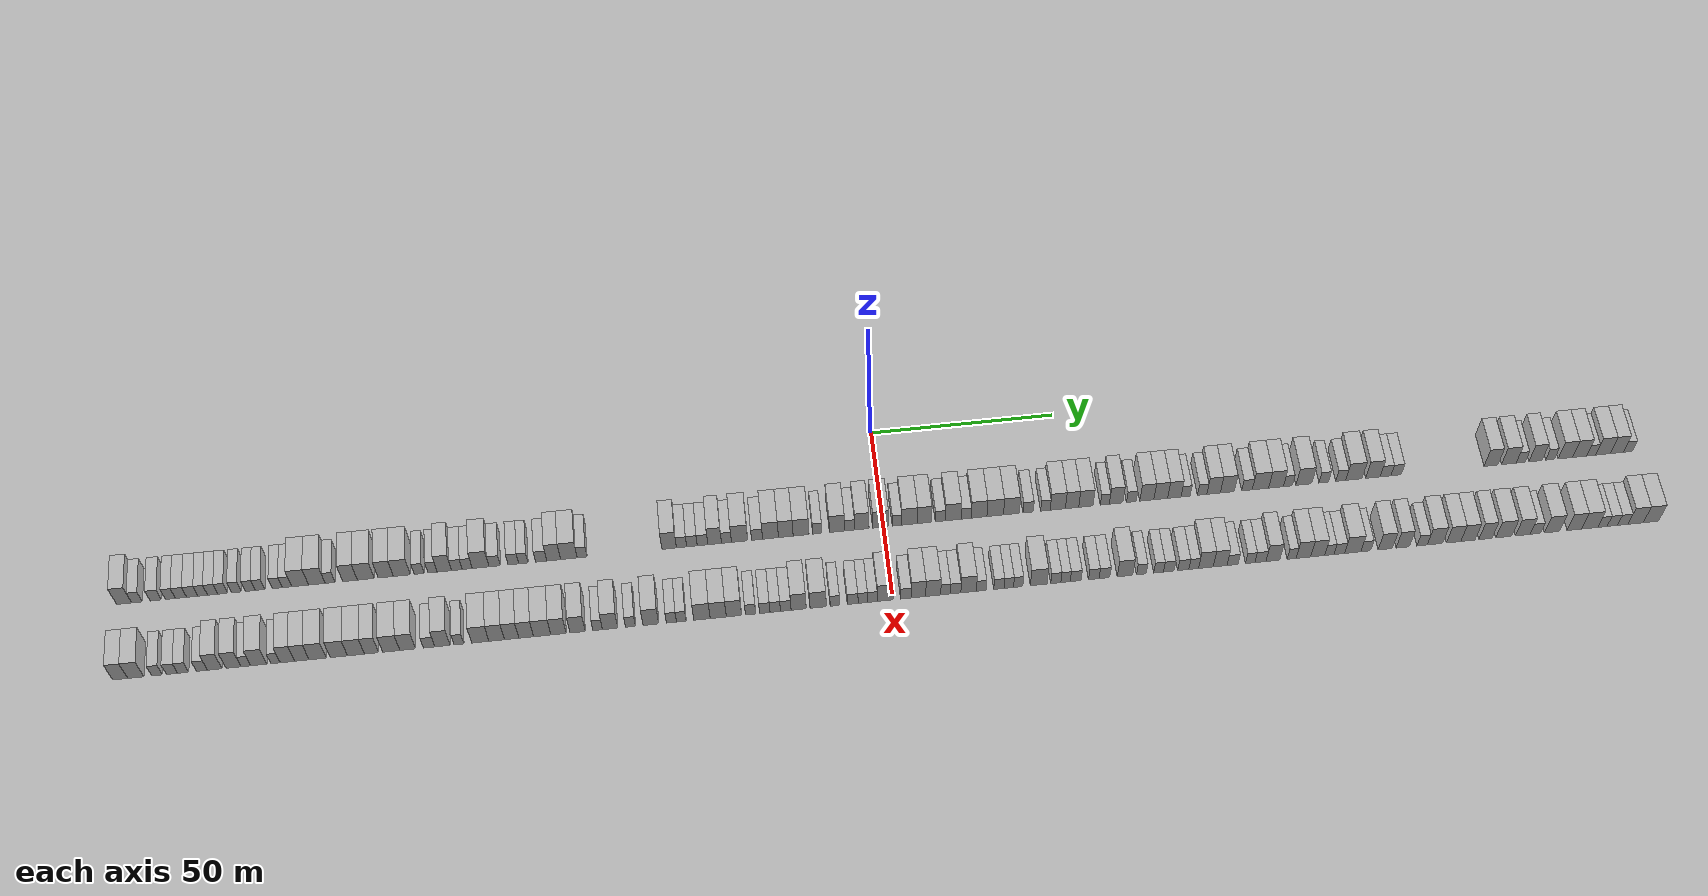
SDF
<?xml version="1.0" encoding="utf-8"?>

<sdf version="1.6">

   <world name="default">

      <gui fullscreen="0">

         <camera name="user_camera">

            <pose>-15 0 4.57585 0 0 0</pose>

            <view_controller>orbit</view_controller>

         </camera>

      </gui>

      <scene>

         <sky>

           <clouds>

             <speed>12</speed>

           </clouds>

         </sky>

         <ambient>0.4 0.4 0.4 1</ambient>

         <background>0.7 0.7 0.7 1</background>

         <shadows>1</shadows>

      </scene>

      <gravity>0 0 -9.8066</gravity>

      <magnetic_field>6e-06 2.3e-05 -4.2e-05</magnetic_field>

      <physics default="0" name="default_physics" type="ode">

         <ode>

            <solver>

               <type>quick</type>

               <iters>10</iters>

               <sor>1.0</sor>

               <use_dynamic_moi_rescaling>0</use_dynamic_moi_rescaling>

            </solver>

            <constraints>

               <cfm>0</cfm>

               <erp>0.2</erp>

               <contact_max_correcting_vel>100</contact_max_correcting_vel>

               <contact_surface_layer>0.001</contact_surface_layer>

            </constraints>

         </ode>

         <max_step_size>0.004</max_step_size>

         <real_time_factor>1</real_time_factor>

         <real_time_update_rate>250</real_time_update_rate>

      </physics>

      <light name="sun" type="directional">

         <cast_shadows>1</cast_shadows>

         <pose>0 0 10 0 0 0</pose>

         <diffuse>0.8 0.8 0.8 1</diffuse>

         <specular>0.2 0.2 0.2 1</specular>

         <attenuation>

            <range>1000</range>

            <constant>0.9</constant>

            <linear>0.01</linear>

            <quadratic>0.001</quadratic>

         </attenuation>

         <direction>-0.5 0.1 -0.9</direction>

      </light>

      <include>

         <name>ground_plane_1</name>

         <uri>model://HANNAS_ground_plane</uri>

         <pose>0 0 0  0 0 0</pose>

      </include>

      <include>

         <name>ground_plane_2</name>

         <uri>model://HANNAS_ground_plane</uri>

         <pose>100 0 0  0 0 0</pose>

      </include>

      <model name="building_1">

         <static>1</static>

         <pose frame="">25.0000 -200.0431 0 0.000000 0.000000 0.000000</pose>

         <link name="link">

            <pose frame="">0 0 4.50 0 0 0</pose>

            <collision name="collision">

               <geometry>

                  <box>

                     <size>10.0000 3.9137 9.0000</size>

                  </box>

               </geometry>

               <max_contacts>10</max_contacts>

               <surface>

                  <contact>

                     <ode/>

                  </contact>

                  <bounce/>

                  <friction>

                     <torsional>

                        <ode/>

                     </torsional>

                     <ode/>

                  </friction>

               </surface>

            </collision>

            <visual name="visual">

               <cast_shadows>0</cast_shadows>

               <geometry>

                  <box>

                     <size>10.0000 3.9137 9.0000</size>

                  </box>

               </geometry>

               <material>

                  <script>

                     <uri>model://HANNAS_wall/materials/scripts</uri>

                     <uri>model://HANNAS_wall/materials/textures</uri>

                     <name>vrc/HANNAS_wall</name>

                  </script>

               </material>

            </visual>

            <self_collide>0</self_collide>

            <enable_wind>0</enable_wind>

            <kinematic>0</kinematic>

         </link>

      </model>

      <model name="building_2">

         <static>1</static>

         <pose frame="">25.0000 -196.7073 0 0.000000 0.000000 0.000000</pose>

         <link name="link">

            <pose frame="">0 0 3.00 0 0 0</pose>

            <collision name="collision">

               <geometry>

                  <box>

                     <size>10.0000 2.7580 6.0000</size>

                  </box>

               </geometry>

               <max_contacts>10</max_contacts>

               <surface>

                  <contact>

                     <ode/>

                  </contact>

                  <bounce/>

                  <friction>

                     <torsional>

                        <ode/>

                     </torsional>

                     <ode/>

                  </friction>

               </surface>

            </collision>

            <visual name="visual">

               <cast_shadows>0</cast_shadows>

               <geometry>

                  <box>

                     <size>10.0000 2.7580 6.0000</size>

                  </box>

               </geometry>

               <material>

                  <script>

                     <uri>model://HANNAS_wall/materials/scripts</uri>

                     <uri>model://HANNAS_wall/materials/textures</uri>

                     <name>vrc/HANNAS_wall</name>

                  </script>

               </material>

            </visual>

            <self_collide>0</self_collide>

            <enable_wind>0</enable_wind>

            <kinematic>0</kinematic>

         </link>

      </model>

      <model name="building_3">

         <static>1</static>

         <pose frame="">25.0000 -191.8505 0 0.000000 0.000000 0.000000</pose>

         <link name="link">

            <pose frame="">0 0 3.00 0 0 0</pose>

            <collision name="collision">

               <geometry>

                  <box>

                     <size>10.0000 2.9555 6.0000</size>

                  </box>

               </geometry>

               <max_contacts>10</max_contacts>

               <surface>

                  <contact>

                     <ode/>

                  </contact>

                  <bounce/>

                  <friction>

                     <torsional>

                        <ode/>

                     </torsional>

                     <ode/>

                  </friction>

               </surface>

            </collision>

            <visual name="visual">

               <cast_shadows>0</cast_shadows>

               <geometry>

                  <box>

                     <size>10.0000 2.9555 6.0000</size>

                  </box>

               </geometry>

               <material>

                  <script>

                     <uri>model://HANNAS_wall/materials/scripts</uri>

                     <uri>model://HANNAS_wall/materials/textures</uri>

                     <name>vrc/HANNAS_wall</name>

                  </script>

               </material>

            </visual>

            <self_collide>0</self_collide>

            <enable_wind>0</enable_wind>

            <kinematic>0</kinematic>

         </link>

      </model>

      <model name="building_4">

         <static>1</static>

         <pose frame="">25.0000 -188.0546 0 0.000000 0.000000 0.000000</pose>

         <link name="link">

            <pose frame="">0 0 3.00 0 0 0</pose>

            <collision name="collision">

               <geometry>

                  <box>

                     <size>10.0000 2.6365 6.0000</size>

                  </box>

               </geometry>

               <max_contacts>10</max_contacts>

               <surface>

                  <contact>

                     <ode/>

                  </contact>

                  <bounce/>

                  <friction>

                     <torsional>

                        <ode/>

                     </torsional>

                     <ode/>

                  </friction>

               </surface>

            </collision>

            <visual name="visual">

               <cast_shadows>0</cast_shadows>

               <geometry>

                  <box>

                     <size>10.0000 2.6365 6.0000</size>

                  </box>

               </geometry>

               <material>

                  <script>

                     <uri>model://HANNAS_wall/materials/scripts</uri>

                     <uri>model://HANNAS_wall/materials/textures</uri>

                     <name>vrc/HANNAS_wall</name>

                  </script>

               </material>

            </visual>

            <self_collide>0</self_collide>

            <enable_wind>0</enable_wind>

            <kinematic>0</kinematic>

         </link>

      </model>

      <model name="building_5">

         <static>1</static>

         <pose frame="">25.0000 -185.2900 0 0.000000 0.000000 0.000000</pose>

         <link name="link">

            <pose frame="">0 0 3.00 0 0 0</pose>

            <collision name="collision">

               <geometry>

                  <box>

                     <size>10.0000 2.8927 6.0000</size>

                  </box>

               </geometry>

               <max_contacts>10</max_contacts>

               <surface>

                  <contact>

                     <ode/>

                  </contact>

                  <bounce/>

                  <friction>

                     <torsional>

                        <ode/>

                     </torsional>

                     <ode/>

                  </friction>

               </surface>

            </collision>

            <visual name="visual">

               <cast_shadows>0</cast_shadows>

               <geometry>

                  <box>

                     <size>10.0000 2.8927 6.0000</size>

                  </box>

               </geometry>

               <material>

                  <script>

                     <uri>model://HANNAS_wall/materials/scripts</uri>

                     <uri>model://HANNAS_wall/materials/textures</uri>

                     <name>vrc/HANNAS_wall</name>

                  </script>

               </material>

            </visual>

            <self_collide>0</self_collide>

            <enable_wind>0</enable_wind>

            <kinematic>0</kinematic>

         </link>

      </model>

      <model name="building_6">

         <static>1</static>

         <pose frame="">25.0000 -182.3802 0 0.000000 0.000000 0.000000</pose>

         <link name="link">

            <pose frame="">0 0 3.00 0 0 0</pose>

            <collision name="collision">

               <geometry>

                  <box>

                     <size>10.0000 2.9268 6.0000</size>

                  </box>

               </geometry>

               <max_contacts>10</max_contacts>

               <surface>

                  <contact>

                     <ode/>

                  </contact>

                  <bounce/>

                  <friction>

                     <torsional>

                        <ode/>

                     </torsional>

                     <ode/>

                  </friction>

               </surface>

            </collision>

            <visual name="visual">

               <cast_shadows>0</cast_shadows>

               <geometry>

                  <box>

                     <size>10.0000 2.9268 6.0000</size>

                  </box>

               </geometry>

               <material>

                  <script>

                     <uri>model://HANNAS_wall/materials/scripts</uri>

                     <uri>model://HANNAS_wall/materials/textures</uri>

                     <name>vrc/HANNAS_wall</name>

                  </script>

               </material>

            </visual>

            <self_collide>0</self_collide>

            <enable_wind>0</enable_wind>

            <kinematic>0</kinematic>

         </link>

      </model>

      <model name="building_7">

         <static>1</static>

         <pose frame="">25.0000 -179.6508 0 0.000000 0.000000 0.000000</pose>

         <link name="link">

            <pose frame="">0 0 3.00 0 0 0</pose>

            <collision name="collision">

               <geometry>

                  <box>

                     <size>10.0000 2.5320 6.0000</size>

                  </box>

               </geometry>

               <max_contacts>10</max_contacts>

               <surface>

                  <contact>

                     <ode/>

                  </contact>

                  <bounce/>

                  <friction>

                     <torsional>

                        <ode/>

                     </torsional>

                     <ode/>

                  </friction>

               </surface>

            </collision>

            <visual name="visual">

               <cast_shadows>0</cast_shadows>

               <geometry>

                  <box>

                     <size>10.0000 2.5320 6.0000</size>

                  </box>

               </geometry>

               <material>

                  <script>

                     <uri>model://HANNAS_wall/materials/scripts</uri>

                     <uri>model://HANNAS_wall/materials/textures</uri>

                     <name>vrc/HANNAS_wall</name>

                  </script>

               </material>

            </visual>

            <self_collide>0</self_collide>

            <enable_wind>0</enable_wind>

            <kinematic>0</kinematic>

         </link>

      </model>

      <model name="building_8">

         <static>1</static>

         <pose frame="">25.0000 -177.0673 0 0.000000 0.000000 0.000000</pose>

         <link name="link">

            <pose frame="">0 0 3.00 0 0 0</pose>

            <collision name="collision">

               <geometry>

                  <box>

                     <size>10.0000 2.6349 6.0000</size>

                  </box>

               </geometry>

               <max_contacts>10</max_contacts>

               <surface>

                  <contact>

                     <ode/>

                  </contact>

                  <bounce/>

                  <friction>

                     <torsional>

                        <ode/>

                     </torsional>

                     <ode/>

                  </friction>

               </surface>

            </collision>

            <visual name="visual">

               <cast_shadows>0</cast_shadows>

               <geometry>

                  <box>

                     <size>10.0000 2.6349 6.0000</size>

                  </box>

               </geometry>

               <material>

                  <script>

                     <uri>model://HANNAS_wall/materials/scripts</uri>

                     <uri>model://HANNAS_wall/materials/textures</uri>

                     <name>vrc/HANNAS_wall</name>

                  </script>

               </material>

            </visual>

            <self_collide>0</self_collide>

            <enable_wind>0</enable_wind>

            <kinematic>0</kinematic>

         </link>

      </model>

      <model name="building_9">

         <static>1</static>

         <pose frame="">25.0000 -174.4618 0 0.000000 0.000000 0.000000</pose>

         <link name="link">

            <pose frame="">0 0 3.00 0 0 0</pose>

            <collision name="collision">

               <geometry>

                  <box>

                     <size>10.0000 2.5761 6.0000</size>

                  </box>

               </geometry>

               <max_contacts>10</max_contacts>

               <surface>

                  <contact>

                     <ode/>

                  </contact>

                  <bounce/>

                  <friction>

                     <torsional>

                        <ode/>

                     </torsional>

                     <ode/>

                  </friction>

               </surface>

            </collision>

            <visual name="visual">

               <cast_shadows>0</cast_shadows>

               <geometry>

                  <box>

                     <size>10.0000 2.5761 6.0000</size>

                  </box>

               </geometry>

               <material>

                  <script>

                     <uri>model://HANNAS_wall/materials/scripts</uri>

                     <uri>model://HANNAS_wall/materials/textures</uri>

                     <name>vrc/HANNAS_wall</name>

                  </script>

               </material>

            </visual>

            <self_collide>0</self_collide>

            <enable_wind>0</enable_wind>

            <kinematic>0</kinematic>

         </link>

      </model>

      <model name="building_10">

         <static>1</static>

         <pose frame="">25.0000 -170.8962 0 0.000000 0.000000 0.000000</pose>

         <link name="link">

            <pose frame="">0 0 3.00 0 0 0</pose>

            <collision name="collision">

               <geometry>

                  <box>

                     <size>10.0000 2.5550 6.0000</size>

                  </box>

               </geometry>

               <max_contacts>10</max_contacts>

               <surface>

                  <contact>

                     <ode/>

                  </contact>

                  <bounce/>

                  <friction>

                     <torsional>

                        <ode/>

                     </torsional>

                     <ode/>

                  </friction>

               </surface>

            </collision>

            <visual name="visual">

               <cast_shadows>0</cast_shadows>

               <geometry>

                  <box>

                     <size>10.0000 2.5550 6.0000</size>

                  </box>

               </geometry>

               <material>

                  <script>

                     <uri>model://HANNAS_wall/materials/scripts</uri>

                     <uri>model://HANNAS_wall/materials/textures</uri>

                     <name>vrc/HANNAS_wall</name>

                  </script>

               </material>

            </visual>

            <self_collide>0</self_collide>

            <enable_wind>0</enable_wind>

            <kinematic>0</kinematic>

         </link>

      </model>

      <model name="building_11">

         <static>1</static>

         <pose frame="">25.0000 -167.3284 0 0.000000 0.000000 0.000000</pose>

         <link name="link">

            <pose frame="">0 0 3.00 0 0 0</pose>

            <collision name="collision">

               <geometry>

                  <box>

                     <size>10.0000 2.5806 6.0000</size>

                  </box>

               </geometry>

               <max_contacts>10</max_contacts>

               <surface>

                  <contact>

                     <ode/>

                  </contact>

                  <bounce/>

                  <friction>

                     <torsional>

                        <ode/>

                     </torsional>

                     <ode/>

                  </friction>

               </surface>

            </collision>

            <visual name="visual">

               <cast_shadows>0</cast_shadows>

               <geometry>

                  <box>

                     <size>10.0000 2.5806 6.0000</size>

                  </box>

               </geometry>

               <material>

                  <script>

                     <uri>model://HANNAS_wall/materials/scripts</uri>

                     <uri>model://HANNAS_wall/materials/textures</uri>

                     <name>vrc/HANNAS_wall</name>

                  </script>

               </material>

            </visual>

            <self_collide>0</self_collide>

            <enable_wind>0</enable_wind>

            <kinematic>0</kinematic>

         </link>

      </model>

      <model name="building_12">

         <static>1</static>

         <pose frame="">25.0000 -164.7689 0 0.000000 0.000000 0.000000</pose>

         <link name="link">

            <pose frame="">0 0 3.00 0 0 0</pose>

            <collision name="collision">

               <geometry>

                  <box>

                     <size>10.0000 2.5385 6.0000</size>

                  </box>

               </geometry>

               <max_contacts>10</max_contacts>

               <surface>

                  <contact>

                     <ode/>

                  </contact>

                  <bounce/>

                  <friction>

                     <torsional>

                        <ode/>

                     </torsional>

                     <ode/>

                  </friction>

               </surface>

            </collision>

            <visual name="visual">

               <cast_shadows>0</cast_shadows>

               <geometry>

                  <box>

                     <size>10.0000 2.5385 6.0000</size>

                  </box>

               </geometry>

               <material>

                  <script>

                     <uri>model://HANNAS_wall/materials/scripts</uri>

                     <uri>model://HANNAS_wall/materials/textures</uri>

                     <name>vrc/HANNAS_wall</name>

                  </script>

               </material>

            </visual>

            <self_collide>0</self_collide>

            <enable_wind>0</enable_wind>

            <kinematic>0</kinematic>

         </link>

      </model>

      <model name="building_13">

         <static>1</static>

         <pose frame="">25.0000 -160.2340 0 0.000000 0.000000 0.000000</pose>

         <link name="link">

            <pose frame="">0 0 3.00 0 0 0</pose>

            <collision name="collision">

               <geometry>

                  <box>

                     <size>10.0000 2.5311 6.0000</size>

                  </box>

               </geometry>

               <max_contacts>10</max_contacts>

               <surface>

                  <contact>

                     <ode/>

                  </contact>

                  <bounce/>

                  <friction>

                     <torsional>

                        <ode/>

                     </torsional>

                     <ode/>

                  </friction>

               </surface>

            </collision>

            <visual name="visual">

               <cast_shadows>0</cast_shadows>

               <geometry>

                  <box>

                     <size>10.0000 2.5311 6.0000</size>

                  </box>

               </geometry>

               <material>

                  <script>

                     <uri>model://HANNAS_wall/materials/scripts</uri>

                     <uri>model://HANNAS_wall/materials/textures</uri>

                     <name>vrc/HANNAS_wall</name>

                  </script>

               </material>

            </visual>

            <self_collide>0</self_collide>

            <enable_wind>0</enable_wind>

            <kinematic>0</kinematic>

         </link>

      </model>

      <model name="building_14">

         <static>1</static>

         <pose frame="">25.0000 -157.7201 0 0.000000 0.000000 0.000000</pose>

         <link name="link">

            <pose frame="">0 0 3.00 0 0 0</pose>

            <collision name="collision">

               <geometry>

                  <box>

                     <size>10.0000 2.4967 6.0000</size>

                  </box>

               </geometry>

               <max_contacts>10</max_contacts>

               <surface>

                  <contact>

                     <ode/>

                  </contact>

                  <bounce/>

                  <friction>

                     <torsional>

                        <ode/>

                     </torsional>

                     <ode/>

                  </friction>

               </surface>

            </collision>

            <visual name="visual">

               <cast_shadows>0</cast_shadows>

               <geometry>

                  <box>

                     <size>10.0000 2.4967 6.0000</size>

                  </box>

               </geometry>

               <material>

                  <script>

                     <uri>model://HANNAS_wall/materials/scripts</uri>

                     <uri>model://HANNAS_wall/materials/textures</uri>

                     <name>vrc/HANNAS_wall</name>

                  </script>

               </material>

            </visual>

            <self_collide>0</self_collide>

            <enable_wind>0</enable_wind>

            <kinematic>0</kinematic>

         </link>

      </model>

      <model name="building_15">

         <static>1</static>

         <pose frame="">25.0000 -154.2740 0 0.000000 0.000000 0.000000</pose>

         <link name="link">

            <pose frame="">0 0 4.50 0 0 0</pose>

            <collision name="collision">

               <geometry>

                  <box>

                     <size>10.0000 4.3956 9.0000</size>

                  </box>

               </geometry>

               <max_contacts>10</max_contacts>

               <surface>

                  <contact>

                     <ode/>

                  </contact>

                  <bounce/>

                  <friction>

                     <torsional>

                        <ode/>

                     </torsional>

                     <ode/>

                  </friction>

               </surface>

            </collision>

            <visual name="visual">

               <cast_shadows>0</cast_shadows>

               <geometry>

                  <box>

                     <size>10.0000 4.3956 9.0000</size>

                  </box>

               </geometry>

               <material>

                  <script>

                     <uri>model://HANNAS_wall/materials/scripts</uri>

                     <uri>model://HANNAS_wall/materials/textures</uri>

                     <name>vrc/HANNAS_wall</name>

                  </script>

               </material>

            </visual>

            <self_collide>0</self_collide>

            <enable_wind>0</enable_wind>

            <kinematic>0</kinematic>

         </link>

      </model>

      <model name="building_16">

         <static>1</static>

         <pose frame="">25.0000 -149.9144 0 0.000000 0.000000 0.000000</pose>

         <link name="link">

            <pose frame="">0 0 4.50 0 0 0</pose>

            <collision name="collision">

               <geometry>

                  <box>

                     <size>10.0000 4.3236 9.0000</size>

                  </box>

               </geometry>

               <max_contacts>10</max_contacts>

               <surface>

                  <contact>

                     <ode/>

                  </contact>

                  <bounce/>

                  <friction>

                     <torsional>

                        <ode/>

                     </torsional>

                     <ode/>

                  </friction>

               </surface>

            </collision>

            <visual name="visual">

               <cast_shadows>0</cast_shadows>

               <geometry>

                  <box>

                     <size>10.0000 4.3236 9.0000</size>

                  </box>

               </geometry>

               <material>

                  <script>

                     <uri>model://HANNAS_wall/materials/scripts</uri>

                     <uri>model://HANNAS_wall/materials/textures</uri>

                     <name>vrc/HANNAS_wall</name>

                  </script>

               </material>

            </visual>

            <self_collide>0</self_collide>

            <enable_wind>0</enable_wind>

            <kinematic>0</kinematic>

         </link>

      </model>

      <model name="building_17">

         <static>1</static>

         <pose frame="">25.0000 -146.4588 0 0.000000 0.000000 0.000000</pose>

         <link name="link">

            <pose frame="">0 0 3.00 0 0 0</pose>

            <collision name="collision">

               <geometry>

                  <box>

                     <size>10.0000 2.5877 6.0000</size>

                  </box>

               </geometry>

               <max_contacts>10</max_contacts>

               <surface>

                  <contact>

                     <ode/>

                  </contact>

                  <bounce/>

                  <friction>

                     <torsional>

                        <ode/>

                     </torsional>

                     <ode/>

                  </friction>

               </surface>

            </collision>

            <visual name="visual">

               <cast_shadows>0</cast_shadows>

               <geometry>

                  <box>

                     <size>10.0000 2.5877 6.0000</size>

                  </box>

               </geometry>

               <material>

                  <script>

                     <uri>model://HANNAS_wall/materials/scripts</uri>

                     <uri>model://HANNAS_wall/materials/textures</uri>

                     <name>vrc/HANNAS_wall</name>

                  </script>

               </material>

            </visual>

            <self_collide>0</self_collide>

            <enable_wind>0</enable_wind>

            <kinematic>0</kinematic>

         </link>

      </model>

      <model name="building_18">

         <static>1</static>

         <pose frame="">25.0000 -141.2487 0 0.000000 0.000000 0.000000</pose>

         <link name="link">

            <pose frame="">0 0 4.50 0 0 0</pose>

            <collision name="collision">

               <geometry>

                  <box>

                     <size>10.0000 3.8325 9.0000</size>

                  </box>

               </geometry>

               <max_contacts>10</max_contacts>

               <surface>

                  <contact>

                     <ode/>

                  </contact>

                  <bounce/>

                  <friction>

                     <torsional>

                        <ode/>

                     </torsional>

                     <ode/>

                  </friction>

               </surface>

            </collision>

            <visual name="visual">

               <cast_shadows>0</cast_shadows>

               <geometry>

                  <box>

                     <size>10.0000 3.8325 9.0000</size>

                  </box>

               </geometry>

               <material>

                  <script>

                     <uri>model://HANNAS_wall/materials/scripts</uri>

                     <uri>model://HANNAS_wall/materials/textures</uri>

                     <name>vrc/HANNAS_wall</name>

                  </script>

               </material>

            </visual>

            <self_collide>0</self_collide>

            <enable_wind>0</enable_wind>

            <kinematic>0</kinematic>

         </link>

      </model>

      <model name="building_19">

         <static>1</static>

         <pose frame="">25.0000 -137.1106 0 0.000000 0.000000 0.000000</pose>

         <link name="link">

            <pose frame="">0 0 4.50 0 0 0</pose>

            <collision name="collision">

               <geometry>

                  <box>

                     <size>10.0000 4.4438 9.0000</size>

                  </box>

               </geometry>

               <max_contacts>10</max_contacts>

               <surface>

                  <contact>

                     <ode/>

                  </contact>

                  <bounce/>

                  <friction>

                     <torsional>

                        <ode/>

                     </torsional>

                     <ode/>

                  </friction>

               </surface>

            </collision>

            <visual name="visual">

               <cast_shadows>0</cast_shadows>

               <geometry>

                  <box>

                     <size>10.0000 4.4438 9.0000</size>

                  </box>

               </geometry>

               <material>

                  <script>

                     <uri>model://HANNAS_wall/materials/scripts</uri>

                     <uri>model://HANNAS_wall/materials/textures</uri>

                     <name>vrc/HANNAS_wall</name>

                  </script>

               </material>

            </visual>

            <self_collide>0</self_collide>

            <enable_wind>0</enable_wind>

            <kinematic>0</kinematic>

         </link>

      </model>

      <model name="building_20">

         <static>1</static>

         <pose frame="">25.0000 -131.8946 0 0.000000 0.000000 0.000000</pose>

         <link name="link">

            <pose frame="">0 0 4.50 0 0 0</pose>

            <collision name="collision">

               <geometry>

                  <box>

                     <size>10.0000 3.9882 9.0000</size>

                  </box>

               </geometry>

               <max_contacts>10</max_contacts>

               <surface>

                  <contact>

                     <ode/>

                  </contact>

                  <bounce/>

                  <friction>

                     <torsional>

                        <ode/>

                     </torsional>

                     <ode/>

                  </friction>

               </surface>

            </collision>

            <visual name="visual">

               <cast_shadows>0</cast_shadows>

               <geometry>

                  <box>

                     <size>10.0000 3.9882 9.0000</size>

                  </box>

               </geometry>

               <material>

                  <script>

                     <uri>model://HANNAS_wall/materials/scripts</uri>

                     <uri>model://HANNAS_wall/materials/textures</uri>

                     <name>vrc/HANNAS_wall</name>

                  </script>

               </material>

            </visual>

            <self_collide>0</self_collide>

            <enable_wind>0</enable_wind>

            <kinematic>0</kinematic>

         </link>

      </model>

      <model name="building_21">

         <static>1</static>

         <pose frame="">25.0000 -127.6713 0 0.000000 0.000000 0.000000</pose>

         <link name="link">

            <pose frame="">0 0 4.50 0 0 0</pose>

            <collision name="collision">

               <geometry>

                  <box>

                     <size>10.0000 4.4585 9.0000</size>

                  </box>

               </geometry>

               <max_contacts>10</max_contacts>

               <surface>

                  <contact>

                     <ode/>

                  </contact>

                  <bounce/>

                  <friction>

                     <torsional>

                        <ode/>

                     </torsional>

                     <ode/>

                  </friction>

               </surface>

            </collision>

            <visual name="visual">

               <cast_shadows>0</cast_shadows>

               <geometry>

                  <box>

                     <size>10.0000 4.4585 9.0000</size>

                  </box>

               </geometry>

               <material>

                  <script>

                     <uri>model://HANNAS_wall/materials/scripts</uri>

                     <uri>model://HANNAS_wall/materials/textures</uri>

                     <name>vrc/HANNAS_wall</name>

                  </script>

               </material>

            </visual>

            <self_collide>0</self_collide>

            <enable_wind>0</enable_wind>

            <kinematic>0</kinematic>

         </link>

      </model>

      <model name="building_22">

         <static>1</static>

         <pose frame="">25.0000 -123.1345 0 0.000000 0.000000 0.000000</pose>

         <link name="link">

            <pose frame="">0 0 3.00 0 0 0</pose>

            <collision name="collision">

               <geometry>

                  <box>

                     <size>10.0000 2.6150 6.0000</size>

                  </box>

               </geometry>

               <max_contacts>10</max_contacts>

               <surface>

                  <contact>

                     <ode/>

                  </contact>

                  <bounce/>

                  <friction>

                     <torsional>

                        <ode/>

                     </torsional>

                     <ode/>

                  </friction>

               </surface>

            </collision>

            <visual name="visual">

               <cast_shadows>0</cast_shadows>

               <geometry>

                  <box>

                     <size>10.0000 2.6150 6.0000</size>

                  </box>

               </geometry>

               <material>

                  <script>

                     <uri>model://HANNAS_wall/materials/scripts</uri>

                     <uri>model://HANNAS_wall/materials/textures</uri>

                     <name>vrc/HANNAS_wall</name>

                  </script>

               </material>

            </visual>

            <self_collide>0</self_collide>

            <enable_wind>0</enable_wind>

            <kinematic>0</kinematic>

         </link>

      </model>

      <model name="building_23">

         <static>1</static>

         <pose frame="">25.0000 -119.6156 0 0.000000 0.000000 0.000000</pose>

         <link name="link">

            <pose frame="">0 0 3.00 0 0 0</pose>

            <collision name="collision">

               <geometry>

                  <box>

                     <size>10.0000 2.4228 6.0000</size>

                  </box>

               </geometry>

               <max_contacts>10</max_contacts>

               <surface>

                  <contact>

                     <ode/>

                  </contact>

                  <bounce/>

                  <friction>

                     <torsional>

                        <ode/>

                     </torsional>

                     <ode/>

                  </friction>

               </surface>

            </collision>

            <visual name="visual">

               <cast_shadows>0</cast_shadows>

               <geometry>

                  <box>

                     <size>10.0000 2.4228 6.0000</size>

                  </box>

               </geometry>

               <material>

                  <script>

                     <uri>model://HANNAS_wall/materials/scripts</uri>

                     <uri>model://HANNAS_wall/materials/textures</uri>

                     <name>vrc/HANNAS_wall</name>

                  </script>

               </material>

            </visual>

            <self_collide>0</self_collide>

            <enable_wind>0</enable_wind>

            <kinematic>0</kinematic>

         </link>

      </model>

      <model name="building_24">

         <static>1</static>

         <pose frame="">25.0000 -116.5192 0 0.000000 0.000000 0.000000</pose>

         <link name="link">

            <pose frame="">0 0 4.50 0 0 0</pose>

            <collision name="collision">

               <geometry>

                  <box>

                     <size>10.0000 3.7701 9.0000</size>

                  </box>

               </geometry>

               <max_contacts>10</max_contacts>

               <surface>

                  <contact>

                     <ode/>

                  </contact>

                  <bounce/>

                  <friction>

                     <torsional>

                        <ode/>

                     </torsional>

                     <ode/>

                  </friction>

               </surface>

            </collision>

            <visual name="visual">

               <cast_shadows>0</cast_shadows>

               <geometry>

                  <box>

                     <size>10.0000 3.7701 9.0000</size>

                  </box>

               </geometry>

               <material>

                  <script>

                     <uri>model://HANNAS_wall/materials/scripts</uri>

                     <uri>model://HANNAS_wall/materials/textures</uri>

                     <name>vrc/HANNAS_wall</name>

                  </script>

               </material>

            </visual>

            <self_collide>0</self_collide>

            <enable_wind>0</enable_wind>

            <kinematic>0</kinematic>

         </link>

      </model>

      <model name="building_25">

         <static>1</static>

         <pose frame="">25.0000 -113.2266 0 0.000000 0.000000 0.000000</pose>

         <link name="link">

            <pose frame="">0 0 3.00 0 0 0</pose>

            <collision name="collision">

               <geometry>

                  <box>

                     <size>10.0000 2.8150 6.0000</size>

                  </box>

               </geometry>

               <max_contacts>10</max_contacts>

               <surface>

                  <contact>

                     <ode/>

                  </contact>

                  <bounce/>

                  <friction>

                     <torsional>

                        <ode/>

                     </torsional>

                     <ode/>

                  </friction>

               </surface>

            </collision>

            <visual name="visual">

               <cast_shadows>0</cast_shadows>

               <geometry>

                  <box>

                     <size>10.0000 2.8150 6.0000</size>

                  </box>

               </geometry>

               <material>

                  <script>

                     <uri>model://HANNAS_wall/materials/scripts</uri>

                     <uri>model://HANNAS_wall/materials/textures</uri>

                     <name>vrc/HANNAS_wall</name>

                  </script>

               </material>

            </visual>

            <self_collide>0</self_collide>

            <enable_wind>0</enable_wind>

            <kinematic>0</kinematic>

         </link>

      </model>

      <model name="building_26">

         <static>1</static>

         <pose frame="">25.0000 -110.4952 0 0.000000 0.000000 0.000000</pose>

         <link name="link">

            <pose frame="">0 0 3.00 0 0 0</pose>

            <collision name="collision">

               <geometry>

                  <box>

                     <size>10.0000 2.6478 6.0000</size>

                  </box>

               </geometry>

               <max_contacts>10</max_contacts>

               <surface>

                  <contact>

                     <ode/>

                  </contact>

                  <bounce/>

                  <friction>

                     <torsional>

                        <ode/>

                     </torsional>

                     <ode/>

                  </friction>

               </surface>

            </collision>

            <visual name="visual">

               <cast_shadows>0</cast_shadows>

               <geometry>

                  <box>

                     <size>10.0000 2.6478 6.0000</size>

                  </box>

               </geometry>

               <material>

                  <script>

                     <uri>model://HANNAS_wall/materials/scripts</uri>

                     <uri>model://HANNAS_wall/materials/textures</uri>

                     <name>vrc/HANNAS_wall</name>

                  </script>

               </material>

            </visual>

            <self_collide>0</self_collide>

            <enable_wind>0</enable_wind>

            <kinematic>0</kinematic>

         </link>

      </model>

      <model name="building_27">

         <static>1</static>

         <pose frame="">25.0000 -106.9631 0 0.000000 0.000000 0.000000</pose>

         <link name="link">

            <pose frame="">0 0 4.50 0 0 0</pose>

            <collision name="collision">

               <geometry>

                  <box>

                     <size>10.0000 4.4164 9.0000</size>

                  </box>

               </geometry>

               <max_contacts>10</max_contacts>

               <surface>

                  <contact>

                     <ode/>

                  </contact>

                  <bounce/>

                  <friction>

                     <torsional>

                        <ode/>

                     </torsional>

                     <ode/>

                  </friction>

               </surface>

            </collision>

            <visual name="visual">

               <cast_shadows>0</cast_shadows>

               <geometry>

                  <box>

                     <size>10.0000 4.4164 9.0000</size>

                  </box>

               </geometry>

               <material>

                  <script>

                     <uri>model://HANNAS_wall/materials/scripts</uri>

                     <uri>model://HANNAS_wall/materials/textures</uri>

                     <name>vrc/HANNAS_wall</name>

                  </script>

               </material>

            </visual>

            <self_collide>0</self_collide>

            <enable_wind>0</enable_wind>

            <kinematic>0</kinematic>

         </link>

      </model>

      <model name="building_28">

         <static>1</static>

         <pose frame="">25.0000 -103.2580 0 0.000000 0.000000 0.000000</pose>

         <link name="link">

            <pose frame="">0 0 3.00 0 0 0</pose>

            <collision name="collision">

               <geometry>

                  <box>

                     <size>10.0000 2.9938 6.0000</size>

                  </box>

               </geometry>

               <max_contacts>10</max_contacts>

               <surface>

                  <contact>

                     <ode/>

                  </contact>

                  <bounce/>

                  <friction>

                     <torsional>

                        <ode/>

                     </torsional>

                     <ode/>

                  </friction>

               </surface>

            </collision>

            <visual name="visual">

               <cast_shadows>0</cast_shadows>

               <geometry>

                  <box>

                     <size>10.0000 2.9938 6.0000</size>

                  </box>

               </geometry>

               <material>

                  <script>

                     <uri>model://HANNAS_wall/materials/scripts</uri>

                     <uri>model://HANNAS_wall/materials/textures</uri>

                     <name>vrc/HANNAS_wall</name>

                  </script>

               </material>

            </visual>

            <self_collide>0</self_collide>

            <enable_wind>0</enable_wind>

            <kinematic>0</kinematic>

         </link>

      </model>

      <model name="building_29">

         <static>1</static>

         <pose frame="">25.0000 -98.3528 0 0.000000 0.000000 0.000000</pose>

         <link name="link">

            <pose frame="">0 0 3.00 0 0 0</pose>

            <collision name="collision">

               <geometry>

                  <box>

                     <size>10.0000 2.8166 6.0000</size>

                  </box>

               </geometry>

               <max_contacts>10</max_contacts>

               <surface>

                  <contact>

                     <ode/>

                  </contact>

                  <bounce/>

                  <friction>

                     <torsional>

                        <ode/>

                     </torsional>

                     <ode/>

                  </friction>

               </surface>

            </collision>

            <visual name="visual">

               <cast_shadows>0</cast_shadows>

               <geometry>

                  <box>

                     <size>10.0000 2.8166 6.0000</size>

                  </box>

               </geometry>

               <material>

                  <script>

                     <uri>model://HANNAS_wall/materials/scripts</uri>

                     <uri>model://HANNAS_wall/materials/textures</uri>

                     <name>vrc/HANNAS_wall</name>

                  </script>

               </material>

            </visual>

            <self_collide>0</self_collide>

            <enable_wind>0</enable_wind>

            <kinematic>0</kinematic>

         </link>

      </model>

      <model name="building_30">

         <static>1</static>

         <pose frame="">25.0000 -95.7208 0 0.000000 0.000000 0.000000</pose>

         <link name="link">

            <pose frame="">0 0 3.00 0 0 0</pose>

            <collision name="collision">

               <geometry>

                  <box>

                     <size>10.0000 2.4473 6.0000</size>

                  </box>

               </geometry>

               <max_contacts>10</max_contacts>

               <surface>

                  <contact>

                     <ode/>

                  </contact>

                  <bounce/>

                  <friction>

                     <torsional>

                        <ode/>

                     </torsional>

                     <ode/>

                  </friction>

               </surface>

            </collision>

            <visual name="visual">

               <cast_shadows>0</cast_shadows>

               <geometry>

                  <box>

                     <size>10.0000 2.4473 6.0000</size>

                  </box>

               </geometry>

               <material>

                  <script>

                     <uri>model://HANNAS_wall/materials/scripts</uri>

                     <uri>model://HANNAS_wall/materials/textures</uri>

                     <name>vrc/HANNAS_wall</name>

                  </script>

               </material>

            </visual>

            <self_collide>0</self_collide>

            <enable_wind>0</enable_wind>

            <kinematic>0</kinematic>

         </link>

      </model>

      <model name="building_31">

         <static>1</static>

         <pose frame="">25.0000 -91.0076 0 0.000000 0.000000 0.000000</pose>

         <link name="link">

            <pose frame="">0 0 3.00 0 0 0</pose>

            <collision name="collision">

               <geometry>

                  <box>

                     <size>10.0000 2.9791 6.0000</size>

                  </box>

               </geometry>

               <max_contacts>10</max_contacts>

               <surface>

                  <contact>

                     <ode/>

                  </contact>

                  <bounce/>

                  <friction>

                     <torsional>

                        <ode/>

                     </torsional>

                     <ode/>

                  </friction>

               </surface>

            </collision>

            <visual name="visual">

               <cast_shadows>0</cast_shadows>

               <geometry>

                  <box>

                     <size>10.0000 2.9791 6.0000</size>

                  </box>

               </geometry>

               <material>

                  <script>

                     <uri>model://HANNAS_wall/materials/scripts</uri>

                     <uri>model://HANNAS_wall/materials/textures</uri>

                     <name>vrc/HANNAS_wall</name>

                  </script>

               </material>

            </visual>

            <self_collide>0</self_collide>

            <enable_wind>0</enable_wind>

            <kinematic>0</kinematic>

         </link>

      </model>

      <model name="building_32">

         <static>1</static>

         <pose frame="">25.0000 -87.6984 0 0.000000 0.000000 0.000000</pose>

         <link name="link">

            <pose frame="">0 0 4.50 0 0 0</pose>

            <collision name="collision">

               <geometry>

                  <box>

                     <size>10.0000 3.6393 9.0000</size>

                  </box>

               </geometry>

               <max_contacts>10</max_contacts>

               <surface>

                  <contact>

                     <ode/>

                  </contact>

                  <bounce/>

                  <friction>

                     <torsional>

                        <ode/>

                     </torsional>

                     <ode/>

                  </friction>

               </surface>

            </collision>

            <visual name="visual">

               <cast_shadows>0</cast_shadows>

               <geometry>

                  <box>

                     <size>10.0000 3.6393 9.0000</size>

                  </box>

               </geometry>

               <material>

                  <script>

                     <uri>model://HANNAS_wall/materials/scripts</uri>

                     <uri>model://HANNAS_wall/materials/textures</uri>

                     <name>vrc/HANNAS_wall</name>

                  </script>

               </material>

            </visual>

            <self_collide>0</self_collide>

            <enable_wind>0</enable_wind>

            <kinematic>0</kinematic>

         </link>

      </model>

      <model name="building_33">

         <static>1</static>

         <pose frame="">25.0000 -83.6790 0 0.000000 0.000000 0.000000</pose>

         <link name="link">

            <pose frame="">0 0 4.50 0 0 0</pose>

            <collision name="collision">

               <geometry>

                  <box>

                     <size>10.0000 4.3994 9.0000</size>

                  </box>

               </geometry>

               <max_contacts>10</max_contacts>

               <surface>

                  <contact>

                     <ode/>

                  </contact>

                  <bounce/>

                  <friction>

                     <torsional>

                        <ode/>

                     </torsional>

                     <ode/>

                  </friction>

               </surface>

            </collision>

            <visual name="visual">

               <cast_shadows>0</cast_shadows>

               <geometry>

                  <box>

                     <size>10.0000 4.3994 9.0000</size>

                  </box>

               </geometry>

               <material>

                  <script>

                     <uri>model://HANNAS_wall/materials/scripts</uri>

                     <uri>model://HANNAS_wall/materials/textures</uri>

                     <name>vrc/HANNAS_wall</name>

                  </script>

               </material>

            </visual>

            <self_collide>0</self_collide>

            <enable_wind>0</enable_wind>

            <kinematic>0</kinematic>

         </link>

      </model>

      <model name="building_34">

         <static>1</static>

         <pose frame="">25.0000 -80.1914 0 0.000000 0.000000 0.000000</pose>

         <link name="link">

            <pose frame="">0 0 3.00 0 0 0</pose>

            <collision name="collision">

               <geometry>

                  <box>

                     <size>10.0000 2.5758 6.0000</size>

                  </box>

               </geometry>

               <max_contacts>10</max_contacts>

               <surface>

                  <contact>

                     <ode/>

                  </contact>

                  <bounce/>

                  <friction>

                     <torsional>

                        <ode/>

                     </torsional>

                     <ode/>

                  </friction>

               </surface>

            </collision>

            <visual name="visual">

               <cast_shadows>0</cast_shadows>

               <geometry>

                  <box>

                     <size>10.0000 2.5758 6.0000</size>

                  </box>

               </geometry>

               <material>

                  <script>

                     <uri>model://HANNAS_wall/materials/scripts</uri>

                     <uri>model://HANNAS_wall/materials/textures</uri>

                     <name>vrc/HANNAS_wall</name>

                  </script>

               </material>

            </visual>

            <self_collide>0</self_collide>

            <enable_wind>0</enable_wind>

            <kinematic>0</kinematic>

         </link>

      </model>

      <model name="building_35">

         <static>1</static>

         <pose frame="">25.0000 -57.1080 0 0.000000 0.000000 0.000000</pose>

         <link name="link">

            <pose frame="">0 0 4.50 0 0 0</pose>

            <collision name="collision">

               <geometry>

                  <box>

                     <size>10.0000 3.8637 9.0000</size>

                  </box>

               </geometry>

               <max_contacts>10</max_contacts>

               <surface>

                  <contact>

                     <ode/>

                  </contact>

                  <bounce/>

                  <friction>

                     <torsional>

                        <ode/>

                     </torsional>

                     <ode/>

                  </friction>

               </surface>

            </collision>

            <visual name="visual">

               <cast_shadows>0</cast_shadows>

               <geometry>

                  <box>

                     <size>10.0000 3.8637 9.0000</size>

                  </box>

               </geometry>

               <material>

                  <script>

                     <uri>model://HANNAS_wall/materials/scripts</uri>

                     <uri>model://HANNAS_wall/materials/textures</uri>

                     <name>vrc/HANNAS_wall</name>

                  </script>

               </material>

            </visual>

            <self_collide>0</self_collide>

            <enable_wind>0</enable_wind>

            <kinematic>0</kinematic>

         </link>

      </model>

      <model name="building_36">

         <static>1</static>

         <pose frame="">25.0000 -53.8150 0 0.000000 0.000000 0.000000</pose>

         <link name="link">

            <pose frame="">0 0 3.00 0 0 0</pose>

            <collision name="collision">

               <geometry>

                  <box>

                     <size>10.0000 2.7222 6.0000</size>

                  </box>

               </geometry>

               <max_contacts>10</max_contacts>

               <surface>

                  <contact>

                     <ode/>

                  </contact>

                  <bounce/>

                  <friction>

                     <torsional>

                        <ode/>

                     </torsional>

                     <ode/>

                  </friction>

               </surface>

            </collision>

            <visual name="visual">

               <cast_shadows>0</cast_shadows>

               <geometry>

                  <box>

                     <size>10.0000 2.7222 6.0000</size>

                  </box>

               </geometry>

               <material>

                  <script>

                     <uri>model://HANNAS_wall/materials/scripts</uri>

                     <uri>model://HANNAS_wall/materials/textures</uri>

                     <name>vrc/HANNAS_wall</name>

                  </script>

               </material>

            </visual>

            <self_collide>0</self_collide>

            <enable_wind>0</enable_wind>

            <kinematic>0</kinematic>

         </link>

      </model>

      <model name="building_37">

         <static>1</static>

         <pose frame="">25.0000 -51.0576 0 0.000000 0.000000 0.000000</pose>

         <link name="link">

            <pose frame="">0 0 3.00 0 0 0</pose>

            <collision name="collision">

               <geometry>

                  <box>

                     <size>10.0000 2.7926 6.0000</size>

                  </box>

               </geometry>

               <max_contacts>10</max_contacts>

               <surface>

                  <contact>

                     <ode/>

                  </contact>

                  <bounce/>

                  <friction>

                     <torsional>

                        <ode/>

                     </torsional>

                     <ode/>

                  </friction>

               </surface>

            </collision>

            <visual name="visual">

               <cast_shadows>0</cast_shadows>

               <geometry>

                  <box>

                     <size>10.0000 2.7926 6.0000</size>

                  </box>

               </geometry>

               <material>

                  <script>

                     <uri>model://HANNAS_wall/materials/scripts</uri>

                     <uri>model://HANNAS_wall/materials/textures</uri>

                     <name>vrc/HANNAS_wall</name>

                  </script>

               </material>

            </visual>

            <self_collide>0</self_collide>

            <enable_wind>0</enable_wind>

            <kinematic>0</kinematic>

         </link>

      </model>

      <model name="building_38">

         <static>1</static>

         <pose frame="">25.0000 -48.2400 0 0.000000 0.000000 0.000000</pose>

         <link name="link">

            <pose frame="">0 0 3.00 0 0 0</pose>

            <collision name="collision">

               <geometry>

                  <box>

                     <size>10.0000 2.8425 6.0000</size>

                  </box>

               </geometry>

               <max_contacts>10</max_contacts>

               <surface>

                  <contact>

                     <ode/>

                  </contact>

                  <bounce/>

                  <friction>

                     <torsional>

                        <ode/>

                     </torsional>

                     <ode/>

                  </friction>

               </surface>

            </collision>

            <visual name="visual">

               <cast_shadows>0</cast_shadows>

               <geometry>

                  <box>

                     <size>10.0000 2.8425 6.0000</size>

                  </box>

               </geometry>

               <material>

                  <script>

                     <uri>model://HANNAS_wall/materials/scripts</uri>

                     <uri>model://HANNAS_wall/materials/textures</uri>

                     <name>vrc/HANNAS_wall</name>

                  </script>

               </material>

            </visual>

            <self_collide>0</self_collide>

            <enable_wind>0</enable_wind>

            <kinematic>0</kinematic>

         </link>

      </model>

      <model name="building_39">

         <static>1</static>

         <pose frame="">25.0000 -45.0187 0 0.000000 0.000000 0.000000</pose>

         <link name="link">

            <pose frame="">0 0 4.50 0 0 0</pose>

            <collision name="collision">

               <geometry>

                  <box>

                     <size>10.0000 3.6001 9.0000</size>

                  </box>

               </geometry>

               <max_contacts>10</max_contacts>

               <surface>

                  <contact>

                     <ode/>

                  </contact>

                  <bounce/>

                  <friction>

                     <torsional>

                        <ode/>

                     </torsional>

                     <ode/>

                  </friction>

               </surface>

            </collision>

            <visual name="visual">

               <cast_shadows>0</cast_shadows>

               <geometry>

                  <box>

                     <size>10.0000 3.6001 9.0000</size>

                  </box>

               </geometry>

               <material>

                  <script>

                     <uri>model://HANNAS_wall/materials/scripts</uri>

                     <uri>model://HANNAS_wall/materials/textures</uri>

                     <name>vrc/HANNAS_wall</name>

                  </script>

               </material>

            </visual>

            <self_collide>0</self_collide>

            <enable_wind>0</enable_wind>

            <kinematic>0</kinematic>

         </link>

      </model>

      <model name="building_40">

         <static>1</static>

         <pose frame="">25.0000 -41.8844 0 0.000000 0.000000 0.000000</pose>

         <link name="link">

            <pose frame="">0 0 3.00 0 0 0</pose>

            <collision name="collision">

               <geometry>

                  <box>

                     <size>10.0000 2.6685 6.0000</size>

                  </box>

               </geometry>

               <max_contacts>10</max_contacts>

               <surface>

                  <contact>

                     <ode/>

                  </contact>

                  <bounce/>

                  <friction>

                     <torsional>

                        <ode/>

                     </torsional>

                     <ode/>

                  </friction>

               </surface>

            </collision>

            <visual name="visual">

               <cast_shadows>0</cast_shadows>

               <geometry>

                  <box>

                     <size>10.0000 2.6685 6.0000</size>

                  </box>

               </geometry>

               <material>

                  <script>

                     <uri>model://HANNAS_wall/materials/scripts</uri>

                     <uri>model://HANNAS_wall/materials/textures</uri>

                     <name>vrc/HANNAS_wall</name>

                  </script>

               </material>

            </visual>

            <self_collide>0</self_collide>

            <enable_wind>0</enable_wind>

            <kinematic>0</kinematic>

         </link>

      </model>

      <model name="building_41">

         <static>1</static>

         <pose frame="">25.0000 -38.3859 0 0.000000 0.000000 0.000000</pose>

         <link name="link">

            <pose frame="">0 0 4.50 0 0 0</pose>

            <collision name="collision">

               <geometry>

                  <box>

                     <size>10.0000 4.3285 9.0000</size>

                  </box>

               </geometry>

               <max_contacts>10</max_contacts>

               <surface>

                  <contact>

                     <ode/>

                  </contact>

                  <bounce/>

                  <friction>

                     <torsional>

                        <ode/>

                     </torsional>

                     <ode/>

                  </friction>

               </surface>

            </collision>

            <visual name="visual">

               <cast_shadows>0</cast_shadows>

               <geometry>

                  <box>

                     <size>10.0000 4.3285 9.0000</size>

                  </box>

               </geometry>

               <material>

                  <script>

                     <uri>model://HANNAS_wall/materials/scripts</uri>

                     <uri>model://HANNAS_wall/materials/textures</uri>

                     <name>vrc/HANNAS_wall</name>

                  </script>

               </material>

            </visual>

            <self_collide>0</self_collide>

            <enable_wind>0</enable_wind>

            <kinematic>0</kinematic>

         </link>

      </model>

      <model name="building_42">

         <static>1</static>

         <pose frame="">25.0000 -33.7441 0 0.000000 0.000000 0.000000</pose>

         <link name="link">

            <pose frame="">0 0 3.00 0 0 0</pose>

            <collision name="collision">

               <geometry>

                  <box>

                     <size>10.0000 2.9551 6.0000</size>

                  </box>

               </geometry>

               <max_contacts>10</max_contacts>

               <surface>

                  <contact>

                     <ode/>

                  </contact>

                  <bounce/>

                  <friction>

                     <torsional>

                        <ode/>

                     </torsional>

                     <ode/>

                  </friction>

               </surface>

            </collision>

            <visual name="visual">

               <cast_shadows>0</cast_shadows>

               <geometry>

                  <box>

                     <size>10.0000 2.9551 6.0000</size>

                  </box>

               </geometry>

               <material>

                  <script>

                     <uri>model://HANNAS_wall/materials/scripts</uri>

                     <uri>model://HANNAS_wall/materials/textures</uri>

                     <name>vrc/HANNAS_wall</name>

                  </script>

               </material>

            </visual>

            <self_collide>0</self_collide>

            <enable_wind>0</enable_wind>

            <kinematic>0</kinematic>

         </link>

      </model>

      <model name="building_43">

         <static>1</static>

         <pose frame="">25.0000 -30.1479 0 0.000000 0.000000 0.000000</pose>

         <link name="link">

            <pose frame="">0 0 4.50 0 0 0</pose>

            <collision name="collision">

               <geometry>

                  <box>

                     <size>10.0000 4.2372 9.0000</size>

                  </box>

               </geometry>

               <max_contacts>10</max_contacts>

               <surface>

                  <contact>

                     <ode/>

                  </contact>

                  <bounce/>

                  <friction>

                     <torsional>

                        <ode/>

                     </torsional>

                     <ode/>

                  </friction>

               </surface>

            </collision>

            <visual name="visual">

               <cast_shadows>0</cast_shadows>

               <geometry>

                  <box>

                     <size>10.0000 4.2372 9.0000</size>

                  </box>

               </geometry>

               <material>

                  <script>

                     <uri>model://HANNAS_wall/materials/scripts</uri>

                     <uri>model://HANNAS_wall/materials/textures</uri>

                     <name>vrc/HANNAS_wall</name>

                  </script>

               </material>

            </visual>

            <self_collide>0</self_collide>

            <enable_wind>0</enable_wind>

            <kinematic>0</kinematic>

         </link>

      </model>

      <model name="building_44">

         <static>1</static>

         <pose frame="">25.0000 -26.0718 0 0.000000 0.000000 0.000000</pose>

         <link name="link">

            <pose frame="">0 0 4.50 0 0 0</pose>

            <collision name="collision">

               <geometry>

                  <box>

                     <size>10.0000 3.9150 9.0000</size>

                  </box>

               </geometry>

               <max_contacts>10</max_contacts>

               <surface>

                  <contact>

                     <ode/>

                  </contact>

                  <bounce/>

                  <friction>

                     <torsional>

                        <ode/>

                     </torsional>

                     <ode/>

                  </friction>

               </surface>

            </collision>

            <visual name="visual">

               <cast_shadows>0</cast_shadows>

               <geometry>

                  <box>

                     <size>10.0000 3.9150 9.0000</size>

                  </box>

               </geometry>

               <material>

                  <script>

                     <uri>model://HANNAS_wall/materials/scripts</uri>

                     <uri>model://HANNAS_wall/materials/textures</uri>

                     <name>vrc/HANNAS_wall</name>

                  </script>

               </material>

            </visual>

            <self_collide>0</self_collide>

            <enable_wind>0</enable_wind>

            <kinematic>0</kinematic>

         </link>

      </model>

      <model name="building_45">

         <static>1</static>

         <pose frame="">25.0000 -21.9916 0 0.000000 0.000000 0.000000</pose>

         <link name="link">

            <pose frame="">0 0 4.50 0 0 0</pose>

            <collision name="collision">

               <geometry>

                  <box>

                     <size>10.0000 4.2454 9.0000</size>

                  </box>

               </geometry>

               <max_contacts>10</max_contacts>

               <surface>

                  <contact>

                     <ode/>

                  </contact>

                  <bounce/>

                  <friction>

                     <torsional>

                        <ode/>

                     </torsional>

                     <ode/>

                  </friction>

               </surface>

            </collision>

            <visual name="visual">

               <cast_shadows>0</cast_shadows>

               <geometry>

                  <box>

                     <size>10.0000 4.2454 9.0000</size>

                  </box>

               </geometry>

               <material>

                  <script>

                     <uri>model://HANNAS_wall/materials/scripts</uri>

                     <uri>model://HANNAS_wall/materials/textures</uri>

                     <name>vrc/HANNAS_wall</name>

                  </script>

               </material>

            </visual>

            <self_collide>0</self_collide>

            <enable_wind>0</enable_wind>

            <kinematic>0</kinematic>

         </link>

      </model>

      <model name="building_46">

         <static>1</static>

         <pose frame="">25.0000 -17.6397 0 0.000000 0.000000 0.000000</pose>

         <link name="link">

            <pose frame="">0 0 3.00 0 0 0</pose>

            <collision name="collision">

               <geometry>

                  <box>

                     <size>10.0000 2.4583 6.0000</size>

                  </box>

               </geometry>

               <max_contacts>10</max_contacts>

               <surface>

                  <contact>

                     <ode/>

                  </contact>

                  <bounce/>

                  <friction>

                     <torsional>

                        <ode/>

                     </torsional>

                     <ode/>

                  </friction>

               </surface>

            </collision>

            <visual name="visual">

               <cast_shadows>0</cast_shadows>

               <geometry>

                  <box>

                     <size>10.0000 2.4583 6.0000</size>

                  </box>

               </geometry>

               <material>

                  <script>

                     <uri>model://HANNAS_wall/materials/scripts</uri>

                     <uri>model://HANNAS_wall/materials/textures</uri>

                     <name>vrc/HANNAS_wall</name>

                  </script>

               </material>

            </visual>

            <self_collide>0</self_collide>

            <enable_wind>0</enable_wind>

            <kinematic>0</kinematic>

         </link>

      </model>

      <model name="building_47">

         <static>1</static>

         <pose frame="">25.0000 -12.3555 0 0.000000 0.000000 0.000000</pose>

         <link name="link">

            <pose frame="">0 0 4.50 0 0 0</pose>

            <collision name="collision">

               <geometry>

                  <box>

                     <size>10.0000 4.1102 9.0000</size>

                  </box>

               </geometry>

               <max_contacts>10</max_contacts>

               <surface>

                  <contact>

                     <ode/>

                  </contact>

                  <bounce/>

                  <friction>

                     <torsional>

                        <ode/>

                     </torsional>

                     <ode/>

                  </friction>

               </surface>

            </collision>

            <visual name="visual">

               <cast_shadows>0</cast_shadows>

               <geometry>

                  <box>

                     <size>10.0000 4.1102 9.0000</size>

                  </box>

               </geometry>

               <material>

                  <script>

                     <uri>model://HANNAS_wall/materials/scripts</uri>

                     <uri>model://HANNAS_wall/materials/textures</uri>

                     <name>vrc/HANNAS_wall</name>

                  </script>

               </material>

            </visual>

            <self_collide>0</self_collide>

            <enable_wind>0</enable_wind>

            <kinematic>0</kinematic>

         </link>

      </model>

      <model name="building_48">

         <static>1</static>

         <pose frame="">25.0000 -8.9529 0 0.000000 0.000000 0.000000</pose>

         <link name="link">

            <pose frame="">0 0 3.00 0 0 0</pose>

            <collision name="collision">

               <geometry>

                  <box>

                     <size>10.0000 2.6950 6.0000</size>

                  </box>

               </geometry>

               <max_contacts>10</max_contacts>

               <surface>

                  <contact>

                     <ode/>

                  </contact>

                  <bounce/>

                  <friction>

                     <torsional>

                        <ode/>

                     </torsional>

                     <ode/>

                  </friction>

               </surface>

            </collision>

            <visual name="visual">

               <cast_shadows>0</cast_shadows>

               <geometry>

                  <box>

                     <size>10.0000 2.6950 6.0000</size>

                  </box>

               </geometry>

               <material>

                  <script>

                     <uri>model://HANNAS_wall/materials/scripts</uri>

                     <uri>model://HANNAS_wall/materials/textures</uri>

                     <name>vrc/HANNAS_wall</name>

                  </script>

               </material>

            </visual>

            <self_collide>0</self_collide>

            <enable_wind>0</enable_wind>

            <kinematic>0</kinematic>

         </link>

      </model>

      <model name="building_49">

         <static>1</static>

         <pose frame="">25.0000 -5.7064 0 0.000000 0.000000 0.000000</pose>

         <link name="link">

            <pose frame="">0 0 4.50 0 0 0</pose>

            <collision name="collision">

               <geometry>

                  <box>

                     <size>10.0000 3.7981 9.0000</size>

                  </box>

               </geometry>

               <max_contacts>10</max_contacts>

               <surface>

                  <contact>

                     <ode/>

                  </contact>

                  <bounce/>

                  <friction>

                     <torsional>

                        <ode/>

                     </torsional>

                     <ode/>

                  </friction>

               </surface>

            </collision>

            <visual name="visual">

               <cast_shadows>0</cast_shadows>

               <geometry>

                  <box>

                     <size>10.0000 3.7981 9.0000</size>

                  </box>

               </geometry>

               <material>

                  <script>

                     <uri>model://HANNAS_wall/materials/scripts</uri>

                     <uri>model://HANNAS_wall/materials/textures</uri>

                     <name>vrc/HANNAS_wall</name>

                  </script>

               </material>

            </visual>

            <self_collide>0</self_collide>

            <enable_wind>0</enable_wind>

            <kinematic>0</kinematic>

         </link>

      </model>

      <model name="building_50">

         <static>1</static>

         <pose frame="">25.0000 -0.6873 0 0.000000 0.000000 0.000000</pose>

         <link name="link">

            <pose frame="">0 0 4.50 0 0 0</pose>

            <collision name="collision">

               <geometry>

                  <box>

                     <size>10.0000 4.2400 9.0000</size>

                  </box>

               </geometry>

               <max_contacts>10</max_contacts>

               <surface>

                  <contact>

                     <ode/>

                  </contact>

                  <bounce/>

                  <friction>

                     <torsional>

                        <ode/>

                     </torsional>

                     <ode/>

                  </friction>

               </surface>

            </collision>

            <visual name="visual">

               <cast_shadows>0</cast_shadows>

               <geometry>

                  <box>

                     <size>10.0000 4.2400 9.0000</size>

                  </box>

               </geometry>

               <material>

                  <script>

                     <uri>model://HANNAS_wall/materials/scripts</uri>

                     <uri>model://HANNAS_wall/materials/textures</uri>

                     <name>vrc/HANNAS_wall</name>

                  </script>

               </material>

            </visual>

            <self_collide>0</self_collide>

            <enable_wind>0</enable_wind>

            <kinematic>0</kinematic>

         </link>

      </model>

      <model name="building_51">

         <static>1</static>

         <pose frame="">25.0000 3.7216 0 0.000000 0.000000 0.000000</pose>

         <link name="link">

            <pose frame="">0 0 3.00 0 0 0</pose>

            <collision name="collision">

               <geometry>

                  <box>

                     <size>10.0000 2.5778 6.0000</size>

                  </box>

               </geometry>

               <max_contacts>10</max_contacts>

               <surface>

                  <contact>

                     <ode/>

                  </contact>

                  <bounce/>

                  <friction>

                     <torsional>

                        <ode/>

                     </torsional>

                     <ode/>

                  </friction>

               </surface>

            </collision>

            <visual name="visual">

               <cast_shadows>0</cast_shadows>

               <geometry>

                  <box>

                     <size>10.0000 2.5778 6.0000</size>

                  </box>

               </geometry>

               <material>

                  <script>

                     <uri>model://HANNAS_wall/materials/scripts</uri>

                     <uri>model://HANNAS_wall/materials/textures</uri>

                     <name>vrc/HANNAS_wall</name>

                  </script>

               </material>

            </visual>

            <self_collide>0</self_collide>

            <enable_wind>0</enable_wind>

            <kinematic>0</kinematic>

         </link>

      </model>

      <model name="building_52">

         <static>1</static>

         <pose frame="">25.0000 7.1169 0 0.000000 0.000000 0.000000</pose>

         <link name="link">

            <pose frame="">0 0 4.50 0 0 0</pose>

            <collision name="collision">

               <geometry>

                  <box>

                     <size>10.0000 4.2129 9.0000</size>

                  </box>

               </geometry>

               <max_contacts>10</max_contacts>

               <surface>

                  <contact>

                     <ode/>

                  </contact>

                  <bounce/>

                  <friction>

                     <torsional>

                        <ode/>

                     </torsional>

                     <ode/>

                  </friction>

               </surface>

            </collision>

            <visual name="visual">

               <cast_shadows>0</cast_shadows>

               <geometry>

                  <box>

                     <size>10.0000 4.2129 9.0000</size>

                  </box>

               </geometry>

               <material>

                  <script>

                     <uri>model://HANNAS_wall/materials/scripts</uri>

                     <uri>model://HANNAS_wall/materials/textures</uri>

                     <name>vrc/HANNAS_wall</name>

                  </script>

               </material>

            </visual>

            <self_collide>0</self_collide>

            <enable_wind>0</enable_wind>

            <kinematic>0</kinematic>

         </link>

      </model>

      <model name="building_53">

         <static>1</static>

         <pose frame="">25.0000 11.1153 0 0.000000 0.000000 0.000000</pose>

         <link name="link">

            <pose frame="">0 0 4.50 0 0 0</pose>

            <collision name="collision">

               <geometry>

                  <box>

                     <size>10.0000 3.7839 9.0000</size>

                  </box>

               </geometry>

               <max_contacts>10</max_contacts>

               <surface>

                  <contact>

                     <ode/>

                  </contact>

                  <bounce/>

                  <friction>

                     <torsional>

                        <ode/>

                     </torsional>

                     <ode/>

                  </friction>

               </surface>

            </collision>

            <visual name="visual">

               <cast_shadows>0</cast_shadows>

               <geometry>

                  <box>

                     <size>10.0000 3.7839 9.0000</size>

                  </box>

               </geometry>

               <material>

                  <script>

                     <uri>model://HANNAS_wall/materials/scripts</uri>

                     <uri>model://HANNAS_wall/materials/textures</uri>

                     <name>vrc/HANNAS_wall</name>

                  </script>

               </material>

            </visual>

            <self_collide>0</self_collide>

            <enable_wind>0</enable_wind>

            <kinematic>0</kinematic>

         </link>

      </model>

      <model name="building_54">

         <static>1</static>

         <pose frame="">25.0000 15.3685 0 0.000000 0.000000 0.000000</pose>

         <link name="link">

            <pose frame="">0 0 3.00 0 0 0</pose>

            <collision name="collision">

               <geometry>

                  <box>

                     <size>10.0000 2.7225 6.0000</size>

                  </box>

               </geometry>

               <max_contacts>10</max_contacts>

               <surface>

                  <contact>

                     <ode/>

                  </contact>

                  <bounce/>

                  <friction>

                     <torsional>

                        <ode/>

                     </torsional>

                     <ode/>

                  </friction>

               </surface>

            </collision>

            <visual name="visual">

               <cast_shadows>0</cast_shadows>

               <geometry>

                  <box>

                     <size>10.0000 2.7225 6.0000</size>

                  </box>

               </geometry>

               <material>

                  <script>

                     <uri>model://HANNAS_wall/materials/scripts</uri>

                     <uri>model://HANNAS_wall/materials/textures</uri>

                     <name>vrc/HANNAS_wall</name>

                  </script>

               </material>

            </visual>

            <self_collide>0</self_collide>

            <enable_wind>0</enable_wind>

            <kinematic>0</kinematic>

         </link>

      </model>

      <model name="building_55">

         <static>1</static>

         <pose frame="">25.0000 18.8446 0 0.000000 0.000000 0.000000</pose>

         <link name="link">

            <pose frame="">0 0 4.50 0 0 0</pose>

            <collision name="collision">

               <geometry>

                  <box>

                     <size>10.0000 4.2296 9.0000</size>

                  </box>

               </geometry>

               <max_contacts>10</max_contacts>

               <surface>

                  <contact>

                     <ode/>

                  </contact>

                  <bounce/>

                  <friction>

                     <torsional>

                        <ode/>

                     </torsional>

                     <ode/>

                  </friction>

               </surface>

            </collision>

            <visual name="visual">

               <cast_shadows>0</cast_shadows>

               <geometry>

                  <box>

                     <size>10.0000 4.2296 9.0000</size>

                  </box>

               </geometry>

               <material>

                  <script>

                     <uri>model://HANNAS_wall/materials/scripts</uri>

                     <uri>model://HANNAS_wall/materials/textures</uri>

                     <name>vrc/HANNAS_wall</name>

                  </script>

               </material>

            </visual>

            <self_collide>0</self_collide>

            <enable_wind>0</enable_wind>

            <kinematic>0</kinematic>

         </link>

      </model>

      <model name="building_56">

         <static>1</static>

         <pose frame="">25.0000 22.3115 0 0.000000 0.000000 0.000000</pose>

         <link name="link">

            <pose frame="">0 0 3.00 0 0 0</pose>

            <collision name="collision">

               <geometry>

                  <box>

                     <size>10.0000 2.7043 6.0000</size>

                  </box>

               </geometry>

               <max_contacts>10</max_contacts>

               <surface>

                  <contact>

                     <ode/>

                  </contact>

                  <bounce/>

                  <friction>

                     <torsional>

                        <ode/>

                     </torsional>

                     <ode/>

                  </friction>

               </surface>

            </collision>

            <visual name="visual">

               <cast_shadows>0</cast_shadows>

               <geometry>

                  <box>

                     <size>10.0000 2.7043 6.0000</size>

                  </box>

               </geometry>

               <material>

                  <script>

                     <uri>model://HANNAS_wall/materials/scripts</uri>

                     <uri>model://HANNAS_wall/materials/textures</uri>

                     <name>vrc/HANNAS_wall</name>

                  </script>

               </material>

            </visual>

            <self_collide>0</self_collide>

            <enable_wind>0</enable_wind>

            <kinematic>0</kinematic>

         </link>

      </model>

      <model name="building_57">

         <static>1</static>

         <pose frame="">25.0000 25.7868 0 0.000000 0.000000 0.000000</pose>

         <link name="link">

            <pose frame="">0 0 4.50 0 0 0</pose>

            <collision name="collision">

               <geometry>

                  <box>

                     <size>10.0000 4.2463 9.0000</size>

                  </box>

               </geometry>

               <max_contacts>10</max_contacts>

               <surface>

                  <contact>

                     <ode/>

                  </contact>

                  <bounce/>

                  <friction>

                     <torsional>

                        <ode/>

                     </torsional>

                     <ode/>

                  </friction>

               </surface>

            </collision>

            <visual name="visual">

               <cast_shadows>0</cast_shadows>

               <geometry>

                  <box>

                     <size>10.0000 4.2463 9.0000</size>

                  </box>

               </geometry>

               <material>

                  <script>

                     <uri>model://HANNAS_wall/materials/scripts</uri>

                     <uri>model://HANNAS_wall/materials/textures</uri>

                     <name>vrc/HANNAS_wall</name>

                  </script>

               </material>

            </visual>

            <self_collide>0</self_collide>

            <enable_wind>0</enable_wind>

            <kinematic>0</kinematic>

         </link>

      </model>

      <model name="building_58">

         <static>1</static>

         <pose frame="">25.0000 30.1371 0 0.000000 0.000000 0.000000</pose>

         <link name="link">

            <pose frame="">0 0 4.50 0 0 0</pose>

            <collision name="collision">

               <geometry>

                  <box>

                     <size>10.0000 4.4542 9.0000</size>

                  </box>

               </geometry>

               <max_contacts>10</max_contacts>

               <surface>

                  <contact>

                     <ode/>

                  </contact>

                  <bounce/>

                  <friction>

                     <torsional>

                        <ode/>

                     </torsional>

                     <ode/>

                  </friction>

               </surface>

            </collision>

            <visual name="visual">

               <cast_shadows>0</cast_shadows>

               <geometry>

                  <box>

                     <size>10.0000 4.4542 9.0000</size>

                  </box>

               </geometry>

               <material>

                  <script>

                     <uri>model://HANNAS_wall/materials/scripts</uri>

                     <uri>model://HANNAS_wall/materials/textures</uri>

                     <name>vrc/HANNAS_wall</name>

                  </script>

               </material>

            </visual>

            <self_collide>0</self_collide>

            <enable_wind>0</enable_wind>

            <kinematic>0</kinematic>

         </link>

      </model>

      <model name="building_59">

         <static>1</static>

         <pose frame="">25.0000 34.4977 0 0.000000 0.000000 0.000000</pose>

         <link name="link">

            <pose frame="">0 0 4.50 0 0 0</pose>

            <collision name="collision">

               <geometry>

                  <box>

                     <size>10.0000 4.2669 9.0000</size>

                  </box>

               </geometry>

               <max_contacts>10</max_contacts>

               <surface>

                  <contact>

                     <ode/>

                  </contact>

                  <bounce/>

                  <friction>

                     <torsional>

                        <ode/>

                     </torsional>

                     <ode/>

                  </friction>

               </surface>

            </collision>

            <visual name="visual">

               <cast_shadows>0</cast_shadows>

               <geometry>

                  <box>

                     <size>10.0000 4.2669 9.0000</size>

                  </box>

               </geometry>

               <material>

                  <script>

                     <uri>model://HANNAS_wall/materials/scripts</uri>

                     <uri>model://HANNAS_wall/materials/textures</uri>

                     <name>vrc/HANNAS_wall</name>

                  </script>

               </material>

            </visual>

            <self_collide>0</self_collide>

            <enable_wind>0</enable_wind>

            <kinematic>0</kinematic>

         </link>

      </model>

      <model name="building_60">

         <static>1</static>

         <pose frame="">25.0000 39.0151 0 0.000000 0.000000 0.000000</pose>

         <link name="link">

            <pose frame="">0 0 3.00 0 0 0</pose>

            <collision name="collision">

               <geometry>

                  <box>

                     <size>10.0000 2.7680 6.0000</size>

                  </box>

               </geometry>

               <max_contacts>10</max_contacts>

               <surface>

                  <contact>

                     <ode/>

                  </contact>

                  <bounce/>

                  <friction>

                     <torsional>

                        <ode/>

                     </torsional>

                     <ode/>

                  </friction>

               </surface>

            </collision>

            <visual name="visual">

               <cast_shadows>0</cast_shadows>

               <geometry>

                  <box>

                     <size>10.0000 2.7680 6.0000</size>

                  </box>

               </geometry>

               <material>

                  <script>

                     <uri>model://HANNAS_wall/materials/scripts</uri>

                     <uri>model://HANNAS_wall/materials/textures</uri>

                     <name>vrc/HANNAS_wall</name>

                  </script>

               </material>

            </visual>

            <self_collide>0</self_collide>

            <enable_wind>0</enable_wind>

            <kinematic>0</kinematic>

         </link>

      </model>

      <model name="building_61">

         <static>1</static>

         <pose frame="">25.0000 43.6849 0 0.000000 0.000000 0.000000</pose>

         <link name="link">

            <pose frame="">0 0 3.00 0 0 0</pose>

            <collision name="collision">

               <geometry>

                  <box>

                     <size>10.0000 2.5715 6.0000</size>

                  </box>

               </geometry>

               <max_contacts>10</max_contacts>

               <surface>

                  <contact>

                     <ode/>

                  </contact>

                  <bounce/>

                  <friction>

                     <torsional>

                        <ode/>

                     </torsional>

                     <ode/>

                  </friction>

               </surface>

            </collision>

            <visual name="visual">

               <cast_shadows>0</cast_shadows>

               <geometry>

                  <box>

                     <size>10.0000 2.5715 6.0000</size>

                  </box>

               </geometry>

               <material>

                  <script>

                     <uri>model://HANNAS_wall/materials/scripts</uri>

                     <uri>model://HANNAS_wall/materials/textures</uri>

                     <name>vrc/HANNAS_wall</name>

                  </script>

               </material>

            </visual>

            <self_collide>0</self_collide>

            <enable_wind>0</enable_wind>

            <kinematic>0</kinematic>

         </link>

      </model>

      <model name="building_62">

         <static>1</static>

         <pose frame="">25.0000 47.0377 0 0.000000 0.000000 0.000000</pose>

         <link name="link">

            <pose frame="">0 0 4.50 0 0 0</pose>

            <collision name="collision">

               <geometry>

                  <box>

                     <size>10.0000 4.1342 9.0000</size>

                  </box>

               </geometry>

               <max_contacts>10</max_contacts>

               <surface>

                  <contact>

                     <ode/>

                  </contact>

                  <bounce/>

                  <friction>

                     <torsional>

                        <ode/>

                     </torsional>

                     <ode/>

                  </friction>

               </surface>

            </collision>

            <visual name="visual">

               <cast_shadows>0</cast_shadows>

               <geometry>

                  <box>

                     <size>10.0000 4.1342 9.0000</size>

                  </box>

               </geometry>

               <material>

                  <script>

                     <uri>model://HANNAS_wall/materials/scripts</uri>

                     <uri>model://HANNAS_wall/materials/textures</uri>

                     <name>vrc/HANNAS_wall</name>

                  </script>

               </material>

            </visual>

            <self_collide>0</self_collide>

            <enable_wind>0</enable_wind>

            <kinematic>0</kinematic>

         </link>

      </model>

      <model name="building_63">

         <static>1</static>

         <pose frame="">25.0000 50.9089 0 0.000000 0.000000 0.000000</pose>

         <link name="link">

            <pose frame="">0 0 4.50 0 0 0</pose>

            <collision name="collision">

               <geometry>

                  <box>

                     <size>10.0000 3.6083 9.0000</size>

                  </box>

               </geometry>

               <max_contacts>10</max_contacts>

               <surface>

                  <contact>

                     <ode/>

                  </contact>

                  <bounce/>

                  <friction>

                     <torsional>

                        <ode/>

                     </torsional>

                     <ode/>

                  </friction>

               </surface>

            </collision>

            <visual name="visual">

               <cast_shadows>0</cast_shadows>

               <geometry>

                  <box>

                     <size>10.0000 3.6083 9.0000</size>

                  </box>

               </geometry>

               <material>

                  <script>

                     <uri>model://HANNAS_wall/materials/scripts</uri>

                     <uri>model://HANNAS_wall/materials/textures</uri>

                     <name>vrc/HANNAS_wall</name>

                  </script>

               </material>

            </visual>

            <self_collide>0</self_collide>

            <enable_wind>0</enable_wind>

            <kinematic>0</kinematic>

         </link>

      </model>

      <model name="building_64">

         <static>1</static>

         <pose frame="">25.0000 54.6409 0 0.000000 0.000000 0.000000</pose>

         <link name="link">

            <pose frame="">0 0 4.50 0 0 0</pose>

            <collision name="collision">

               <geometry>

                  <box>

                     <size>10.0000 3.8558 9.0000</size>

                  </box>

               </geometry>

               <max_contacts>10</max_contacts>

               <surface>

                  <contact>

                     <ode/>

                  </contact>

                  <bounce/>

                  <friction>

                     <torsional>

                        <ode/>

                     </torsional>

                     <ode/>

                  </friction>

               </surface>

            </collision>

            <visual name="visual">

               <cast_shadows>0</cast_shadows>

               <geometry>

                  <box>

                     <size>10.0000 3.8558 9.0000</size>

                  </box>

               </geometry>

               <material>

                  <script>

                     <uri>model://HANNAS_wall/materials/scripts</uri>

                     <uri>model://HANNAS_wall/materials/textures</uri>

                     <name>vrc/HANNAS_wall</name>

                  </script>

               </material>

            </visual>

            <self_collide>0</self_collide>

            <enable_wind>0</enable_wind>

            <kinematic>0</kinematic>

         </link>

      </model>

      <model name="building_65">

         <static>1</static>

         <pose frame="">25.0000 59.7868 0 0.000000 0.000000 0.000000</pose>

         <link name="link">

            <pose frame="">0 0 3.00 0 0 0</pose>

            <collision name="collision">

               <geometry>

                  <box>

                     <size>10.0000 2.4358 6.0000</size>

                  </box>

               </geometry>

               <max_contacts>10</max_contacts>

               <surface>

                  <contact>

                     <ode/>

                  </contact>

                  <bounce/>

                  <friction>

                     <torsional>

                        <ode/>

                     </torsional>

                     <ode/>

                  </friction>

               </surface>

            </collision>

            <visual name="visual">

               <cast_shadows>0</cast_shadows>

               <geometry>

                  <box>

                     <size>10.0000 2.4358 6.0000</size>

                  </box>

               </geometry>

               <material>

                  <script>

                     <uri>model://HANNAS_wall/materials/scripts</uri>

                     <uri>model://HANNAS_wall/materials/textures</uri>

                     <name>vrc/HANNAS_wall</name>

                  </script>

               </material>

            </visual>

            <self_collide>0</self_collide>

            <enable_wind>0</enable_wind>

            <kinematic>0</kinematic>

         </link>

      </model>

      <model name="building_66">

         <static>1</static>

         <pose frame="">25.0000 62.8325 0 0.000000 0.000000 0.000000</pose>

         <link name="link">

            <pose frame="">0 0 4.50 0 0 0</pose>

            <collision name="collision">

               <geometry>

                  <box>

                     <size>10.0000 3.6555 9.0000</size>

                  </box>

               </geometry>

               <max_contacts>10</max_contacts>

               <surface>

                  <contact>

                     <ode/>

                  </contact>

                  <bounce/>

                  <friction>

                     <torsional>

                        <ode/>

                     </torsional>

                     <ode/>

                  </friction>

               </surface>

            </collision>

            <visual name="visual">

               <cast_shadows>0</cast_shadows>

               <geometry>

                  <box>

                     <size>10.0000 3.6555 9.0000</size>

                  </box>

               </geometry>

               <material>

                  <script>

                     <uri>model://HANNAS_wall/materials/scripts</uri>

                     <uri>model://HANNAS_wall/materials/textures</uri>

                     <name>vrc/HANNAS_wall</name>

                  </script>

               </material>

            </visual>

            <self_collide>0</self_collide>

            <enable_wind>0</enable_wind>

            <kinematic>0</kinematic>

         </link>

      </model>

      <model name="building_67">

         <static>1</static>

         <pose frame="">25.0000 66.9653 0 0.000000 0.000000 0.000000</pose>

         <link name="link">

            <pose frame="">0 0 3.00 0 0 0</pose>

            <collision name="collision">

               <geometry>

                  <box>

                     <size>10.0000 2.6101 6.0000</size>

                  </box>

               </geometry>

               <max_contacts>10</max_contacts>

               <surface>

                  <contact>

                     <ode/>

                  </contact>

                  <bounce/>

                  <friction>

                     <torsional>

                        <ode/>

                     </torsional>

                     <ode/>

                  </friction>

               </surface>

            </collision>

            <visual name="visual">

               <cast_shadows>0</cast_shadows>

               <geometry>

                  <box>

                     <size>10.0000 2.6101 6.0000</size>

                  </box>

               </geometry>

               <material>

                  <script>

                     <uri>model://HANNAS_wall/materials/scripts</uri>

                     <uri>model://HANNAS_wall/materials/textures</uri>

                     <name>vrc/HANNAS_wall</name>

                  </script>

               </material>

            </visual>

            <self_collide>0</self_collide>

            <enable_wind>0</enable_wind>

            <kinematic>0</kinematic>

         </link>

      </model>

      <model name="building_68">

         <static>1</static>

         <pose frame="">25.0000 71.1801 0 0.000000 0.000000 0.000000</pose>

         <link name="link">

            <pose frame="">0 0 4.50 0 0 0</pose>

            <collision name="collision">

               <geometry>

                  <box>

                     <size>10.0000 3.8197 9.0000</size>

                  </box>

               </geometry>

               <max_contacts>10</max_contacts>

               <surface>

                  <contact>

                     <ode/>

                  </contact>

                  <bounce/>

                  <friction>

                     <torsional>

                        <ode/>

                     </torsional>

                     <ode/>

                  </friction>

               </surface>

            </collision>

            <visual name="visual">

               <cast_shadows>0</cast_shadows>

               <geometry>

                  <box>

                     <size>10.0000 3.8197 9.0000</size>

                  </box>

               </geometry>

               <material>

                  <script>

                     <uri>model://HANNAS_wall/materials/scripts</uri>

                     <uri>model://HANNAS_wall/materials/textures</uri>

                     <name>vrc/HANNAS_wall</name>

                  </script>

               </material>

            </visual>

            <self_collide>0</self_collide>

            <enable_wind>0</enable_wind>

            <kinematic>0</kinematic>

         </link>

      </model>

      <model name="building_69">

         <static>1</static>

         <pose frame="">25.0000 74.9788 0 0.000000 0.000000 0.000000</pose>

         <link name="link">

            <pose frame="">0 0 4.50 0 0 0</pose>

            <collision name="collision">

               <geometry>

                  <box>

                     <size>10.0000 3.7777 9.0000</size>

                  </box>

               </geometry>

               <max_contacts>10</max_contacts>

               <surface>

                  <contact>

                     <ode/>

                  </contact>

                  <bounce/>

                  <friction>

                     <torsional>

                        <ode/>

                     </torsional>

                     <ode/>

                  </friction>

               </surface>

            </collision>

            <visual name="visual">

               <cast_shadows>0</cast_shadows>

               <geometry>

                  <box>

                     <size>10.0000 3.7777 9.0000</size>

                  </box>

               </geometry>

               <material>

                  <script>

                     <uri>model://HANNAS_wall/materials/scripts</uri>

                     <uri>model://HANNAS_wall/materials/textures</uri>

                     <name>vrc/HANNAS_wall</name>

                  </script>

               </material>

            </visual>

            <self_collide>0</self_collide>

            <enable_wind>0</enable_wind>

            <kinematic>0</kinematic>

         </link>

      </model>

      <model name="building_70">

         <static>1</static>

         <pose frame="">25.0000 78.6848 0 0.000000 0.000000 0.000000</pose>

         <link name="link">

            <pose frame="">0 0 4.50 0 0 0</pose>

            <collision name="collision">

               <geometry>

                  <box>

                     <size>10.0000 3.6342 9.0000</size>

                  </box>

               </geometry>

               <max_contacts>10</max_contacts>

               <surface>

                  <contact>

                     <ode/>

                  </contact>

                  <bounce/>

                  <friction>

                     <torsional>

                        <ode/>

                     </torsional>

                     <ode/>

                  </friction>

               </surface>

            </collision>

            <visual name="visual">

               <cast_shadows>0</cast_shadows>

               <geometry>

                  <box>

                     <size>10.0000 3.6342 9.0000</size>

                  </box>

               </geometry>

               <material>

                  <script>

                     <uri>model://HANNAS_wall/materials/scripts</uri>

                     <uri>model://HANNAS_wall/materials/textures</uri>

                     <name>vrc/HANNAS_wall</name>

                  </script>

               </material>

            </visual>

            <self_collide>0</self_collide>

            <enable_wind>0</enable_wind>

            <kinematic>0</kinematic>

         </link>

      </model>

      <model name="building_71">

         <static>1</static>

         <pose frame="">25.0000 81.7325 0 0.000000 0.000000 0.000000</pose>

         <link name="link">

            <pose frame="">0 0 3.00 0 0 0</pose>

            <collision name="collision">

               <geometry>

                  <box>

                     <size>10.0000 2.4613 6.0000</size>

                  </box>

               </geometry>

               <max_contacts>10</max_contacts>

               <surface>

                  <contact>

                     <ode/>

                  </contact>

                  <bounce/>

                  <friction>

                     <torsional>

                        <ode/>

                     </torsional>

                     <ode/>

                  </friction>

               </surface>

            </collision>

            <visual name="visual">

               <cast_shadows>0</cast_shadows>

               <geometry>

                  <box>

                     <size>10.0000 2.4613 6.0000</size>

                  </box>

               </geometry>

               <material>

                  <script>

                     <uri>model://HANNAS_wall/materials/scripts</uri>

                     <uri>model://HANNAS_wall/materials/textures</uri>

                     <name>vrc/HANNAS_wall</name>

                  </script>

               </material>

            </visual>

            <self_collide>0</self_collide>

            <enable_wind>0</enable_wind>

            <kinematic>0</kinematic>

         </link>

      </model>

      <model name="building_72">

         <static>1</static>

         <pose frame="">25.0000 86.2487 0 0.000000 0.000000 0.000000</pose>

         <link name="link">

            <pose frame="">0 0 3.00 0 0 0</pose>

            <collision name="collision">

               <geometry>

                  <box>

                     <size>10.0000 2.5711 6.0000</size>

                  </box>

               </geometry>

               <max_contacts>10</max_contacts>

               <surface>

                  <contact>

                     <ode/>

                  </contact>

                  <bounce/>

                  <friction>

                     <torsional>

                        <ode/>

                     </torsional>

                     <ode/>

                  </friction>

               </surface>

            </collision>

            <visual name="visual">

               <cast_shadows>0</cast_shadows>

               <geometry>

                  <box>

                     <size>10.0000 2.5711 6.0000</size>

                  </box>

               </geometry>

               <material>

                  <script>

                     <uri>model://HANNAS_wall/materials/scripts</uri>

                     <uri>model://HANNAS_wall/materials/textures</uri>

                     <name>vrc/HANNAS_wall</name>

                  </script>

               </material>

            </visual>

            <self_collide>0</self_collide>

            <enable_wind>0</enable_wind>

            <kinematic>0</kinematic>

         </link>

      </model>

      <model name="building_73">

         <static>1</static>

         <pose frame="">25.0000 89.3699 0 0.000000 0.000000 0.000000</pose>

         <link name="link">

            <pose frame="">0 0 4.50 0 0 0</pose>

            <collision name="collision">

               <geometry>

                  <box>

                     <size>10.0000 3.6713 9.0000</size>

                  </box>

               </geometry>

               <max_contacts>10</max_contacts>

               <surface>

                  <contact>

                     <ode/>

                  </contact>

                  <bounce/>

                  <friction>

                     <torsional>

                        <ode/>

                     </torsional>

                     <ode/>

                  </friction>

               </surface>

            </collision>

            <visual name="visual">

               <cast_shadows>0</cast_shadows>

               <geometry>

                  <box>

                     <size>10.0000 3.6713 9.0000</size>

                  </box>

               </geometry>

               <material>

                  <script>

                     <uri>model://HANNAS_wall/materials/scripts</uri>

                     <uri>model://HANNAS_wall/materials/textures</uri>

                     <name>vrc/HANNAS_wall</name>

                  </script>

               </material>

            </visual>

            <self_collide>0</self_collide>

            <enable_wind>0</enable_wind>

            <kinematic>0</kinematic>

         </link>

      </model>

      <model name="building_74">

         <static>1</static>

         <pose frame="">25.0000 93.1220 0 0.000000 0.000000 0.000000</pose>

         <link name="link">

            <pose frame="">0 0 4.50 0 0 0</pose>

            <collision name="collision">

               <geometry>

                  <box>

                     <size>10.0000 3.8327 9.0000</size>

                  </box>

               </geometry>

               <max_contacts>10</max_contacts>

               <surface>

                  <contact>

                     <ode/>

                  </contact>

                  <bounce/>

                  <friction>

                     <torsional>

                        <ode/>

                     </torsional>

                     <ode/>

                  </friction>

               </surface>

            </collision>

            <visual name="visual">

               <cast_shadows>0</cast_shadows>

               <geometry>

                  <box>

                     <size>10.0000 3.8327 9.0000</size>

                  </box>

               </geometry>

               <material>

                  <script>

                     <uri>model://HANNAS_wall/materials/scripts</uri>

                     <uri>model://HANNAS_wall/materials/textures</uri>

                     <name>vrc/HANNAS_wall</name>

                  </script>

               </material>

            </visual>

            <self_collide>0</self_collide>

            <enable_wind>0</enable_wind>

            <kinematic>0</kinematic>

         </link>

      </model>

      <model name="building_75">

         <static>1</static>

         <pose frame="">25.0000 98.4886 0 0.000000 0.000000 0.000000</pose>

         <link name="link">

            <pose frame="">0 0 3.00 0 0 0</pose>

            <collision name="collision">

               <geometry>

                  <box>

                     <size>10.0000 2.9004 6.0000</size>

                  </box>

               </geometry>

               <max_contacts>10</max_contacts>

               <surface>

                  <contact>

                     <ode/>

                  </contact>

                  <bounce/>

                  <friction>

                     <torsional>

                        <ode/>

                     </torsional>

                     <ode/>

                  </friction>

               </surface>

            </collision>

            <visual name="visual">

               <cast_shadows>0</cast_shadows>

               <geometry>

                  <box>

                     <size>10.0000 2.9004 6.0000</size>

                  </box>

               </geometry>

               <material>

                  <script>

                     <uri>model://HANNAS_wall/materials/scripts</uri>

                     <uri>model://HANNAS_wall/materials/textures</uri>

                     <name>vrc/HANNAS_wall</name>

                  </script>

               </material>

            </visual>

            <self_collide>0</self_collide>

            <enable_wind>0</enable_wind>

            <kinematic>0</kinematic>

         </link>

      </model>

      <model name="building_76">

         <static>1</static>

         <pose frame="">25.0000 102.1806 0 0.000000 0.000000 0.000000</pose>

         <link name="link">

            <pose frame="">0 0 4.50 0 0 0</pose>

            <collision name="collision">

               <geometry>

                  <box>

                     <size>10.0000 4.4837 9.0000</size>

                  </box>

               </geometry>

               <max_contacts>10</max_contacts>

               <surface>

                  <contact>

                     <ode/>

                  </contact>

                  <bounce/>

                  <friction>

                     <torsional>

                        <ode/>

                     </torsional>

                     <ode/>

                  </friction>

               </surface>

            </collision>

            <visual name="visual">

               <cast_shadows>0</cast_shadows>

               <geometry>

                  <box>

                     <size>10.0000 4.4837 9.0000</size>

                  </box>

               </geometry>

               <material>

                  <script>

                     <uri>model://HANNAS_wall/materials/scripts</uri>

                     <uri>model://HANNAS_wall/materials/textures</uri>

                     <name>vrc/HANNAS_wall</name>

                  </script>

               </material>

            </visual>

            <self_collide>0</self_collide>

            <enable_wind>0</enable_wind>

            <kinematic>0</kinematic>

         </link>

      </model>

      <model name="building_77">

         <static>1</static>

         <pose frame="">25.0000 106.4409 0 0.000000 0.000000 0.000000</pose>

         <link name="link">

            <pose frame="">0 0 4.50 0 0 0</pose>

            <collision name="collision">

               <geometry>

                  <box>

                     <size>10.0000 4.0369 9.0000</size>

                  </box>

               </geometry>

               <max_contacts>10</max_contacts>

               <surface>

                  <contact>

                     <ode/>

                  </contact>

                  <bounce/>

                  <friction>

                     <torsional>

                        <ode/>

                     </torsional>

                     <ode/>

                  </friction>

               </surface>

            </collision>

            <visual name="visual">

               <cast_shadows>0</cast_shadows>

               <geometry>

                  <box>

                     <size>10.0000 4.0369 9.0000</size>

                  </box>

               </geometry>

               <material>

                  <script>

                     <uri>model://HANNAS_wall/materials/scripts</uri>

                     <uri>model://HANNAS_wall/materials/textures</uri>

                     <name>vrc/HANNAS_wall</name>

                  </script>

               </material>

            </visual>

            <self_collide>0</self_collide>

            <enable_wind>0</enable_wind>

            <kinematic>0</kinematic>

         </link>

      </model>

      <model name="building_78">

         <static>1</static>

         <pose frame="">25.0000 109.6628 0 0.000000 0.000000 0.000000</pose>

         <link name="link">

            <pose frame="">0 0 3.00 0 0 0</pose>

            <collision name="collision">

               <geometry>

                  <box>

                     <size>10.0000 2.4070 6.0000</size>

                  </box>

               </geometry>

               <max_contacts>10</max_contacts>

               <surface>

                  <contact>

                     <ode/>

                  </contact>

                  <bounce/>

                  <friction>

                     <torsional>

                        <ode/>

                     </torsional>

                     <ode/>

                  </friction>

               </surface>

            </collision>

            <visual name="visual">

               <cast_shadows>0</cast_shadows>

               <geometry>

                  <box>

                     <size>10.0000 2.4070 6.0000</size>

                  </box>

               </geometry>

               <material>

                  <script>

                     <uri>model://HANNAS_wall/materials/scripts</uri>

                     <uri>model://HANNAS_wall/materials/textures</uri>

                     <name>vrc/HANNAS_wall</name>

                  </script>

               </material>

            </visual>

            <self_collide>0</self_collide>

            <enable_wind>0</enable_wind>

            <kinematic>0</kinematic>

         </link>

      </model>

      <model name="building_79">

         <static>1</static>

         <pose frame="">25.0000 114.0289 0 0.000000 0.000000 0.000000</pose>

         <link name="link">

            <pose frame="">0 0 4.50 0 0 0</pose>

            <collision name="collision">

               <geometry>

                  <box>

                     <size>10.0000 4.3251 9.0000</size>

                  </box>

               </geometry>

               <max_contacts>10</max_contacts>

               <surface>

                  <contact>

                     <ode/>

                  </contact>

                  <bounce/>

                  <friction>

                     <torsional>

                        <ode/>

                     </torsional>

                     <ode/>

                  </friction>

               </surface>

            </collision>

            <visual name="visual">

               <cast_shadows>0</cast_shadows>

               <geometry>

                  <box>

                     <size>10.0000 4.3251 9.0000</size>

                  </box>

               </geometry>

               <material>

                  <script>

                     <uri>model://HANNAS_wall/materials/scripts</uri>

                     <uri>model://HANNAS_wall/materials/textures</uri>

                     <name>vrc/HANNAS_wall</name>

                  </script>

               </material>

            </visual>

            <self_collide>0</self_collide>

            <enable_wind>0</enable_wind>

            <kinematic>0</kinematic>

         </link>

      </model>

      <model name="building_80">

         <static>1</static>

         <pose frame="">25.0000 119.4891 0 0.000000 0.000000 0.000000</pose>

         <link name="link">

            <pose frame="">0 0 3.00 0 0 0</pose>

            <collision name="collision">

               <geometry>

                  <box>

                     <size>10.0000 2.5953 6.0000</size>

                  </box>

               </geometry>

               <max_contacts>10</max_contacts>

               <surface>

                  <contact>

                     <ode/>

                  </contact>

                  <bounce/>

                  <friction>

                     <torsional>

                        <ode/>

                     </torsional>

                     <ode/>

                  </friction>

               </surface>

            </collision>

            <visual name="visual">

               <cast_shadows>0</cast_shadows>

               <geometry>

                  <box>

                     <size>10.0000 2.5953 6.0000</size>

                  </box>

               </geometry>

               <material>

                  <script>

                     <uri>model://HANNAS_wall/materials/scripts</uri>

                     <uri>model://HANNAS_wall/materials/textures</uri>

                     <name>vrc/HANNAS_wall</name>

                  </script>

               </material>

            </visual>

            <self_collide>0</self_collide>

            <enable_wind>0</enable_wind>

            <kinematic>0</kinematic>

         </link>

      </model>

      <model name="building_81">

         <static>1</static>

         <pose frame="">25.0000 124.1591 0 0.000000 0.000000 0.000000</pose>

         <link name="link">

            <pose frame="">0 0 3.00 0 0 0</pose>

            <collision name="collision">

               <geometry>

                  <box>

                     <size>10.0000 2.7448 6.0000</size>

                  </box>

               </geometry>

               <max_contacts>10</max_contacts>

               <surface>

                  <contact>

                     <ode/>

                  </contact>

                  <bounce/>

                  <friction>

                     <torsional>

                        <ode/>

                     </torsional>

                     <ode/>

                  </friction>

               </surface>

            </collision>

            <visual name="visual">

               <cast_shadows>0</cast_shadows>

               <geometry>

                  <box>

                     <size>10.0000 2.7448 6.0000</size>

                  </box>

               </geometry>

               <material>

                  <script>

                     <uri>model://HANNAS_wall/materials/scripts</uri>

                     <uri>model://HANNAS_wall/materials/textures</uri>

                     <name>vrc/HANNAS_wall</name>

                  </script>

               </material>

            </visual>

            <self_collide>0</self_collide>

            <enable_wind>0</enable_wind>

            <kinematic>0</kinematic>

         </link>

      </model>

      <model name="building_82">

         <static>1</static>

         <pose frame="">25.0000 127.7744 0 0.000000 0.000000 0.000000</pose>

         <link name="link">

            <pose frame="">0 0 4.50 0 0 0</pose>

            <collision name="collision">

               <geometry>

                  <box>

                     <size>10.0000 4.4858 9.0000</size>

                  </box>

               </geometry>

               <max_contacts>10</max_contacts>

               <surface>

                  <contact>

                     <ode/>

                  </contact>

                  <bounce/>

                  <friction>

                     <torsional>

                        <ode/>

                     </torsional>

                     <ode/>

                  </friction>

               </surface>

            </collision>

            <visual name="visual">

               <cast_shadows>0</cast_shadows>

               <geometry>

                  <box>

                     <size>10.0000 4.4858 9.0000</size>

                  </box>

               </geometry>

               <material>

                  <script>

                     <uri>model://HANNAS_wall/materials/scripts</uri>

                     <uri>model://HANNAS_wall/materials/textures</uri>

                     <name>vrc/HANNAS_wall</name>

                  </script>

               </material>

            </visual>

            <self_collide>0</self_collide>

            <enable_wind>0</enable_wind>

            <kinematic>0</kinematic>

         </link>

      </model>

      <model name="building_83">

         <static>1</static>

         <pose frame="">25.0000 133.0102 0 0.000000 0.000000 0.000000</pose>

         <link name="link">

            <pose frame="">0 0 4.50 0 0 0</pose>

            <collision name="collision">

               <geometry>

                  <box>

                     <size>10.0000 3.9858 9.0000</size>

                  </box>

               </geometry>

               <max_contacts>10</max_contacts>

               <surface>

                  <contact>

                     <ode/>

                  </contact>

                  <bounce/>

                  <friction>

                     <torsional>

                        <ode/>

                     </torsional>

                     <ode/>

                  </friction>

               </surface>

            </collision>

            <visual name="visual">

               <cast_shadows>0</cast_shadows>

               <geometry>

                  <box>

                     <size>10.0000 3.9858 9.0000</size>

                  </box>

               </geometry>

               <material>

                  <script>

                     <uri>model://HANNAS_wall/materials/scripts</uri>

                     <uri>model://HANNAS_wall/materials/textures</uri>

                     <name>vrc/HANNAS_wall</name>

                  </script>

               </material>

            </visual>

            <self_collide>0</self_collide>

            <enable_wind>0</enable_wind>

            <kinematic>0</kinematic>

         </link>

      </model>

      <model name="building_84">

         <static>1</static>

         <pose frame="">25.0000 136.4877 0 0.000000 0.000000 0.000000</pose>

         <link name="link">

            <pose frame="">0 0 3.00 0 0 0</pose>

            <collision name="collision">

               <geometry>

                  <box>

                     <size>10.0000 2.9690 6.0000</size>

                  </box>

               </geometry>

               <max_contacts>10</max_contacts>

               <surface>

                  <contact>

                     <ode/>

                  </contact>

                  <bounce/>

                  <friction>

                     <torsional>

                        <ode/>

                     </torsional>

                     <ode/>

                  </friction>

               </surface>

            </collision>

            <visual name="visual">

               <cast_shadows>0</cast_shadows>

               <geometry>

                  <box>

                     <size>10.0000 2.9690 6.0000</size>

                  </box>

               </geometry>

               <material>

                  <script>

                     <uri>model://HANNAS_wall/materials/scripts</uri>

                     <uri>model://HANNAS_wall/materials/textures</uri>

                     <name>vrc/HANNAS_wall</name>

                  </script>

               </material>

            </visual>

            <self_collide>0</self_collide>

            <enable_wind>0</enable_wind>

            <kinematic>0</kinematic>

         </link>

      </model>

      <model name="building_85">

         <static>1</static>

         <pose frame="">25.0000 139.3937 0 0.000000 0.000000 0.000000</pose>

         <link name="link">

            <pose frame="">0 0 3.00 0 0 0</pose>

            <collision name="collision">

               <geometry>

                  <box>

                     <size>10.0000 2.8429 6.0000</size>

                  </box>

               </geometry>

               <max_contacts>10</max_contacts>

               <surface>

                  <contact>

                     <ode/>

                  </contact>

                  <bounce/>

                  <friction>

                     <torsional>

                        <ode/>

                     </torsional>

                     <ode/>

                  </friction>

               </surface>

            </collision>

            <visual name="visual">

               <cast_shadows>0</cast_shadows>

               <geometry>

                  <box>

                     <size>10.0000 2.8429 6.0000</size>

                  </box>

               </geometry>

               <material>

                  <script>

                     <uri>model://HANNAS_wall/materials/scripts</uri>

                     <uri>model://HANNAS_wall/materials/textures</uri>

                     <name>vrc/HANNAS_wall</name>

                  </script>

               </material>

            </visual>

            <self_collide>0</self_collide>

            <enable_wind>0</enable_wind>

            <kinematic>0</kinematic>

         </link>

      </model>

      <model name="building_86">

         <static>1</static>

         <pose frame="">25.0000 165.5447 0 0.000000 0.000000 0.000000</pose>

         <link name="link">

            <pose frame="">0 0 4.50 0 0 0</pose>

            <collision name="collision">

               <geometry>

                  <box>

                     <size>10.0000 3.8197 9.0000</size>

                  </box>

               </geometry>

               <max_contacts>10</max_contacts>

               <surface>

                  <contact>

                     <ode/>

                  </contact>

                  <bounce/>

                  <friction>

                     <torsional>

                        <ode/>

                     </torsional>

                     <ode/>

                  </friction>

               </surface>

            </collision>

            <visual name="visual">

               <cast_shadows>0</cast_shadows>

               <geometry>

                  <box>

                     <size>10.0000 3.8197 9.0000</size>

                  </box>

               </geometry>

               <material>

                  <script>

                     <uri>model://HANNAS_wall/materials/scripts</uri>

                     <uri>model://HANNAS_wall/materials/textures</uri>

                     <name>vrc/HANNAS_wall</name>

                  </script>

               </material>

            </visual>

            <self_collide>0</self_collide>

            <enable_wind>0</enable_wind>

            <kinematic>0</kinematic>

         </link>

      </model>

      <model name="building_87">

         <static>1</static>

         <pose frame="">25.0000 170.4842 0 0.000000 0.000000 0.000000</pose>

         <link name="link">

            <pose frame="">0 0 4.50 0 0 0</pose>

            <collision name="collision">

               <geometry>

                  <box>

                     <size>10.0000 4.0594 9.0000</size>

                  </box>

               </geometry>

               <max_contacts>10</max_contacts>

               <surface>

                  <contact>

                     <ode/>

                  </contact>

                  <bounce/>

                  <friction>

                     <torsional>

                        <ode/>

                     </torsional>

                     <ode/>

                  </friction>

               </surface>

            </collision>

            <visual name="visual">

               <cast_shadows>0</cast_shadows>

               <geometry>

                  <box>

                     <size>10.0000 4.0594 9.0000</size>

                  </box>

               </geometry>

               <material>

                  <script>

                     <uri>model://HANNAS_wall/materials/scripts</uri>

                     <uri>model://HANNAS_wall/materials/textures</uri>

                     <name>vrc/HANNAS_wall</name>

                  </script>

               </material>

            </visual>

            <self_collide>0</self_collide>

            <enable_wind>0</enable_wind>

            <kinematic>0</kinematic>

         </link>

      </model>

      <model name="building_88">

         <static>1</static>

         <pose frame="">25.0000 173.7690 0 0.000000 0.000000 0.000000</pose>

         <link name="link">

            <pose frame="">0 0 3.00 0 0 0</pose>

            <collision name="collision">

               <geometry>

                  <box>

                     <size>10.0000 2.5102 6.0000</size>

                  </box>

               </geometry>

               <max_contacts>10</max_contacts>

               <surface>

                  <contact>

                     <ode/>

                  </contact>

                  <bounce/>

                  <friction>

                     <torsional>

                        <ode/>

                     </torsional>

                     <ode/>

                  </friction>

               </surface>

            </collision>

            <visual name="visual">

               <cast_shadows>0</cast_shadows>

               <geometry>

                  <box>

                     <size>10.0000 2.5102 6.0000</size>

                  </box>

               </geometry>

               <material>

                  <script>

                     <uri>model://HANNAS_wall/materials/scripts</uri>

                     <uri>model://HANNAS_wall/materials/textures</uri>

                     <name>vrc/HANNAS_wall</name>

                  </script>

               </material>

            </visual>

            <self_collide>0</self_collide>

            <enable_wind>0</enable_wind>

            <kinematic>0</kinematic>

         </link>

      </model>

      <model name="building_89">

         <static>1</static>

         <pose frame="">25.0000 177.8482 0 0.000000 0.000000 0.000000</pose>

         <link name="link">

            <pose frame="">0 0 4.50 0 0 0</pose>

            <collision name="collision">

               <geometry>

                  <box>

                     <size>10.0000 3.6481 9.0000</size>

                  </box>

               </geometry>

               <max_contacts>10</max_contacts>

               <surface>

                  <contact>

                     <ode/>

                  </contact>

                  <bounce/>

                  <friction>

                     <torsional>

                        <ode/>

                     </torsional>

                     <ode/>

                  </friction>

               </surface>

            </collision>

            <visual name="visual">

               <cast_shadows>0</cast_shadows>

               <geometry>

                  <box>

                     <size>10.0000 3.6481 9.0000</size>

                  </box>

               </geometry>

               <material>

                  <script>

                     <uri>model://HANNAS_wall/materials/scripts</uri>

                     <uri>model://HANNAS_wall/materials/textures</uri>

                     <name>vrc/HANNAS_wall</name>

                  </script>

               </material>

            </visual>

            <self_collide>0</self_collide>

            <enable_wind>0</enable_wind>

            <kinematic>0</kinematic>

         </link>

      </model>

      <model name="building_90">

         <static>1</static>

         <pose frame="">25.0000 181.9054 0 0.000000 0.000000 0.000000</pose>

         <link name="link">

            <pose frame="">0 0 3.00 0 0 0</pose>

            <collision name="collision">

               <geometry>

                  <box>

                     <size>10.0000 2.4664 6.0000</size>

                  </box>

               </geometry>

               <max_contacts>10</max_contacts>

               <surface>

                  <contact>

                     <ode/>

                  </contact>

                  <bounce/>

                  <friction>

                     <torsional>

                        <ode/>

                     </torsional>

                     <ode/>

                  </friction>

               </surface>

            </collision>

            <visual name="visual">

               <cast_shadows>0</cast_shadows>

               <geometry>

                  <box>

                     <size>10.0000 2.4664 6.0000</size>

                  </box>

               </geometry>

               <material>

                  <script>

                     <uri>model://HANNAS_wall/materials/scripts</uri>

                     <uri>model://HANNAS_wall/materials/textures</uri>

                     <name>vrc/HANNAS_wall</name>

                  </script>

               </material>

            </visual>

            <self_collide>0</self_collide>

            <enable_wind>0</enable_wind>

            <kinematic>0</kinematic>

         </link>

      </model>

      <model name="building_91">

         <static>1</static>

         <pose frame="">25.0000 186.1505 0 0.000000 0.000000 0.000000</pose>

         <link name="link">

            <pose frame="">0 0 4.50 0 0 0</pose>

            <collision name="collision">

               <geometry>

                  <box>

                     <size>10.0000 4.0237 9.0000</size>

                  </box>

               </geometry>

               <max_contacts>10</max_contacts>

               <surface>

                  <contact>

                     <ode/>

                  </contact>

                  <bounce/>

                  <friction>

                     <torsional>

                        <ode/>

                     </torsional>

                     <ode/>

                  </friction>

               </surface>

            </collision>

            <visual name="visual">

               <cast_shadows>0</cast_shadows>

               <geometry>

                  <box>

                     <size>10.0000 4.0237 9.0000</size>

                  </box>

               </geometry>

               <material>

                  <script>

                     <uri>model://HANNAS_wall/materials/scripts</uri>

                     <uri>model://HANNAS_wall/materials/textures</uri>

                     <name>vrc/HANNAS_wall</name>

                  </script>

               </material>

            </visual>

            <self_collide>0</self_collide>

            <enable_wind>0</enable_wind>

            <kinematic>0</kinematic>

         </link>

      </model>

      <model name="building_92">

         <static>1</static>

         <pose frame="">25.0000 190.1076 0 0.000000 0.000000 0.000000</pose>

         <link name="link">

            <pose frame="">0 0 4.50 0 0 0</pose>

            <collision name="collision">

               <geometry>

                  <box>

                     <size>10.0000 3.8905 9.0000</size>

                  </box>

               </geometry>

               <max_contacts>10</max_contacts>

               <surface>

                  <contact>

                     <ode/>

                  </contact>

                  <bounce/>

                  <friction>

                     <torsional>

                        <ode/>

                     </torsional>

                     <ode/>

                  </friction>

               </surface>

            </collision>

            <visual name="visual">

               <cast_shadows>0</cast_shadows>

               <geometry>

                  <box>

                     <size>10.0000 3.8905 9.0000</size>

                  </box>

               </geometry>

               <material>

                  <script>

                     <uri>model://HANNAS_wall/materials/scripts</uri>

                     <uri>model://HANNAS_wall/materials/textures</uri>

                     <name>vrc/HANNAS_wall</name>

                  </script>

               </material>

            </visual>

            <self_collide>0</self_collide>

            <enable_wind>0</enable_wind>

            <kinematic>0</kinematic>

         </link>

      </model>

      <model name="building_93">

         <static>1</static>

         <pose frame="">25.0000 193.2844 0 0.000000 0.000000 0.000000</pose>

         <link name="link">

            <pose frame="">0 0 3.00 0 0 0</pose>

            <collision name="collision">

               <geometry>

                  <box>

                     <size>10.0000 2.4630 6.0000</size>

                  </box>

               </geometry>

               <max_contacts>10</max_contacts>

               <surface>

                  <contact>

                     <ode/>

                  </contact>

                  <bounce/>

                  <friction>

                     <torsional>

                        <ode/>

                     </torsional>

                     <ode/>

                  </friction>

               </surface>

            </collision>

            <visual name="visual">

               <cast_shadows>0</cast_shadows>

               <geometry>

                  <box>

                     <size>10.0000 2.4630 6.0000</size>

                  </box>

               </geometry>

               <material>

                  <script>

                     <uri>model://HANNAS_wall/materials/scripts</uri>

                     <uri>model://HANNAS_wall/materials/textures</uri>

                     <name>vrc/HANNAS_wall</name>

                  </script>

               </material>

            </visual>

            <self_collide>0</self_collide>

            <enable_wind>0</enable_wind>

            <kinematic>0</kinematic>

         </link>

      </model>

      <model name="building_94">

         <static>1</static>

         <pose frame="">25.0000 196.5520 0 0.000000 0.000000 0.000000</pose>

         <link name="link">

            <pose frame="">0 0 4.50 0 0 0</pose>

            <collision name="collision">

               <geometry>

                  <box>

                     <size>10.0000 4.0721 9.0000</size>

                  </box>

               </geometry>

               <max_contacts>10</max_contacts>

               <surface>

                  <contact>

                     <ode/>

                  </contact>

                  <bounce/>

                  <friction>

                     <torsional>

                        <ode/>

                     </torsional>

                     <ode/>

                  </friction>

               </surface>

            </collision>

            <visual name="visual">

               <cast_shadows>0</cast_shadows>

               <geometry>

                  <box>

                     <size>10.0000 4.0721 9.0000</size>

                  </box>

               </geometry>

               <material>

                  <script>

                     <uri>model://HANNAS_wall/materials/scripts</uri>

                     <uri>model://HANNAS_wall/materials/textures</uri>

                     <name>vrc/HANNAS_wall</name>

                  </script>

               </material>

            </visual>

            <self_collide>0</self_collide>

            <enable_wind>0</enable_wind>

            <kinematic>0</kinematic>

         </link>

      </model>

      <model name="building_95">

         <static>1</static>

         <pose frame="">25.0000 200.4323 0 0.000000 0.000000 0.000000</pose>

         <link name="link">

            <pose frame="">0 0 4.50 0 0 0</pose>

            <collision name="collision">

               <geometry>

                  <box>

                     <size>10.0000 3.6886 9.0000</size>

                  </box>

               </geometry>

               <max_contacts>10</max_contacts>

               <surface>

                  <contact>

                     <ode/>

                  </contact>

                  <bounce/>

                  <friction>

                     <torsional>

                        <ode/>

                     </torsional>

                     <ode/>

                  </friction>

               </surface>

            </collision>

            <visual name="visual">

               <cast_shadows>0</cast_shadows>

               <geometry>

                  <box>

                     <size>10.0000 3.6886 9.0000</size>

                  </box>

               </geometry>

               <material>

                  <script>

                     <uri>model://HANNAS_wall/materials/scripts</uri>

                     <uri>model://HANNAS_wall/materials/textures</uri>

                     <name>vrc/HANNAS_wall</name>

                  </script>

               </material>

            </visual>

            <self_collide>0</self_collide>

            <enable_wind>0</enable_wind>

            <kinematic>0</kinematic>

         </link>

      </model>

      <model name="building_96">

         <static>1</static>

         <pose frame="">25.0000 203.5031 0 0.000000 0.000000 0.000000</pose>

         <link name="link">

            <pose frame="">0 0 3.00 0 0 0</pose>

            <collision name="collision">

               <geometry>

                  <box>

                     <size>10.0000 2.4531 6.0000</size>

                  </box>

               </geometry>

               <max_contacts>10</max_contacts>

               <surface>

                  <contact>

                     <ode/>

                  </contact>

                  <bounce/>

                  <friction>

                     <torsional>

                        <ode/>

                     </torsional>

                     <ode/>

                  </friction>

               </surface>

            </collision>

            <visual name="visual">

               <cast_shadows>0</cast_shadows>

               <geometry>

                  <box>

                     <size>10.0000 2.4531 6.0000</size>

                  </box>

               </geometry>

               <material>

                  <script>

                     <uri>model://HANNAS_wall/materials/scripts</uri>

                     <uri>model://HANNAS_wall/materials/textures</uri>

                     <name>vrc/HANNAS_wall</name>

                  </script>

               </material>

            </visual>

            <self_collide>0</self_collide>

            <enable_wind>0</enable_wind>

            <kinematic>0</kinematic>

         </link>

      </model>

      <model name="building_97">

         <static>1</static>

         <pose frame="">47.0000 -200.0806 0 0.000000 0.000000 0.000000</pose>

         <link name="link">

            <pose frame="">0 0 4.50 0 0 0</pose>

            <collision name="collision">

               <geometry>

                  <box>

                     <size>10.0000 3.8388 9.0000</size>

                  </box>

               </geometry>

               <max_contacts>10</max_contacts>

               <surface>

                  <contact>

                     <ode/>

                  </contact>

                  <bounce/>

                  <friction>

                     <torsional>

                        <ode/>

                     </torsional>

                     <ode/>

                  </friction>

               </surface>

            </collision>

            <visual name="visual">

               <cast_shadows>0</cast_shadows>

               <geometry>

                  <box>

                     <size>10.0000 3.8388 9.0000</size>

                  </box>

               </geometry>

               <material>

                  <script>

                     <uri>model://HANNAS_wall/materials/scripts</uri>

                     <uri>model://HANNAS_wall/materials/textures</uri>

                     <name>vrc/HANNAS_wall</name>

                  </script>

               </material>

            </visual>

            <self_collide>0</self_collide>

            <enable_wind>0</enable_wind>

            <kinematic>0</kinematic>

         </link>

      </model>

      <model name="building_98">

         <static>1</static>

         <pose frame="">47.0000 -196.1073 0 0.000000 0.000000 0.000000</pose>

         <link name="link">

            <pose frame="">0 0 4.50 0 0 0</pose>

            <collision name="collision">

               <geometry>

                  <box>

                     <size>10.0000 4.1078 9.0000</size>

                  </box>

               </geometry>

               <max_contacts>10</max_contacts>

               <surface>

                  <contact>

                     <ode/>

                  </contact>

                  <bounce/>

                  <friction>

                     <torsional>

                        <ode/>

                     </torsional>

                     <ode/>

                  </friction>

               </surface>

            </collision>

            <visual name="visual">

               <cast_shadows>0</cast_shadows>

               <geometry>

                  <box>

                     <size>10.0000 4.1078 9.0000</size>

                  </box>

               </geometry>

               <material>

                  <script>

                     <uri>model://HANNAS_wall/materials/scripts</uri>

                     <uri>model://HANNAS_wall/materials/textures</uri>

                     <name>vrc/HANNAS_wall</name>

                  </script>

               </material>

            </visual>

            <self_collide>0</self_collide>

            <enable_wind>0</enable_wind>

            <kinematic>0</kinematic>

         </link>

      </model>

      <model name="building_99">

         <static>1</static>

         <pose frame="">47.0000 -190.6954 0 0.000000 0.000000 0.000000</pose>

         <link name="link">

            <pose frame="">0 0 3.00 0 0 0</pose>

            <collision name="collision">

               <geometry>

                  <box>

                     <size>10.0000 2.7160 6.0000</size>

                  </box>

               </geometry>

               <max_contacts>10</max_contacts>

               <surface>

                  <contact>

                     <ode/>

                  </contact>

                  <bounce/>

                  <friction>

                     <torsional>

                        <ode/>

                     </torsional>

                     <ode/>

                  </friction>

               </surface>

            </collision>

            <visual name="visual">

               <cast_shadows>0</cast_shadows>

               <geometry>

                  <box>

                     <size>10.0000 2.7160 6.0000</size>

                  </box>

               </geometry>

               <material>

                  <script>

                     <uri>model://HANNAS_wall/materials/scripts</uri>

                     <uri>model://HANNAS_wall/materials/textures</uri>

                     <name>vrc/HANNAS_wall</name>

                  </script>

               </material>

            </visual>

            <self_collide>0</self_collide>

            <enable_wind>0</enable_wind>

            <kinematic>0</kinematic>

         </link>

      </model>

      <model name="building_100">

         <static>1</static>

         <pose frame="">47.0000 -186.9008 0 0.000000 0.000000 0.000000</pose>

         <link name="link">

            <pose frame="">0 0 3.00 0 0 0</pose>

            <collision name="collision">

               <geometry>

                  <box>

                     <size>10.0000 2.8733 6.0000</size>

                  </box>

               </geometry>

               <max_contacts>10</max_contacts>

               <surface>

                  <contact>

                     <ode/>

                  </contact>

                  <bounce/>

                  <friction>

                     <torsional>

                        <ode/>

                     </torsional>

                     <ode/>

                  </friction>

               </surface>

            </collision>

            <visual name="visual">

               <cast_shadows>0</cast_shadows>

               <geometry>

                  <box>

                     <size>10.0000 2.8733 6.0000</size>

                  </box>

               </geometry>

               <material>

                  <script>

                     <uri>model://HANNAS_wall/materials/scripts</uri>

                     <uri>model://HANNAS_wall/materials/textures</uri>

                     <name>vrc/HANNAS_wall</name>

                  </script>

               </material>

            </visual>

            <self_collide>0</self_collide>

            <enable_wind>0</enable_wind>

            <kinematic>0</kinematic>

         </link>

      </model>

      <model name="building_101">

         <static>1</static>

         <pose frame="">47.0000 -184.0516 0 0.000000 0.000000 0.000000</pose>

         <link name="link">

            <pose frame="">0 0 3.00 0 0 0</pose>

            <collision name="collision">

               <geometry>

                  <box>

                     <size>10.0000 2.8251 6.0000</size>

                  </box>

               </geometry>

               <max_contacts>10</max_contacts>

               <surface>

                  <contact>

                     <ode/>

                  </contact>

                  <bounce/>

                  <friction>

                     <torsional>

                        <ode/>

                     </torsional>

                     <ode/>

                  </friction>

               </surface>

            </collision>

            <visual name="visual">

               <cast_shadows>0</cast_shadows>

               <geometry>

                  <box>

                     <size>10.0000 2.8251 6.0000</size>

                  </box>

               </geometry>

               <material>

                  <script>

                     <uri>model://HANNAS_wall/materials/scripts</uri>

                     <uri>model://HANNAS_wall/materials/textures</uri>

                     <name>vrc/HANNAS_wall</name>

                  </script>

               </material>

            </visual>

            <self_collide>0</self_collide>

            <enable_wind>0</enable_wind>

            <kinematic>0</kinematic>

         </link>

      </model>

      <model name="building_102">

         <static>1</static>

         <pose frame="">47.0000 -179.2477 0 0.000000 0.000000 0.000000</pose>

         <link name="link">

            <pose frame="">0 0 3.00 0 0 0</pose>

            <collision name="collision">

               <geometry>

                  <box>

                     <size>10.0000 2.7829 6.0000</size>

                  </box>

               </geometry>

               <max_contacts>10</max_contacts>

               <surface>

                  <contact>

                     <ode/>

                  </contact>

                  <bounce/>

                  <friction>

                     <torsional>

                        <ode/>

                     </torsional>

                     <ode/>

                  </friction>

               </surface>

            </collision>

            <visual name="visual">

               <cast_shadows>0</cast_shadows>

               <geometry>

                  <box>

                     <size>10.0000 2.7829 6.0000</size>

                  </box>

               </geometry>

               <material>

                  <script>

                     <uri>model://HANNAS_wall/materials/scripts</uri>

                     <uri>model://HANNAS_wall/materials/textures</uri>

                     <name>vrc/HANNAS_wall</name>

                  </script>

               </material>

            </visual>

            <self_collide>0</self_collide>

            <enable_wind>0</enable_wind>

            <kinematic>0</kinematic>

         </link>

      </model>

      <model name="building_103">

         <static>1</static>

         <pose frame="">47.0000 -175.9766 0 0.000000 0.000000 0.000000</pose>

         <link name="link">

            <pose frame="">0 0 4.50 0 0 0</pose>

            <collision name="collision">

               <geometry>

                  <box>

                     <size>10.0000 3.7591 9.0000</size>

                  </box>

               </geometry>

               <max_contacts>10</max_contacts>

               <surface>

                  <contact>

                     <ode/>

                  </contact>

                  <bounce/>

                  <friction>

                     <torsional>

                        <ode/>

                     </torsional>

                     <ode/>

                  </friction>

               </surface>

            </collision>

            <visual name="visual">

               <cast_shadows>0</cast_shadows>

               <geometry>

                  <box>

                     <size>10.0000 3.7591 9.0000</size>

                  </box>

               </geometry>

               <material>

                  <script>

                     <uri>model://HANNAS_wall/materials/scripts</uri>

                     <uri>model://HANNAS_wall/materials/textures</uri>

                     <name>vrc/HANNAS_wall</name>

                  </script>

               </material>

            </visual>

            <self_collide>0</self_collide>

            <enable_wind>0</enable_wind>

            <kinematic>0</kinematic>

         </link>

      </model>

      <model name="building_104">

         <static>1</static>

         <pose frame="">47.0000 -171.1786 0 0.000000 0.000000 0.000000</pose>

         <link name="link">

            <pose frame="">0 0 4.50 0 0 0</pose>

            <collision name="collision">

               <geometry>

                  <box>

                     <size>10.0000 3.8370 9.0000</size>

                  </box>

               </geometry>

               <max_contacts>10</max_contacts>

               <surface>

                  <contact>

                     <ode/>

                  </contact>

                  <bounce/>

                  <friction>

                     <torsional>

                        <ode/>

                     </torsional>

                     <ode/>

                  </friction>

               </surface>

            </collision>

            <visual name="visual">

               <cast_shadows>0</cast_shadows>

               <geometry>

                  <box>

                     <size>10.0000 3.8370 9.0000</size>

                  </box>

               </geometry>

               <material>

                  <script>

                     <uri>model://HANNAS_wall/materials/scripts</uri>

                     <uri>model://HANNAS_wall/materials/textures</uri>

                     <name>vrc/HANNAS_wall</name>

                  </script>

               </material>

            </visual>

            <self_collide>0</self_collide>

            <enable_wind>0</enable_wind>

            <kinematic>0</kinematic>

         </link>

      </model>

      <model name="building_105">

         <static>1</static>

         <pose frame="">47.0000 -168.0388 0 0.000000 0.000000 0.000000</pose>

         <link name="link">

            <pose frame="">0 0 3.00 0 0 0</pose>

            <collision name="collision">

               <geometry>

                  <box>

                     <size>10.0000 2.4425 6.0000</size>

                  </box>

               </geometry>

               <max_contacts>10</max_contacts>

               <surface>

                  <contact>

                     <ode/>

                  </contact>

                  <bounce/>

                  <friction>

                     <torsional>

                        <ode/>

                     </torsional>

                     <ode/>

                  </friction>

               </surface>

            </collision>

            <visual name="visual">

               <cast_shadows>0</cast_shadows>

               <geometry>

                  <box>

                     <size>10.0000 2.4425 6.0000</size>

                  </box>

               </geometry>

               <material>

                  <script>

                     <uri>model://HANNAS_wall/materials/scripts</uri>

                     <uri>model://HANNAS_wall/materials/textures</uri>

                     <name>vrc/HANNAS_wall</name>

                  </script>

               </material>

            </visual>

            <self_collide>0</self_collide>

            <enable_wind>0</enable_wind>

            <kinematic>0</kinematic>

         </link>

      </model>

      <model name="building_106">

         <static>1</static>

         <pose frame="">47.0000 -164.7337 0 0.000000 0.000000 0.000000</pose>

         <link name="link">

            <pose frame="">0 0 4.50 0 0 0</pose>

            <collision name="collision">

               <geometry>

                  <box>

                     <size>10.0000 4.1676 9.0000</size>

                  </box>

               </geometry>

               <max_contacts>10</max_contacts>

               <surface>

                  <contact>

                     <ode/>

                  </contact>

                  <bounce/>

                  <friction>

                     <torsional>

                        <ode/>

                     </torsional>

                     <ode/>

                  </friction>

               </surface>

            </collision>

            <visual name="visual">

               <cast_shadows>0</cast_shadows>

               <geometry>

                  <box>

                     <size>10.0000 4.1676 9.0000</size>

                  </box>

               </geometry>

               <material>

                  <script>

                     <uri>model://HANNAS_wall/materials/scripts</uri>

                     <uri>model://HANNAS_wall/materials/textures</uri>

                     <name>vrc/HANNAS_wall</name>

                  </script>

               </material>

            </visual>

            <self_collide>0</self_collide>

            <enable_wind>0</enable_wind>

            <kinematic>0</kinematic>

         </link>

      </model>

      <model name="building_107">

         <static>1</static>

         <pose frame="">47.0000 -160.4396 0 0.000000 0.000000 0.000000</pose>

         <link name="link">

            <pose frame="">0 0 3.00 0 0 0</pose>

            <collision name="collision">

               <geometry>

                  <box>

                     <size>10.0000 2.4206 6.0000</size>

                  </box>

               </geometry>

               <max_contacts>10</max_contacts>

               <surface>

                  <contact>

                     <ode/>

                  </contact>

                  <bounce/>

                  <friction>

                     <torsional>

                        <ode/>

                     </torsional>

                     <ode/>

                  </friction>

               </surface>

            </collision>

            <visual name="visual">

               <cast_shadows>0</cast_shadows>

               <geometry>

                  <box>

                     <size>10.0000 2.4206 6.0000</size>

                  </box>

               </geometry>

               <material>

                  <script>

                     <uri>model://HANNAS_wall/materials/scripts</uri>

                     <uri>model://HANNAS_wall/materials/textures</uri>

                     <name>vrc/HANNAS_wall</name>

                  </script>

               </material>

            </visual>

            <self_collide>0</self_collide>

            <enable_wind>0</enable_wind>

            <kinematic>0</kinematic>

         </link>

      </model>

      <model name="building_108">

         <static>1</static>

         <pose frame="">47.0000 -157.3790 0 0.000000 0.000000 0.000000</pose>

         <link name="link">

            <pose frame="">0 0 4.50 0 0 0</pose>

            <collision name="collision">

               <geometry>

                  <box>

                     <size>10.0000 3.7006 9.0000</size>

                  </box>

               </geometry>

               <max_contacts>10</max_contacts>

               <surface>

                  <contact>

                     <ode/>

                  </contact>

                  <bounce/>

                  <friction>

                     <torsional>

                        <ode/>

                     </torsional>

                     <ode/>

                  </friction>

               </surface>

            </collision>

            <visual name="visual">

               <cast_shadows>0</cast_shadows>

               <geometry>

                  <box>

                     <size>10.0000 3.7006 9.0000</size>

                  </box>

               </geometry>

               <material>

                  <script>

                     <uri>model://HANNAS_wall/materials/scripts</uri>

                     <uri>model://HANNAS_wall/materials/textures</uri>

                     <name>vrc/HANNAS_wall</name>

                  </script>

               </material>

            </visual>

            <self_collide>0</self_collide>

            <enable_wind>0</enable_wind>

            <kinematic>0</kinematic>

         </link>

      </model>

      <model name="building_109">

         <static>1</static>

         <pose frame="">47.0000 -153.6802 0 0.000000 0.000000 0.000000</pose>

         <link name="link">

            <pose frame="">0 0 4.50 0 0 0</pose>

            <collision name="collision">

               <geometry>

                  <box>

                     <size>10.0000 3.6971 9.0000</size>

                  </box>

               </geometry>

               <max_contacts>10</max_contacts>

               <surface>

                  <contact>

                     <ode/>

                  </contact>

                  <bounce/>

                  <friction>

                     <torsional>

                        <ode/>

                     </torsional>

                     <ode/>

                  </friction>

               </surface>

            </collision>

            <visual name="visual">

               <cast_shadows>0</cast_shadows>

               <geometry>

                  <box>

                     <size>10.0000 3.6971 9.0000</size>

                  </box>

               </geometry>

               <material>

                  <script>

                     <uri>model://HANNAS_wall/materials/scripts</uri>

                     <uri>model://HANNAS_wall/materials/textures</uri>

                     <name>vrc/HANNAS_wall</name>

                  </script>

               </material>

            </visual>

            <self_collide>0</self_collide>

            <enable_wind>0</enable_wind>

            <kinematic>0</kinematic>

         </link>

      </model>

      <model name="building_110">

         <static>1</static>

         <pose frame="">47.0000 -149.6123 0 0.000000 0.000000 0.000000</pose>

         <link name="link">

            <pose frame="">0 0 4.50 0 0 0</pose>

            <collision name="collision">

               <geometry>

                  <box>

                     <size>10.0000 4.4387 9.0000</size>

                  </box>

               </geometry>

               <max_contacts>10</max_contacts>

               <surface>

                  <contact>

                     <ode/>

                  </contact>

                  <bounce/>

                  <friction>

                     <torsional>

                        <ode/>

                     </torsional>

                     <ode/>

                  </friction>

               </surface>

            </collision>

            <visual name="visual">

               <cast_shadows>0</cast_shadows>

               <geometry>

                  <box>

                     <size>10.0000 4.4387 9.0000</size>

                  </box>

               </geometry>

               <material>

                  <script>

                     <uri>model://HANNAS_wall/materials/scripts</uri>

                     <uri>model://HANNAS_wall/materials/textures</uri>

                     <name>vrc/HANNAS_wall</name>

                  </script>

               </material>

            </visual>

            <self_collide>0</self_collide>

            <enable_wind>0</enable_wind>

            <kinematic>0</kinematic>

         </link>

      </model>

      <model name="building_111">

         <static>1</static>

         <pose frame="">47.0000 -144.1765 0 0.000000 0.000000 0.000000</pose>

         <link name="link">

            <pose frame="">0 0 4.50 0 0 0</pose>

            <collision name="collision">

               <geometry>

                  <box>

                     <size>10.0000 4.4330 9.0000</size>

                  </box>

               </geometry>

               <max_contacts>10</max_contacts>

               <surface>

                  <contact>

                     <ode/>

                  </contact>

                  <bounce/>

                  <friction>

                     <torsional>

                        <ode/>

                     </torsional>

                     <ode/>

                  </friction>

               </surface>

            </collision>

            <visual name="visual">

               <cast_shadows>0</cast_shadows>

               <geometry>

                  <box>

                     <size>10.0000 4.4330 9.0000</size>

                  </box>

               </geometry>

               <material>

                  <script>

                     <uri>model://HANNAS_wall/materials/scripts</uri>

                     <uri>model://HANNAS_wall/materials/textures</uri>

                     <name>vrc/HANNAS_wall</name>

                  </script>

               </material>

            </visual>

            <self_collide>0</self_collide>

            <enable_wind>0</enable_wind>

            <kinematic>0</kinematic>

         </link>

      </model>

      <model name="building_112">

         <static>1</static>

         <pose frame="">47.0000 -139.7793 0 0.000000 0.000000 0.000000</pose>

         <link name="link">

            <pose frame="">0 0 4.50 0 0 0</pose>

            <collision name="collision">

               <geometry>

                  <box>

                     <size>10.0000 4.3614 9.0000</size>

                  </box>

               </geometry>

               <max_contacts>10</max_contacts>

               <surface>

                  <contact>

                     <ode/>

                  </contact>

                  <bounce/>

                  <friction>

                     <torsional>

                        <ode/>

                     </torsional>

                     <ode/>

                  </friction>

               </surface>

            </collision>

            <visual name="visual">

               <cast_shadows>0</cast_shadows>

               <geometry>

                  <box>

                     <size>10.0000 4.3614 9.0000</size>

                  </box>

               </geometry>

               <material>

                  <script>

                     <uri>model://HANNAS_wall/materials/scripts</uri>

                     <uri>model://HANNAS_wall/materials/textures</uri>

                     <name>vrc/HANNAS_wall</name>

                  </script>

               </material>

            </visual>

            <self_collide>0</self_collide>

            <enable_wind>0</enable_wind>

            <kinematic>0</kinematic>

         </link>

      </model>

      <model name="building_113">

         <static>1</static>

         <pose frame="">47.0000 -135.7615 0 0.000000 0.000000 0.000000</pose>

         <link name="link">

            <pose frame="">0 0 4.50 0 0 0</pose>

            <collision name="collision">

               <geometry>

                  <box>

                     <size>10.0000 3.6741 9.0000</size>

                  </box>

               </geometry>

               <max_contacts>10</max_contacts>

               <surface>

                  <contact>

                     <ode/>

                  </contact>

                  <bounce/>

                  <friction>

                     <torsional>

                        <ode/>

                     </torsional>

                     <ode/>

                  </friction>

               </surface>

            </collision>

            <visual name="visual">

               <cast_shadows>0</cast_shadows>

               <geometry>

                  <box>

                     <size>10.0000 3.6741 9.0000</size>

                  </box>

               </geometry>

               <material>

                  <script>

                     <uri>model://HANNAS_wall/materials/scripts</uri>

                     <uri>model://HANNAS_wall/materials/textures</uri>

                     <name>vrc/HANNAS_wall</name>

                  </script>

               </material>

            </visual>

            <self_collide>0</self_collide>

            <enable_wind>0</enable_wind>

            <kinematic>0</kinematic>

         </link>

      </model>

      <model name="building_114">

         <static>1</static>

         <pose frame="">47.0000 -130.7059 0 0.000000 0.000000 0.000000</pose>

         <link name="link">

            <pose frame="">0 0 4.50 0 0 0</pose>

            <collision name="collision">

               <geometry>

                  <box>

                     <size>10.0000 4.4370 9.0000</size>

                  </box>

               </geometry>

               <max_contacts>10</max_contacts>

               <surface>

                  <contact>

                     <ode/>

                  </contact>

                  <bounce/>

                  <friction>

                     <torsional>

                        <ode/>

                     </torsional>

                     <ode/>

                  </friction>

               </surface>

            </collision>

            <visual name="visual">

               <cast_shadows>0</cast_shadows>

               <geometry>

                  <box>

                     <size>10.0000 4.4370 9.0000</size>

                  </box>

               </geometry>

               <material>

                  <script>

                     <uri>model://HANNAS_wall/materials/scripts</uri>

                     <uri>model://HANNAS_wall/materials/textures</uri>

                     <name>vrc/HANNAS_wall</name>

                  </script>

               </material>

            </visual>

            <self_collide>0</self_collide>

            <enable_wind>0</enable_wind>

            <kinematic>0</kinematic>

         </link>

      </model>

      <model name="building_115">

         <static>1</static>

         <pose frame="">47.0000 -126.4576 0 0.000000 0.000000 0.000000</pose>

         <link name="link">

            <pose frame="">0 0 4.50 0 0 0</pose>

            <collision name="collision">

               <geometry>

                  <box>

                     <size>10.0000 4.0596 9.0000</size>

                  </box>

               </geometry>

               <max_contacts>10</max_contacts>

               <surface>

                  <contact>

                     <ode/>

                  </contact>

                  <bounce/>

                  <friction>

                     <torsional>

                        <ode/>

                     </torsional>

                     <ode/>

                  </friction>

               </surface>

            </collision>

            <visual name="visual">

               <cast_shadows>0</cast_shadows>

               <geometry>

                  <box>

                     <size>10.0000 4.0596 9.0000</size>

                  </box>

               </geometry>

               <material>

                  <script>

                     <uri>model://HANNAS_wall/materials/scripts</uri>

                     <uri>model://HANNAS_wall/materials/textures</uri>

                     <name>vrc/HANNAS_wall</name>

                  </script>

               </material>

            </visual>

            <self_collide>0</self_collide>

            <enable_wind>0</enable_wind>

            <kinematic>0</kinematic>

         </link>

      </model>

      <model name="building_116">

         <static>1</static>

         <pose frame="">47.0000 -120.9474 0 0.000000 0.000000 0.000000</pose>

         <link name="link">

            <pose frame="">0 0 3.00 0 0 0</pose>

            <collision name="collision">

               <geometry>

                  <box>

                     <size>10.0000 2.9608 6.0000</size>

                  </box>

               </geometry>

               <max_contacts>10</max_contacts>

               <surface>

                  <contact>

                     <ode/>

                  </contact>

                  <bounce/>

                  <friction>

                     <torsional>

                        <ode/>

                     </torsional>

                     <ode/>

                  </friction>

               </surface>

            </collision>

            <visual name="visual">

               <cast_shadows>0</cast_shadows>

               <geometry>

                  <box>

                     <size>10.0000 2.9608 6.0000</size>

                  </box>

               </geometry>

               <material>

                  <script>

                     <uri>model://HANNAS_wall/materials/scripts</uri>

                     <uri>model://HANNAS_wall/materials/textures</uri>

                     <name>vrc/HANNAS_wall</name>

                  </script>

               </material>

            </visual>

            <self_collide>0</self_collide>

            <enable_wind>0</enable_wind>

            <kinematic>0</kinematic>

         </link>

      </model>

      <model name="building_117">

         <static>1</static>

         <pose frame="">47.0000 -117.4919 0 0.000000 0.000000 0.000000</pose>

         <link name="link">

            <pose frame="">0 0 4.50 0 0 0</pose>

            <collision name="collision">

               <geometry>

                  <box>

                     <size>10.0000 3.9501 9.0000</size>

                  </box>

               </geometry>

               <max_contacts>10</max_contacts>

               <surface>

                  <contact>

                     <ode/>

                  </contact>

                  <bounce/>

                  <friction>

                     <torsional>

                        <ode/>

                     </torsional>

                     <ode/>

                  </friction>

               </surface>

            </collision>

            <visual name="visual">

               <cast_shadows>0</cast_shadows>

               <geometry>

                  <box>

                     <size>10.0000 3.9501 9.0000</size>

                  </box>

               </geometry>

               <material>

                  <script>

                     <uri>model://HANNAS_wall/materials/scripts</uri>

                     <uri>model://HANNAS_wall/materials/textures</uri>

                     <name>vrc/HANNAS_wall</name>

                  </script>

               </material>

            </visual>

            <self_collide>0</self_collide>

            <enable_wind>0</enable_wind>

            <kinematic>0</kinematic>

         </link>

      </model>

      <model name="building_118">

         <static>1</static>

         <pose frame="">47.0000 -113.2371 0 0.000000 0.000000 0.000000</pose>

         <link name="link">

            <pose frame="">0 0 3.00 0 0 0</pose>

            <collision name="collision">

               <geometry>

                  <box>

                     <size>10.0000 2.5594 6.0000</size>

                  </box>

               </geometry>

               <max_contacts>10</max_contacts>

               <surface>

                  <contact>

                     <ode/>

                  </contact>

                  <bounce/>

                  <friction>

                     <torsional>

                        <ode/>

                     </torsional>

                     <ode/>

                  </friction>

               </surface>

            </collision>

            <visual name="visual">

               <cast_shadows>0</cast_shadows>

               <geometry>

                  <box>

                     <size>10.0000 2.5594 6.0000</size>

                  </box>

               </geometry>

               <material>

                  <script>

                     <uri>model://HANNAS_wall/materials/scripts</uri>

                     <uri>model://HANNAS_wall/materials/textures</uri>

                     <name>vrc/HANNAS_wall</name>

                  </script>

               </material>

            </visual>

            <self_collide>0</self_collide>

            <enable_wind>0</enable_wind>

            <kinematic>0</kinematic>

         </link>

      </model>

      <model name="building_119">

         <static>1</static>

         <pose frame="">47.0000 -107.7214 0 0.000000 0.000000 0.000000</pose>

         <link name="link">

            <pose frame="">0 0 4.50 0 0 0</pose>

            <collision name="collision">

               <geometry>

                  <box>

                     <size>10.0000 4.4720 9.0000</size>

                  </box>

               </geometry>

               <max_contacts>10</max_contacts>

               <surface>

                  <contact>

                     <ode/>

                  </contact>

                  <bounce/>

                  <friction>

                     <torsional>

                        <ode/>

                     </torsional>

                     <ode/>

                  </friction>

               </surface>

            </collision>

            <visual name="visual">

               <cast_shadows>0</cast_shadows>

               <geometry>

                  <box>

                     <size>10.0000 4.4720 9.0000</size>

                  </box>

               </geometry>

               <material>

                  <script>

                     <uri>model://HANNAS_wall/materials/scripts</uri>

                     <uri>model://HANNAS_wall/materials/textures</uri>

                     <name>vrc/HANNAS_wall</name>

                  </script>

               </material>

            </visual>

            <self_collide>0</self_collide>

            <enable_wind>0</enable_wind>

            <kinematic>0</kinematic>

         </link>

      </model>

      <model name="building_120">

         <static>1</static>

         <pose frame="">47.0000 -103.4654 0 0.000000 0.000000 0.000000</pose>

         <link name="link">

            <pose frame="">0 0 4.50 0 0 0</pose>

            <collision name="collision">

               <geometry>

                  <box>

                     <size>10.0000 4.0400 9.0000</size>

                  </box>

               </geometry>

               <max_contacts>10</max_contacts>

               <surface>

                  <contact>

                     <ode/>

                  </contact>

                  <bounce/>

                  <friction>

                     <torsional>

                        <ode/>

                     </torsional>

                     <ode/>

                  </friction>

               </surface>

            </collision>

            <visual name="visual">

               <cast_shadows>0</cast_shadows>

               <geometry>

                  <box>

                     <size>10.0000 4.0400 9.0000</size>

                  </box>

               </geometry>

               <material>

                  <script>

                     <uri>model://HANNAS_wall/materials/scripts</uri>

                     <uri>model://HANNAS_wall/materials/textures</uri>

                     <name>vrc/HANNAS_wall</name>

                  </script>

               </material>

            </visual>

            <self_collide>0</self_collide>

            <enable_wind>0</enable_wind>

            <kinematic>0</kinematic>

         </link>

      </model>

      <model name="building_121">

         <static>1</static>

         <pose frame="">47.0000 -99.5900 0 0.000000 0.000000 0.000000</pose>

         <link name="link">

            <pose frame="">0 0 4.50 0 0 0</pose>

            <collision name="collision">

               <geometry>

                  <box>

                     <size>10.0000 3.7107 9.0000</size>

                  </box>

               </geometry>

               <max_contacts>10</max_contacts>

               <surface>

                  <contact>

                     <ode/>

                  </contact>

                  <bounce/>

                  <friction>

                     <torsional>

                        <ode/>

                     </torsional>

                     <ode/>

                  </friction>

               </surface>

            </collision>

            <visual name="visual">

               <cast_shadows>0</cast_shadows>

               <geometry>

                  <box>

                     <size>10.0000 3.7107 9.0000</size>

                  </box>

               </geometry>

               <material>

                  <script>

                     <uri>model://HANNAS_wall/materials/scripts</uri>

                     <uri>model://HANNAS_wall/materials/textures</uri>

                     <name>vrc/HANNAS_wall</name>

                  </script>

               </material>

            </visual>

            <self_collide>0</self_collide>

            <enable_wind>0</enable_wind>

            <kinematic>0</kinematic>

         </link>

      </model>

      <model name="building_122">

         <static>1</static>

         <pose frame="">47.0000 -95.8220 0 0.000000 0.000000 0.000000</pose>

         <link name="link">

            <pose frame="">0 0 4.50 0 0 0</pose>

            <collision name="collision">

               <geometry>

                  <box>

                     <size>10.0000 3.8255 9.0000</size>

                  </box>

               </geometry>

               <max_contacts>10</max_contacts>

               <surface>

                  <contact>

                     <ode/>

                  </contact>

                  <bounce/>

                  <friction>

                     <torsional>

                        <ode/>

                     </torsional>

                     <ode/>

                  </friction>

               </surface>

            </collision>

            <visual name="visual">

               <cast_shadows>0</cast_shadows>

               <geometry>

                  <box>

                     <size>10.0000 3.8255 9.0000</size>

                  </box>

               </geometry>

               <material>

                  <script>

                     <uri>model://HANNAS_wall/materials/scripts</uri>

                     <uri>model://HANNAS_wall/materials/textures</uri>

                     <name>vrc/HANNAS_wall</name>

                  </script>

               </material>

            </visual>

            <self_collide>0</self_collide>

            <enable_wind>0</enable_wind>

            <kinematic>0</kinematic>

         </link>

      </model>

      <model name="building_123">

         <static>1</static>

         <pose frame="">47.0000 -91.6618 0 0.000000 0.000000 0.000000</pose>

         <link name="link">

            <pose frame="">0 0 4.50 0 0 0</pose>

            <collision name="collision">

               <geometry>

                  <box>

                     <size>10.0000 4.4948 9.0000</size>

                  </box>

               </geometry>

               <max_contacts>10</max_contacts>

               <surface>

                  <contact>

                     <ode/>

                  </contact>

                  <bounce/>

                  <friction>

                     <torsional>

                        <ode/>

                     </torsional>

                     <ode/>

                  </friction>

               </surface>

            </collision>

            <visual name="visual">

               <cast_shadows>0</cast_shadows>

               <geometry>

                  <box>

                     <size>10.0000 4.4948 9.0000</size>

                  </box>

               </geometry>

               <material>

                  <script>

                     <uri>model://HANNAS_wall/materials/scripts</uri>

                     <uri>model://HANNAS_wall/materials/textures</uri>

                     <name>vrc/HANNAS_wall</name>

                  </script>

               </material>

            </visual>

            <self_collide>0</self_collide>

            <enable_wind>0</enable_wind>

            <kinematic>0</kinematic>

         </link>

      </model>

      <model name="building_124">

         <static>1</static>

         <pose frame="">47.0000 -87.4228 0 0.000000 0.000000 0.000000</pose>

         <link name="link">

            <pose frame="">0 0 4.50 0 0 0</pose>

            <collision name="collision">

               <geometry>

                  <box>

                     <size>10.0000 3.9832 9.0000</size>

                  </box>

               </geometry>

               <max_contacts>10</max_contacts>

               <surface>

                  <contact>

                     <ode/>

                  </contact>

                  <bounce/>

                  <friction>

                     <torsional>

                        <ode/>

                     </torsional>

                     <ode/>

                  </friction>

               </surface>

            </collision>

            <visual name="visual">

               <cast_shadows>0</cast_shadows>

               <geometry>

                  <box>

                     <size>10.0000 3.9832 9.0000</size>

                  </box>

               </geometry>

               <material>

                  <script>

                     <uri>model://HANNAS_wall/materials/scripts</uri>

                     <uri>model://HANNAS_wall/materials/textures</uri>

                     <name>vrc/HANNAS_wall</name>

                  </script>

               </material>

            </visual>

            <self_collide>0</self_collide>

            <enable_wind>0</enable_wind>

            <kinematic>0</kinematic>

         </link>

      </model>

      <model name="building_125">

         <static>1</static>

         <pose frame="">47.0000 -82.4617 0 0.000000 0.000000 0.000000</pose>

         <link name="link">

            <pose frame="">0 0 4.50 0 0 0</pose>

            <collision name="collision">

               <geometry>

                  <box>

                     <size>10.0000 3.9391 9.0000</size>

                  </box>

               </geometry>

               <max_contacts>10</max_contacts>

               <surface>

                  <contact>

                     <ode/>

                  </contact>

                  <bounce/>

                  <friction>

                     <torsional>

                        <ode/>

                     </torsional>

                     <ode/>

                  </friction>

               </surface>

            </collision>

            <visual name="visual">

               <cast_shadows>0</cast_shadows>

               <geometry>

                  <box>

                     <size>10.0000 3.9391 9.0000</size>

                  </box>

               </geometry>

               <material>

                  <script>

                     <uri>model://HANNAS_wall/materials/scripts</uri>

                     <uri>model://HANNAS_wall/materials/textures</uri>

                     <name>vrc/HANNAS_wall</name>

                  </script>

               </material>

            </visual>

            <self_collide>0</self_collide>

            <enable_wind>0</enable_wind>

            <kinematic>0</kinematic>

         </link>

      </model>

      <model name="building_126">

         <static>1</static>

         <pose frame="">47.0000 -77.2570 0 0.000000 0.000000 0.000000</pose>

         <link name="link">

            <pose frame="">0 0 3.00 0 0 0</pose>

            <collision name="collision">

               <geometry>

                  <box>

                     <size>10.0000 2.4702 6.0000</size>

                  </box>

               </geometry>

               <max_contacts>10</max_contacts>

               <surface>

                  <contact>

                     <ode/>

                  </contact>

                  <bounce/>

                  <friction>

                     <torsional>

                        <ode/>

                     </torsional>

                     <ode/>

                  </friction>

               </surface>

            </collision>

            <visual name="visual">

               <cast_shadows>0</cast_shadows>

               <geometry>

                  <box>

                     <size>10.0000 2.4702 6.0000</size>

                  </box>

               </geometry>

               <material>

                  <script>

                     <uri>model://HANNAS_wall/materials/scripts</uri>

                     <uri>model://HANNAS_wall/materials/textures</uri>

                     <name>vrc/HANNAS_wall</name>

                  </script>

               </material>

            </visual>

            <self_collide>0</self_collide>

            <enable_wind>0</enable_wind>

            <kinematic>0</kinematic>

         </link>

      </model>

      <model name="building_127">

         <static>1</static>

         <pose frame="">47.0000 -74.0216 0 0.000000 0.000000 0.000000</pose>

         <link name="link">

            <pose frame="">0 0 4.50 0 0 0</pose>

            <collision name="collision">

               <geometry>

                  <box>

                     <size>10.0000 4.0007 9.0000</size>

                  </box>

               </geometry>

               <max_contacts>10</max_contacts>

               <surface>

                  <contact>

                     <ode/>

                  </contact>

                  <bounce/>

                  <friction>

                     <torsional>

                        <ode/>

                     </torsional>

                     <ode/>

                  </friction>

               </surface>

            </collision>

            <visual name="visual">

               <cast_shadows>0</cast_shadows>

               <geometry>

                  <box>

                     <size>10.0000 4.0007 9.0000</size>

                  </box>

               </geometry>

               <material>

                  <script>

                     <uri>model://HANNAS_wall/materials/scripts</uri>

                     <uri>model://HANNAS_wall/materials/textures</uri>

                     <name>vrc/HANNAS_wall</name>

                  </script>

               </material>

            </visual>

            <self_collide>0</self_collide>

            <enable_wind>0</enable_wind>

            <kinematic>0</kinematic>

         </link>

      </model>

      <model name="building_128">

         <static>1</static>

         <pose frame="">47.0000 -68.7204 0 0.000000 0.000000 0.000000</pose>

         <link name="link">

            <pose frame="">0 0 3.00 0 0 0</pose>

            <collision name="collision">

               <geometry>

                  <box>

                     <size>10.0000 2.6017 6.0000</size>

                  </box>

               </geometry>

               <max_contacts>10</max_contacts>

               <surface>

                  <contact>

                     <ode/>

                  </contact>

                  <bounce/>

                  <friction>

                     <torsional>

                        <ode/>

                     </torsional>

                     <ode/>

                  </friction>

               </surface>

            </collision>

            <visual name="visual">

               <cast_shadows>0</cast_shadows>

               <geometry>

                  <box>

                     <size>10.0000 2.6017 6.0000</size>

                  </box>

               </geometry>

               <material>

                  <script>

                     <uri>model://HANNAS_wall/materials/scripts</uri>

                     <uri>model://HANNAS_wall/materials/textures</uri>

                     <name>vrc/HANNAS_wall</name>

                  </script>

               </material>

            </visual>

            <self_collide>0</self_collide>

            <enable_wind>0</enable_wind>

            <kinematic>0</kinematic>

         </link>

      </model>

      <model name="building_129">

         <static>1</static>

         <pose frame="">47.0000 -63.3860 0 0.000000 0.000000 0.000000</pose>

         <link name="link">

            <pose frame="">0 0 4.50 0 0 0</pose>

            <collision name="collision">

               <geometry>

                  <box>

                     <size>10.0000 4.0671 9.0000</size>

                  </box>

               </geometry>

               <max_contacts>10</max_contacts>

               <surface>

                  <contact>

                     <ode/>

                  </contact>

                  <bounce/>

                  <friction>

                     <torsional>

                        <ode/>

                     </torsional>

                     <ode/>

                  </friction>

               </surface>

            </collision>

            <visual name="visual">

               <cast_shadows>0</cast_shadows>

               <geometry>

                  <box>

                     <size>10.0000 4.0671 9.0000</size>

                  </box>

               </geometry>

               <material>

                  <script>

                     <uri>model://HANNAS_wall/materials/scripts</uri>

                     <uri>model://HANNAS_wall/materials/textures</uri>

                     <name>vrc/HANNAS_wall</name>

                  </script>

               </material>

            </visual>

            <self_collide>0</self_collide>

            <enable_wind>0</enable_wind>

            <kinematic>0</kinematic>

         </link>

      </model>

      <model name="building_130">

         <static>1</static>

         <pose frame="">47.0000 -58.0487 0 0.000000 0.000000 0.000000</pose>

         <link name="link">

            <pose frame="">0 0 3.00 0 0 0</pose>

            <collision name="collision">

               <geometry>

                  <box>

                     <size>10.0000 2.6074 6.0000</size>

                  </box>

               </geometry>

               <max_contacts>10</max_contacts>

               <surface>

                  <contact>

                     <ode/>

                  </contact>

                  <bounce/>

                  <friction>

                     <torsional>

                        <ode/>

                     </torsional>

                     <ode/>

                  </friction>

               </surface>

            </collision>

            <visual name="visual">

               <cast_shadows>0</cast_shadows>

               <geometry>

                  <box>

                     <size>10.0000 2.6074 6.0000</size>

                  </box>

               </geometry>

               <material>

                  <script>

                     <uri>model://HANNAS_wall/materials/scripts</uri>

                     <uri>model://HANNAS_wall/materials/textures</uri>

                     <name>vrc/HANNAS_wall</name>

                  </script>

               </material>

            </visual>

            <self_collide>0</self_collide>

            <enable_wind>0</enable_wind>

            <kinematic>0</kinematic>

         </link>

      </model>

      <model name="building_131">

         <static>1</static>

         <pose frame="">47.0000 -55.4666 0 0.000000 0.000000 0.000000</pose>

         <link name="link">

            <pose frame="">0 0 3.00 0 0 0</pose>

            <collision name="collision">

               <geometry>

                  <box>

                     <size>10.0000 2.5568 6.0000</size>

                  </box>

               </geometry>

               <max_contacts>10</max_contacts>

               <surface>

                  <contact>

                     <ode/>

                  </contact>

                  <bounce/>

                  <friction>

                     <torsional>

                        <ode/>

                     </torsional>

                     <ode/>

                  </friction>

               </surface>

            </collision>

            <visual name="visual">

               <cast_shadows>0</cast_shadows>

               <geometry>

                  <box>

                     <size>10.0000 2.5568 6.0000</size>

                  </box>

               </geometry>

               <material>

                  <script>

                     <uri>model://HANNAS_wall/materials/scripts</uri>

                     <uri>model://HANNAS_wall/materials/textures</uri>

                     <name>vrc/HANNAS_wall</name>

                  </script>

               </material>

            </visual>

            <self_collide>0</self_collide>

            <enable_wind>0</enable_wind>

            <kinematic>0</kinematic>

         </link>

      </model>

      <model name="building_132">

         <static>1</static>

         <pose frame="">47.0000 -50.0542 0 0.000000 0.000000 0.000000</pose>

         <link name="link">

            <pose frame="">0 0 4.50 0 0 0</pose>

            <collision name="collision">

               <geometry>

                  <box>

                     <size>10.0000 4.2680 9.0000</size>

                  </box>

               </geometry>

               <max_contacts>10</max_contacts>

               <surface>

                  <contact>

                     <ode/>

                  </contact>

                  <bounce/>

                  <friction>

                     <torsional>

                        <ode/>

                     </torsional>

                     <ode/>

                  </friction>

               </surface>

            </collision>

            <visual name="visual">

               <cast_shadows>0</cast_shadows>

               <geometry>

                  <box>

                     <size>10.0000 4.2680 9.0000</size>

                  </box>

               </geometry>

               <material>

                  <script>

                     <uri>model://HANNAS_wall/materials/scripts</uri>

                     <uri>model://HANNAS_wall/materials/textures</uri>

                     <name>vrc/HANNAS_wall</name>

                  </script>

               </material>

            </visual>

            <self_collide>0</self_collide>

            <enable_wind>0</enable_wind>

            <kinematic>0</kinematic>

         </link>

      </model>

      <model name="building_133">

         <static>1</static>

         <pose frame="">47.0000 -45.8129 0 0.000000 0.000000 0.000000</pose>

         <link name="link">

            <pose frame="">0 0 4.50 0 0 0</pose>

            <collision name="collision">

               <geometry>

                  <box>

                     <size>10.0000 4.2147 9.0000</size>

                  </box>

               </geometry>

               <max_contacts>10</max_contacts>

               <surface>

                  <contact>

                     <ode/>

                  </contact>

                  <bounce/>

                  <friction>

                     <torsional>

                        <ode/>

                     </torsional>

                     <ode/>

                  </friction>

               </surface>

            </collision>

            <visual name="visual">

               <cast_shadows>0</cast_shadows>

               <geometry>

                  <box>

                     <size>10.0000 4.2147 9.0000</size>

                  </box>

               </geometry>

               <material>

                  <script>

                     <uri>model://HANNAS_wall/materials/scripts</uri>

                     <uri>model://HANNAS_wall/materials/textures</uri>

                     <name>vrc/HANNAS_wall</name>

                  </script>

               </material>

            </visual>

            <self_collide>0</self_collide>

            <enable_wind>0</enable_wind>

            <kinematic>0</kinematic>

         </link>

      </model>

      <model name="building_134">

         <static>1</static>

         <pose frame="">47.0000 -41.7074 0 0.000000 0.000000 0.000000</pose>

         <link name="link">

            <pose frame="">0 0 4.50 0 0 0</pose>

            <collision name="collision">

               <geometry>

                  <box>

                     <size>10.0000 3.9962 9.0000</size>

                  </box>

               </geometry>

               <max_contacts>10</max_contacts>

               <surface>

                  <contact>

                     <ode/>

                  </contact>

                  <bounce/>

                  <friction>

                     <torsional>

                        <ode/>

                     </torsional>

                     <ode/>

                  </friction>

               </surface>

            </collision>

            <visual name="visual">

               <cast_shadows>0</cast_shadows>

               <geometry>

                  <box>

                     <size>10.0000 3.9962 9.0000</size>

                  </box>

               </geometry>

               <material>

                  <script>

                     <uri>model://HANNAS_wall/materials/scripts</uri>

                     <uri>model://HANNAS_wall/materials/textures</uri>

                     <name>vrc/HANNAS_wall</name>

                  </script>

               </material>

            </visual>

            <self_collide>0</self_collide>

            <enable_wind>0</enable_wind>

            <kinematic>0</kinematic>

         </link>

      </model>

      <model name="building_135">

         <static>1</static>

         <pose frame="">47.0000 -37.3533 0 0.000000 0.000000 0.000000</pose>

         <link name="link">

            <pose frame="">0 0 3.00 0 0 0</pose>

            <collision name="collision">

               <geometry>

                  <box>

                     <size>10.0000 2.7121 6.0000</size>

                  </box>

               </geometry>

               <max_contacts>10</max_contacts>

               <surface>

                  <contact>

                     <ode/>

                  </contact>

                  <bounce/>

                  <friction>

                     <torsional>

                        <ode/>

                     </torsional>

                     <ode/>

                  </friction>

               </surface>

            </collision>

            <visual name="visual">

               <cast_shadows>0</cast_shadows>

               <geometry>

                  <box>

                     <size>10.0000 2.7121 6.0000</size>

                  </box>

               </geometry>

               <material>

                  <script>

                     <uri>model://HANNAS_wall/materials/scripts</uri>

                     <uri>model://HANNAS_wall/materials/textures</uri>

                     <name>vrc/HANNAS_wall</name>

                  </script>

               </material>

            </visual>

            <self_collide>0</self_collide>

            <enable_wind>0</enable_wind>

            <kinematic>0</kinematic>

         </link>

      </model>

      <model name="building_136">

         <static>1</static>

         <pose frame="">47.0000 -33.6298 0 0.000000 0.000000 0.000000</pose>

         <link name="link">

            <pose frame="">0 0 3.00 0 0 0</pose>

            <collision name="collision">

               <geometry>

                  <box>

                     <size>10.0000 2.7350 6.0000</size>

                  </box>

               </geometry>

               <max_contacts>10</max_contacts>

               <surface>

                  <contact>

                     <ode/>

                  </contact>

                  <bounce/>

                  <friction>

                     <torsional>

                        <ode/>

                     </torsional>

                     <ode/>

                  </friction>

               </surface>

            </collision>

            <visual name="visual">

               <cast_shadows>0</cast_shadows>

               <geometry>

                  <box>

                     <size>10.0000 2.7350 6.0000</size>

                  </box>

               </geometry>

               <material>

                  <script>

                     <uri>model://HANNAS_wall/materials/scripts</uri>

                     <uri>model://HANNAS_wall/materials/textures</uri>

                     <name>vrc/HANNAS_wall</name>

                  </script>

               </material>

            </visual>

            <self_collide>0</self_collide>

            <enable_wind>0</enable_wind>

            <kinematic>0</kinematic>

         </link>

      </model>

      <model name="building_137">

         <static>1</static>

         <pose frame="">47.0000 -30.8925 0 0.000000 0.000000 0.000000</pose>

         <link name="link">

            <pose frame="">0 0 3.00 0 0 0</pose>

            <collision name="collision">

               <geometry>

                  <box>

                     <size>10.0000 2.7396 6.0000</size>

                  </box>

               </geometry>

               <max_contacts>10</max_contacts>

               <surface>

                  <contact>

                     <ode/>

                  </contact>

                  <bounce/>

                  <friction>

                     <torsional>

                        <ode/>

                     </torsional>

                     <ode/>

                  </friction>

               </surface>

            </collision>

            <visual name="visual">

               <cast_shadows>0</cast_shadows>

               <geometry>

                  <box>

                     <size>10.0000 2.7396 6.0000</size>

                  </box>

               </geometry>

               <material>

                  <script>

                     <uri>model://HANNAS_wall/materials/scripts</uri>

                     <uri>model://HANNAS_wall/materials/textures</uri>

                     <name>vrc/HANNAS_wall</name>

                  </script>

               </material>

            </visual>

            <self_collide>0</self_collide>

            <enable_wind>0</enable_wind>

            <kinematic>0</kinematic>

         </link>

      </model>

      <model name="building_138">

         <static>1</static>

         <pose frame="">47.0000 -28.1283 0 0.000000 0.000000 0.000000</pose>

         <link name="link">

            <pose frame="">0 0 3.00 0 0 0</pose>

            <collision name="collision">

               <geometry>

                  <box>

                     <size>10.0000 2.7888 6.0000</size>

                  </box>

               </geometry>

               <max_contacts>10</max_contacts>

               <surface>

                  <contact>

                     <ode/>

                  </contact>

                  <bounce/>

                  <friction>

                     <torsional>

                        <ode/>

                     </torsional>

                     <ode/>

                  </friction>

               </surface>

            </collision>

            <visual name="visual">

               <cast_shadows>0</cast_shadows>

               <geometry>

                  <box>

                     <size>10.0000 2.7888 6.0000</size>

                  </box>

               </geometry>

               <material>

                  <script>

                     <uri>model://HANNAS_wall/materials/scripts</uri>

                     <uri>model://HANNAS_wall/materials/textures</uri>

                     <name>vrc/HANNAS_wall</name>

                  </script>

               </material>

            </visual>

            <self_collide>0</self_collide>

            <enable_wind>0</enable_wind>

            <kinematic>0</kinematic>

         </link>

      </model>

      <model name="building_139">

         <static>1</static>

         <pose frame="">47.0000 -24.7402 0 0.000000 0.000000 0.000000</pose>

         <link name="link">

            <pose frame="">0 0 4.50 0 0 0</pose>

            <collision name="collision">

               <geometry>

                  <box>

                     <size>10.0000 3.9874 9.0000</size>

                  </box>

               </geometry>

               <max_contacts>10</max_contacts>

               <surface>

                  <contact>

                     <ode/>

                  </contact>

                  <bounce/>

                  <friction>

                     <torsional>

                        <ode/>

                     </torsional>

                     <ode/>

                  </friction>

               </surface>

            </collision>

            <visual name="visual">

               <cast_shadows>0</cast_shadows>

               <geometry>

                  <box>

                     <size>10.0000 3.9874 9.0000</size>

                  </box>

               </geometry>

               <material>

                  <script>

                     <uri>model://HANNAS_wall/materials/scripts</uri>

                     <uri>model://HANNAS_wall/materials/textures</uri>

                     <name>vrc/HANNAS_wall</name>

                  </script>

               </material>

            </visual>

            <self_collide>0</self_collide>

            <enable_wind>0</enable_wind>

            <kinematic>0</kinematic>

         </link>

      </model>

      <model name="building_140">

         <static>1</static>

         <pose frame="">47.0000 -19.6008 0 0.000000 0.000000 0.000000</pose>

         <link name="link">

            <pose frame="">0 0 4.50 0 0 0</pose>

            <collision name="collision">

               <geometry>

                  <box>

                     <size>10.0000 4.2912 9.0000</size>

                  </box>

               </geometry>

               <max_contacts>10</max_contacts>

               <surface>

                  <contact>

                     <ode/>

                  </contact>

                  <bounce/>

                  <friction>

                     <torsional>

                        <ode/>

                     </torsional>

                     <ode/>

                  </friction>

               </surface>

            </collision>

            <visual name="visual">

               <cast_shadows>0</cast_shadows>

               <geometry>

                  <box>

                     <size>10.0000 4.2912 9.0000</size>

                  </box>

               </geometry>

               <material>

                  <script>

                     <uri>model://HANNAS_wall/materials/scripts</uri>

                     <uri>model://HANNAS_wall/materials/textures</uri>

                     <name>vrc/HANNAS_wall</name>

                  </script>

               </material>

            </visual>

            <self_collide>0</self_collide>

            <enable_wind>0</enable_wind>

            <kinematic>0</kinematic>

         </link>

      </model>

      <model name="building_141">

         <static>1</static>

         <pose frame="">47.0000 -15.2036 0 0.000000 0.000000 0.000000</pose>

         <link name="link">

            <pose frame="">0 0 3.00 0 0 0</pose>

            <collision name="collision">

               <geometry>

                  <box>

                     <size>10.0000 2.5032 6.0000</size>

                  </box>

               </geometry>

               <max_contacts>10</max_contacts>

               <surface>

                  <contact>

                     <ode/>

                  </contact>

                  <bounce/>

                  <friction>

                     <torsional>

                        <ode/>

                     </torsional>

                     <ode/>

                  </friction>

               </surface>

            </collision>

            <visual name="visual">

               <cast_shadows>0</cast_shadows>

               <geometry>

                  <box>

                     <size>10.0000 2.5032 6.0000</size>

                  </box>

               </geometry>

               <material>

                  <script>

                     <uri>model://HANNAS_wall/materials/scripts</uri>

                     <uri>model://HANNAS_wall/materials/textures</uri>

                     <name>vrc/HANNAS_wall</name>

                  </script>

               </material>

            </visual>

            <self_collide>0</self_collide>

            <enable_wind>0</enable_wind>

            <kinematic>0</kinematic>

         </link>

      </model>

      <model name="building_142">

         <static>1</static>

         <pose frame="">47.0000 -10.5300 0 0.000000 0.000000 0.000000</pose>

         <link name="link">

            <pose frame="">0 0 3.00 0 0 0</pose>

            <collision name="collision">

               <geometry>

                  <box>

                     <size>10.0000 2.8439 6.0000</size>

                  </box>

               </geometry>

               <max_contacts>10</max_contacts>

               <surface>

                  <contact>

                     <ode/>

                  </contact>

                  <bounce/>

                  <friction>

                     <torsional>

                        <ode/>

                     </torsional>

                     <ode/>

                  </friction>

               </surface>

            </collision>

            <visual name="visual">

               <cast_shadows>0</cast_shadows>

               <geometry>

                  <box>

                     <size>10.0000 2.8439 6.0000</size>

                  </box>

               </geometry>

               <material>

                  <script>

                     <uri>model://HANNAS_wall/materials/scripts</uri>

                     <uri>model://HANNAS_wall/materials/textures</uri>

                     <name>vrc/HANNAS_wall</name>

                  </script>

               </material>

            </visual>

            <self_collide>0</self_collide>

            <enable_wind>0</enable_wind>

            <kinematic>0</kinematic>

         </link>

      </model>

      <model name="building_143">

         <static>1</static>

         <pose frame="">47.0000 -7.8404 0 0.000000 0.000000 0.000000</pose>

         <link name="link">

            <pose frame="">0 0 3.00 0 0 0</pose>

            <collision name="collision">

               <geometry>

                  <box>

                     <size>10.0000 2.5353 6.0000</size>

                  </box>

               </geometry>

               <max_contacts>10</max_contacts>

               <surface>

                  <contact>

                     <ode/>

                  </contact>

                  <bounce/>

                  <friction>

                     <torsional>

                        <ode/>

                     </torsional>

                     <ode/>

                  </friction>

               </surface>

            </collision>

            <visual name="visual">

               <cast_shadows>0</cast_shadows>

               <geometry>

                  <box>

                     <size>10.0000 2.5353 6.0000</size>

                  </box>

               </geometry>

               <material>

                  <script>

                     <uri>model://HANNAS_wall/materials/scripts</uri>

                     <uri>model://HANNAS_wall/materials/textures</uri>

                     <name>vrc/HANNAS_wall</name>

                  </script>

               </material>

            </visual>

            <self_collide>0</self_collide>

            <enable_wind>0</enable_wind>

            <kinematic>0</kinematic>

         </link>

      </model>

      <model name="building_144">

         <static>1</static>

         <pose frame="">47.0000 -5.3086 0 0.000000 0.000000 0.000000</pose>

         <link name="link">

            <pose frame="">0 0 3.00 0 0 0</pose>

            <collision name="collision">

               <geometry>

                  <box>

                     <size>10.0000 2.5283 6.0000</size>

                  </box>

               </geometry>

               <max_contacts>10</max_contacts>

               <surface>

                  <contact>

                     <ode/>

                  </contact>

                  <bounce/>

                  <friction>

                     <torsional>

                        <ode/>

                     </torsional>

                     <ode/>

                  </friction>

               </surface>

            </collision>

            <visual name="visual">

               <cast_shadows>0</cast_shadows>

               <geometry>

                  <box>

                     <size>10.0000 2.5283 6.0000</size>

                  </box>

               </geometry>

               <material>

                  <script>

                     <uri>model://HANNAS_wall/materials/scripts</uri>

                     <uri>model://HANNAS_wall/materials/textures</uri>

                     <name>vrc/HANNAS_wall</name>

                  </script>

               </material>

            </visual>

            <self_collide>0</self_collide>

            <enable_wind>0</enable_wind>

            <kinematic>0</kinematic>

         </link>

      </model>

      <model name="building_145">

         <static>1</static>

         <pose frame="">47.0000 -1.9702 0 0.000000 0.000000 0.000000</pose>

         <link name="link">

            <pose frame="">0 0 4.50 0 0 0</pose>

            <collision name="collision">

               <geometry>

                  <box>

                     <size>10.0000 4.1486 9.0000</size>

                  </box>

               </geometry>

               <max_contacts>10</max_contacts>

               <surface>

                  <contact>

                     <ode/>

                  </contact>

                  <bounce/>

                  <friction>

                     <torsional>

                        <ode/>

                     </torsional>

                     <ode/>

                  </friction>

               </surface>

            </collision>

            <visual name="visual">

               <cast_shadows>0</cast_shadows>

               <geometry>

                  <box>

                     <size>10.0000 4.1486 9.0000</size>

                  </box>

               </geometry>

               <material>

                  <script>

                     <uri>model://HANNAS_wall/materials/scripts</uri>

                     <uri>model://HANNAS_wall/materials/textures</uri>

                     <name>vrc/HANNAS_wall</name>

                  </script>

               </material>

            </visual>

            <self_collide>0</self_collide>

            <enable_wind>0</enable_wind>

            <kinematic>0</kinematic>

         </link>

      </model>

      <model name="building_146">

         <static>1</static>

         <pose frame="">47.0000 3.5415 0 0.000000 0.000000 0.000000</pose>

         <link name="link">

            <pose frame="">0 0 3.00 0 0 0</pose>

            <collision name="collision">

               <geometry>

                  <box>

                     <size>10.0000 2.8749 6.0000</size>

                  </box>

               </geometry>

               <max_contacts>10</max_contacts>

               <surface>

                  <contact>

                     <ode/>

                  </contact>

                  <bounce/>

                  <friction>

                     <torsional>

                        <ode/>

                     </torsional>

                     <ode/>

                  </friction>

               </surface>

            </collision>

            <visual name="visual">

               <cast_shadows>0</cast_shadows>

               <geometry>

                  <box>

                     <size>10.0000 2.8749 6.0000</size>

                  </box>

               </geometry>

               <material>

                  <script>

                     <uri>model://HANNAS_wall/materials/scripts</uri>

                     <uri>model://HANNAS_wall/materials/textures</uri>

                     <name>vrc/HANNAS_wall</name>

                  </script>

               </material>

            </visual>

            <self_collide>0</self_collide>

            <enable_wind>0</enable_wind>

            <kinematic>0</kinematic>

         </link>

      </model>

      <model name="building_147">

         <static>1</static>

         <pose frame="">47.0000 6.8610 0 0.000000 0.000000 0.000000</pose>

         <link name="link">

            <pose frame="">0 0 4.50 0 0 0</pose>

            <collision name="collision">

               <geometry>

                  <box>

                     <size>10.0000 3.7640 9.0000</size>

                  </box>

               </geometry>

               <max_contacts>10</max_contacts>

               <surface>

                  <contact>

                     <ode/>

                  </contact>

                  <bounce/>

                  <friction>

                     <torsional>

                        <ode/>

                     </torsional>

                     <ode/>

                  </friction>

               </surface>

            </collision>

            <visual name="visual">

               <cast_shadows>0</cast_shadows>

               <geometry>

                  <box>

                     <size>10.0000 3.7640 9.0000</size>

                  </box>

               </geometry>

               <material>

                  <script>

                     <uri>model://HANNAS_wall/materials/scripts</uri>

                     <uri>model://HANNAS_wall/materials/textures</uri>

                     <name>vrc/HANNAS_wall</name>

                  </script>

               </material>

            </visual>

            <self_collide>0</self_collide>

            <enable_wind>0</enable_wind>

            <kinematic>0</kinematic>

         </link>

      </model>

      <model name="building_148">

         <static>1</static>

         <pose frame="">47.0000 10.7223 0 0.000000 0.000000 0.000000</pose>

         <link name="link">

            <pose frame="">0 0 4.50 0 0 0</pose>

            <collision name="collision">

               <geometry>

                  <box>

                     <size>10.0000 3.9586 9.0000</size>

                  </box>

               </geometry>

               <max_contacts>10</max_contacts>

               <surface>

                  <contact>

                     <ode/>

                  </contact>

                  <bounce/>

                  <friction>

                     <torsional>

                        <ode/>

                     </torsional>

                     <ode/>

                  </friction>

               </surface>

            </collision>

            <visual name="visual">

               <cast_shadows>0</cast_shadows>

               <geometry>

                  <box>

                     <size>10.0000 3.9586 9.0000</size>

                  </box>

               </geometry>

               <material>

                  <script>

                     <uri>model://HANNAS_wall/materials/scripts</uri>

                     <uri>model://HANNAS_wall/materials/textures</uri>

                     <name>vrc/HANNAS_wall</name>

                  </script>

               </material>

            </visual>

            <self_collide>0</self_collide>

            <enable_wind>0</enable_wind>

            <kinematic>0</kinematic>

         </link>

      </model>

      <model name="building_149">

         <static>1</static>

         <pose frame="">47.0000 13.9689 0 0.000000 0.000000 0.000000</pose>

         <link name="link">

            <pose frame="">0 0 3.00 0 0 0</pose>

            <collision name="collision">

               <geometry>

                  <box>

                     <size>10.0000 2.5345 6.0000</size>

                  </box>

               </geometry>

               <max_contacts>10</max_contacts>

               <surface>

                  <contact>

                     <ode/>

                  </contact>

                  <bounce/>

                  <friction>

                     <torsional>

                        <ode/>

                     </torsional>

                     <ode/>

                  </friction>

               </surface>

            </collision>

            <visual name="visual">

               <cast_shadows>0</cast_shadows>

               <geometry>

                  <box>

                     <size>10.0000 2.5345 6.0000</size>

                  </box>

               </geometry>

               <material>

                  <script>

                     <uri>model://HANNAS_wall/materials/scripts</uri>

                     <uri>model://HANNAS_wall/materials/textures</uri>

                     <name>vrc/HANNAS_wall</name>

                  </script>

               </material>

            </visual>

            <self_collide>0</self_collide>

            <enable_wind>0</enable_wind>

            <kinematic>0</kinematic>

         </link>

      </model>

      <model name="building_150">

         <static>1</static>

         <pose frame="">47.0000 16.6264 0 0.000000 0.000000 0.000000</pose>

         <link name="link">

            <pose frame="">0 0 3.00 0 0 0</pose>

            <collision name="collision">

               <geometry>

                  <box>

                     <size>10.0000 2.7805 6.0000</size>

                  </box>

               </geometry>

               <max_contacts>10</max_contacts>

               <surface>

                  <contact>

                     <ode/>

                  </contact>

                  <bounce/>

                  <friction>

                     <torsional>

                        <ode/>

                     </torsional>

                     <ode/>

                  </friction>

               </surface>

            </collision>

            <visual name="visual">

               <cast_shadows>0</cast_shadows>

               <geometry>

                  <box>

                     <size>10.0000 2.7805 6.0000</size>

                  </box>

               </geometry>

               <material>

                  <script>

                     <uri>model://HANNAS_wall/materials/scripts</uri>

                     <uri>model://HANNAS_wall/materials/textures</uri>

                     <name>vrc/HANNAS_wall</name>

                  </script>

               </material>

            </visual>

            <self_collide>0</self_collide>

            <enable_wind>0</enable_wind>

            <kinematic>0</kinematic>

         </link>

      </model>

      <model name="building_151">

         <static>1</static>

         <pose frame="">47.0000 20.0771 0 0.000000 0.000000 0.000000</pose>

         <link name="link">

            <pose frame="">0 0 4.50 0 0 0</pose>

            <collision name="collision">

               <geometry>

                  <box>

                     <size>10.0000 4.1210 9.0000</size>

                  </box>

               </geometry>

               <max_contacts>10</max_contacts>

               <surface>

                  <contact>

                     <ode/>

                  </contact>

                  <bounce/>

                  <friction>

                     <torsional>

                        <ode/>

                     </torsional>

                     <ode/>

                  </friction>

               </surface>

            </collision>

            <visual name="visual">

               <cast_shadows>0</cast_shadows>

               <geometry>

                  <box>

                     <size>10.0000 4.1210 9.0000</size>

                  </box>

               </geometry>

               <material>

                  <script>

                     <uri>model://HANNAS_wall/materials/scripts</uri>

                     <uri>model://HANNAS_wall/materials/textures</uri>

                     <name>vrc/HANNAS_wall</name>

                  </script>

               </material>

            </visual>

            <self_collide>0</self_collide>

            <enable_wind>0</enable_wind>

            <kinematic>0</kinematic>

         </link>

      </model>

      <model name="building_152">

         <static>1</static>

         <pose frame="">47.0000 23.4352 0 0.000000 0.000000 0.000000</pose>

         <link name="link">

            <pose frame="">0 0 3.00 0 0 0</pose>

            <collision name="collision">

               <geometry>

                  <box>

                     <size>10.0000 2.5950 6.0000</size>

                  </box>

               </geometry>

               <max_contacts>10</max_contacts>

               <surface>

                  <contact>

                     <ode/>

                  </contact>

                  <bounce/>

                  <friction>

                     <torsional>

                        <ode/>

                     </torsional>

                     <ode/>

                  </friction>

               </surface>

            </collision>

            <visual name="visual">

               <cast_shadows>0</cast_shadows>

               <geometry>

                  <box>

                     <size>10.0000 2.5950 6.0000</size>

                  </box>

               </geometry>

               <material>

                  <script>

                     <uri>model://HANNAS_wall/materials/scripts</uri>

                     <uri>model://HANNAS_wall/materials/textures</uri>

                     <name>vrc/HANNAS_wall</name>

                  </script>

               </material>

            </visual>

            <self_collide>0</self_collide>

            <enable_wind>0</enable_wind>

            <kinematic>0</kinematic>

         </link>

      </model>

      <model name="building_153">

         <static>1</static>

         <pose frame="">47.0000 28.1102 0 0.000000 0.000000 0.000000</pose>

         <link name="link">

            <pose frame="">0 0 3.00 0 0 0</pose>

            <collision name="collision">

               <geometry>

                  <box>

                     <size>10.0000 2.7551 6.0000</size>

                  </box>

               </geometry>

               <max_contacts>10</max_contacts>

               <surface>

                  <contact>

                     <ode/>

                  </contact>

                  <bounce/>

                  <friction>

                     <torsional>

                        <ode/>

                     </torsional>

                     <ode/>

                  </friction>

               </surface>

            </collision>

            <visual name="visual">

               <cast_shadows>0</cast_shadows>

               <geometry>

                  <box>

                     <size>10.0000 2.7551 6.0000</size>

                  </box>

               </geometry>

               <material>

                  <script>

                     <uri>model://HANNAS_wall/materials/scripts</uri>

                     <uri>model://HANNAS_wall/materials/textures</uri>

                     <name>vrc/HANNAS_wall</name>

                  </script>

               </material>

            </visual>

            <self_collide>0</self_collide>

            <enable_wind>0</enable_wind>

            <kinematic>0</kinematic>

         </link>

      </model>

      <model name="building_154">

         <static>1</static>

         <pose frame="">47.0000 30.7306 0 0.000000 0.000000 0.000000</pose>

         <link name="link">

            <pose frame="">0 0 3.00 0 0 0</pose>

            <collision name="collision">

               <geometry>

                  <box>

                     <size>10.0000 2.4857 6.0000</size>

                  </box>

               </geometry>

               <max_contacts>10</max_contacts>

               <surface>

                  <contact>

                     <ode/>

                  </contact>

                  <bounce/>

                  <friction>

                     <torsional>

                        <ode/>

                     </torsional>

                     <ode/>

                  </friction>

               </surface>

            </collision>

            <visual name="visual">

               <cast_shadows>0</cast_shadows>

               <geometry>

                  <box>

                     <size>10.0000 2.4857 6.0000</size>

                  </box>

               </geometry>

               <material>

                  <script>

                     <uri>model://HANNAS_wall/materials/scripts</uri>

                     <uri>model://HANNAS_wall/materials/textures</uri>

                     <name>vrc/HANNAS_wall</name>

                  </script>

               </material>

            </visual>

            <self_collide>0</self_collide>

            <enable_wind>0</enable_wind>

            <kinematic>0</kinematic>

         </link>

      </model>

      <model name="building_155">

         <static>1</static>

         <pose frame="">47.0000 33.2111 0 0.000000 0.000000 0.000000</pose>

         <link name="link">

            <pose frame="">0 0 3.00 0 0 0</pose>

            <collision name="collision">

               <geometry>

                  <box>

                     <size>10.0000 2.4753 6.0000</size>

                  </box>

               </geometry>

               <max_contacts>10</max_contacts>

               <surface>

                  <contact>

                     <ode/>

                  </contact>

                  <bounce/>

                  <friction>

                     <torsional>

                        <ode/>

                     </torsional>

                     <ode/>

                  </friction>

               </surface>

            </collision>

            <visual name="visual">

               <cast_shadows>0</cast_shadows>

               <geometry>

                  <box>

                     <size>10.0000 2.4753 6.0000</size>

                  </box>

               </geometry>

               <material>

                  <script>

                     <uri>model://HANNAS_wall/materials/scripts</uri>

                     <uri>model://HANNAS_wall/materials/textures</uri>

                     <name>vrc/HANNAS_wall</name>

                  </script>

               </material>

            </visual>

            <self_collide>0</self_collide>

            <enable_wind>0</enable_wind>

            <kinematic>0</kinematic>

         </link>

      </model>

      <model name="building_156">

         <static>1</static>

         <pose frame="">47.0000 38.6599 0 0.000000 0.000000 0.000000</pose>

         <link name="link">

            <pose frame="">0 0 4.50 0 0 0</pose>

            <collision name="collision">

               <geometry>

                  <box>

                     <size>10.0000 4.4224 9.0000</size>

                  </box>

               </geometry>

               <max_contacts>10</max_contacts>

               <surface>

                  <contact>

                     <ode/>

                  </contact>

                  <bounce/>

                  <friction>

                     <torsional>

                        <ode/>

                     </torsional>

                     <ode/>

                  </friction>

               </surface>

            </collision>

            <visual name="visual">

               <cast_shadows>0</cast_shadows>

               <geometry>

                  <box>

                     <size>10.0000 4.4224 9.0000</size>

                  </box>

               </geometry>

               <material>

                  <script>

                     <uri>model://HANNAS_wall/materials/scripts</uri>

                     <uri>model://HANNAS_wall/materials/textures</uri>

                     <name>vrc/HANNAS_wall</name>

                  </script>

               </material>

            </visual>

            <self_collide>0</self_collide>

            <enable_wind>0</enable_wind>

            <kinematic>0</kinematic>

         </link>

      </model>

      <model name="building_157">

         <static>1</static>

         <pose frame="">47.0000 43.2160 0 0.000000 0.000000 0.000000</pose>

         <link name="link">

            <pose frame="">0 0 3.00 0 0 0</pose>

            <collision name="collision">

               <geometry>

                  <box>

                     <size>10.0000 2.6897 6.0000</size>

                  </box>

               </geometry>

               <max_contacts>10</max_contacts>

               <surface>

                  <contact>

                     <ode/>

                  </contact>

                  <bounce/>

                  <friction>

                     <torsional>

                        <ode/>

                     </torsional>

                     <ode/>

                  </friction>

               </surface>

            </collision>

            <visual name="visual">

               <cast_shadows>0</cast_shadows>

               <geometry>

                  <box>

                     <size>10.0000 2.6897 6.0000</size>

                  </box>

               </geometry>

               <material>

                  <script>

                     <uri>model://HANNAS_wall/materials/scripts</uri>

                     <uri>model://HANNAS_wall/materials/textures</uri>

                     <name>vrc/HANNAS_wall</name>

                  </script>

               </material>

            </visual>

            <self_collide>0</self_collide>

            <enable_wind>0</enable_wind>

            <kinematic>0</kinematic>

         </link>

      </model>

      <model name="building_158">

         <static>1</static>

         <pose frame="">47.0000 45.7959 0 0.000000 0.000000 0.000000</pose>

         <link name="link">

            <pose frame="">0 0 3.00 0 0 0</pose>

            <collision name="collision">

               <geometry>

                  <box>

                     <size>10.0000 2.4700 6.0000</size>

                  </box>

               </geometry>

               <max_contacts>10</max_contacts>

               <surface>

                  <contact>

                     <ode/>

                  </contact>

                  <bounce/>

                  <friction>

                     <torsional>

                        <ode/>

                     </torsional>

                     <ode/>

                  </friction>

               </surface>

            </collision>

            <visual name="visual">

               <cast_shadows>0</cast_shadows>

               <geometry>

                  <box>

                     <size>10.0000 2.4700 6.0000</size>

                  </box>

               </geometry>

               <material>

                  <script>

                     <uri>model://HANNAS_wall/materials/scripts</uri>

                     <uri>model://HANNAS_wall/materials/textures</uri>

                     <name>vrc/HANNAS_wall</name>

                  </script>

               </material>

            </visual>

            <self_collide>0</self_collide>

            <enable_wind>0</enable_wind>

            <kinematic>0</kinematic>

         </link>

      </model>

      <model name="building_159">

         <static>1</static>

         <pose frame="">47.0000 48.4660 0 0.000000 0.000000 0.000000</pose>

         <link name="link">

            <pose frame="">0 0 3.00 0 0 0</pose>

            <collision name="collision">

               <geometry>

                  <box>

                     <size>10.0000 2.8702 6.0000</size>

                  </box>

               </geometry>

               <max_contacts>10</max_contacts>

               <surface>

                  <contact>

                     <ode/>

                  </contact>

                  <bounce/>

                  <friction>

                     <torsional>

                        <ode/>

                     </torsional>

                     <ode/>

                  </friction>

               </surface>

            </collision>

            <visual name="visual">

               <cast_shadows>0</cast_shadows>

               <geometry>

                  <box>

                     <size>10.0000 2.8702 6.0000</size>

                  </box>

               </geometry>

               <material>

                  <script>

                     <uri>model://HANNAS_wall/materials/scripts</uri>

                     <uri>model://HANNAS_wall/materials/textures</uri>

                     <name>vrc/HANNAS_wall</name>

                  </script>

               </material>

            </visual>

            <self_collide>0</self_collide>

            <enable_wind>0</enable_wind>

            <kinematic>0</kinematic>

         </link>

      </model>

      <model name="building_160">

         <static>1</static>

         <pose frame="">47.0000 53.3058 0 0.000000 0.000000 0.000000</pose>

         <link name="link">

            <pose frame="">0 0 3.00 0 0 0</pose>

            <collision name="collision">

               <geometry>

                  <box>

                     <size>10.0000 2.8096 6.0000</size>

                  </box>

               </geometry>

               <max_contacts>10</max_contacts>

               <surface>

                  <contact>

                     <ode/>

                  </contact>

                  <bounce/>

                  <friction>

                     <torsional>

                        <ode/>

                     </torsional>

                     <ode/>

                  </friction>

               </surface>

            </collision>

            <visual name="visual">

               <cast_shadows>0</cast_shadows>

               <geometry>

                  <box>

                     <size>10.0000 2.8096 6.0000</size>

                  </box>

               </geometry>

               <material>

                  <script>

                     <uri>model://HANNAS_wall/materials/scripts</uri>

                     <uri>model://HANNAS_wall/materials/textures</uri>

                     <name>vrc/HANNAS_wall</name>

                  </script>

               </material>

            </visual>

            <self_collide>0</self_collide>

            <enable_wind>0</enable_wind>

            <kinematic>0</kinematic>

         </link>

      </model>

      <model name="building_161">

         <static>1</static>

         <pose frame="">47.0000 56.1421 0 0.000000 0.000000 0.000000</pose>

         <link name="link">

            <pose frame="">0 0 3.00 0 0 0</pose>

            <collision name="collision">

               <geometry>

                  <box>

                     <size>10.0000 2.8629 6.0000</size>

                  </box>

               </geometry>

               <max_contacts>10</max_contacts>

               <surface>

                  <contact>

                     <ode/>

                  </contact>

                  <bounce/>

                  <friction>

                     <torsional>

                        <ode/>

                     </torsional>

                     <ode/>

                  </friction>

               </surface>

            </collision>

            <visual name="visual">

               <cast_shadows>0</cast_shadows>

               <geometry>

                  <box>

                     <size>10.0000 2.8629 6.0000</size>

                  </box>

               </geometry>

               <material>

                  <script>

                     <uri>model://HANNAS_wall/materials/scripts</uri>

                     <uri>model://HANNAS_wall/materials/textures</uri>

                     <name>vrc/HANNAS_wall</name>

                  </script>

               </material>

            </visual>

            <self_collide>0</self_collide>

            <enable_wind>0</enable_wind>

            <kinematic>0</kinematic>

         </link>

      </model>

      <model name="building_162">

         <static>1</static>

         <pose frame="">47.0000 61.6407 0 0.000000 0.000000 0.000000</pose>

         <link name="link">

            <pose frame="">0 0 4.50 0 0 0</pose>

            <collision name="collision">

               <geometry>

                  <box>

                     <size>10.0000 4.1342 9.0000</size>

                  </box>

               </geometry>

               <max_contacts>10</max_contacts>

               <surface>

                  <contact>

                     <ode/>

                  </contact>

                  <bounce/>

                  <friction>

                     <torsional>

                        <ode/>

                     </torsional>

                     <ode/>

                  </friction>

               </surface>

            </collision>

            <visual name="visual">

               <cast_shadows>0</cast_shadows>

               <geometry>

                  <box>

                     <size>10.0000 4.1342 9.0000</size>

                  </box>

               </geometry>

               <material>

                  <script>

                     <uri>model://HANNAS_wall/materials/scripts</uri>

                     <uri>model://HANNAS_wall/materials/textures</uri>

                     <name>vrc/HANNAS_wall</name>

                  </script>

               </material>

            </visual>

            <self_collide>0</self_collide>

            <enable_wind>0</enable_wind>

            <kinematic>0</kinematic>

         </link>

      </model>

      <model name="building_163">

         <static>1</static>

         <pose frame="">47.0000 66.0049 0 0.000000 0.000000 0.000000</pose>

         <link name="link">

            <pose frame="">0 0 3.00 0 0 0</pose>

            <collision name="collision">

               <geometry>

                  <box>

                     <size>10.0000 2.5942 6.0000</size>

                  </box>

               </geometry>

               <max_contacts>10</max_contacts>

               <surface>

                  <contact>

                     <ode/>

                  </contact>

                  <bounce/>

                  <friction>

                     <torsional>

                        <ode/>

                     </torsional>

                     <ode/>

                  </friction>

               </surface>

            </collision>

            <visual name="visual">

               <cast_shadows>0</cast_shadows>

               <geometry>

                  <box>

                     <size>10.0000 2.5942 6.0000</size>

                  </box>

               </geometry>

               <material>

                  <script>

                     <uri>model://HANNAS_wall/materials/scripts</uri>

                     <uri>model://HANNAS_wall/materials/textures</uri>

                     <name>vrc/HANNAS_wall</name>

                  </script>

               </material>

            </visual>

            <self_collide>0</self_collide>

            <enable_wind>0</enable_wind>

            <kinematic>0</kinematic>

         </link>

      </model>

      <model name="building_164">

         <static>1</static>

         <pose frame="">47.0000 70.6118 0 0.000000 0.000000 0.000000</pose>

         <link name="link">

            <pose frame="">0 0 3.00 0 0 0</pose>

            <collision name="collision">

               <geometry>

                  <box>

                     <size>10.0000 2.6198 6.0000</size>

                  </box>

               </geometry>

               <max_contacts>10</max_contacts>

               <surface>

                  <contact>

                     <ode/>

                  </contact>

                  <bounce/>

                  <friction>

                     <torsional>

                        <ode/>

                     </torsional>

                     <ode/>

                  </friction>

               </surface>

            </collision>

            <visual name="visual">

               <cast_shadows>0</cast_shadows>

               <geometry>

                  <box>

                     <size>10.0000 2.6198 6.0000</size>

                  </box>

               </geometry>

               <material>

                  <script>

                     <uri>model://HANNAS_wall/materials/scripts</uri>

                     <uri>model://HANNAS_wall/materials/textures</uri>

                     <name>vrc/HANNAS_wall</name>

                  </script>

               </material>

            </visual>

            <self_collide>0</self_collide>

            <enable_wind>0</enable_wind>

            <kinematic>0</kinematic>

         </link>

      </model>

      <model name="building_165">

         <static>1</static>

         <pose frame="">47.0000 73.3209 0 0.000000 0.000000 0.000000</pose>

         <link name="link">

            <pose frame="">0 0 3.00 0 0 0</pose>

            <collision name="collision">

               <geometry>

                  <box>

                     <size>10.0000 2.7983 6.0000</size>

                  </box>

               </geometry>

               <max_contacts>10</max_contacts>

               <surface>

                  <contact>

                     <ode/>

                  </contact>

                  <bounce/>

                  <friction>

                     <torsional>

                        <ode/>

                     </torsional>

                     <ode/>

                  </friction>

               </surface>

            </collision>

            <visual name="visual">

               <cast_shadows>0</cast_shadows>

               <geometry>

                  <box>

                     <size>10.0000 2.7983 6.0000</size>

                  </box>

               </geometry>

               <material>

                  <script>

                     <uri>model://HANNAS_wall/materials/scripts</uri>

                     <uri>model://HANNAS_wall/materials/textures</uri>

                     <name>vrc/HANNAS_wall</name>

                  </script>

               </material>

            </visual>

            <self_collide>0</self_collide>

            <enable_wind>0</enable_wind>

            <kinematic>0</kinematic>

         </link>

      </model>

      <model name="building_166">

         <static>1</static>

         <pose frame="">47.0000 77.2178 0 0.000000 0.000000 0.000000</pose>

         <link name="link">

            <pose frame="">0 0 3.00 0 0 0</pose>

            <collision name="collision">

               <geometry>

                  <box>

                     <size>10.0000 2.9956 6.0000</size>

                  </box>

               </geometry>

               <max_contacts>10</max_contacts>

               <surface>

                  <contact>

                     <ode/>

                  </contact>

                  <bounce/>

                  <friction>

                     <torsional>

                        <ode/>

                     </torsional>

                     <ode/>

                  </friction>

               </surface>

            </collision>

            <visual name="visual">

               <cast_shadows>0</cast_shadows>

               <geometry>

                  <box>

                     <size>10.0000 2.9956 6.0000</size>

                  </box>

               </geometry>

               <material>

                  <script>

                     <uri>model://HANNAS_wall/materials/scripts</uri>

                     <uri>model://HANNAS_wall/materials/textures</uri>

                     <name>vrc/HANNAS_wall</name>

                  </script>

               </material>

            </visual>

            <self_collide>0</self_collide>

            <enable_wind>0</enable_wind>

            <kinematic>0</kinematic>

         </link>

      </model>

      <model name="building_167">

         <static>1</static>

         <pose frame="">47.0000 80.0102 0 0.000000 0.000000 0.000000</pose>

         <link name="link">

            <pose frame="">0 0 3.00 0 0 0</pose>

            <collision name="collision">

               <geometry>

                  <box>

                     <size>10.0000 2.5893 6.0000</size>

                  </box>

               </geometry>

               <max_contacts>10</max_contacts>

               <surface>

                  <contact>

                     <ode/>

                  </contact>

                  <bounce/>

                  <friction>

                     <torsional>

                        <ode/>

                     </torsional>

                     <ode/>

                  </friction>

               </surface>

            </collision>

            <visual name="visual">

               <cast_shadows>0</cast_shadows>

               <geometry>

                  <box>

                     <size>10.0000 2.5893 6.0000</size>

                  </box>

               </geometry>

               <material>

                  <script>

                     <uri>model://HANNAS_wall/materials/scripts</uri>

                     <uri>model://HANNAS_wall/materials/textures</uri>

                     <name>vrc/HANNAS_wall</name>

                  </script>

               </material>

            </visual>

            <self_collide>0</self_collide>

            <enable_wind>0</enable_wind>

            <kinematic>0</kinematic>

         </link>

      </model>

      <model name="building_168">

         <static>1</static>

         <pose frame="">47.0000 83.2765 0 0.000000 0.000000 0.000000</pose>

         <link name="link">

            <pose frame="">0 0 4.50 0 0 0</pose>

            <collision name="collision">

               <geometry>

                  <box>

                     <size>10.0000 3.9433 9.0000</size>

                  </box>

               </geometry>

               <max_contacts>10</max_contacts>

               <surface>

                  <contact>

                     <ode/>

                  </contact>

                  <bounce/>

                  <friction>

                     <torsional>

                        <ode/>

                     </torsional>

                     <ode/>

                  </friction>

               </surface>

            </collision>

            <visual name="visual">

               <cast_shadows>0</cast_shadows>

               <geometry>

                  <box>

                     <size>10.0000 3.9433 9.0000</size>

                  </box>

               </geometry>

               <material>

                  <script>

                     <uri>model://HANNAS_wall/materials/scripts</uri>

                     <uri>model://HANNAS_wall/materials/textures</uri>

                     <name>vrc/HANNAS_wall</name>

                  </script>

               </material>

            </visual>

            <self_collide>0</self_collide>

            <enable_wind>0</enable_wind>

            <kinematic>0</kinematic>

         </link>

      </model>

      <model name="building_169">

         <static>1</static>

         <pose frame="">47.0000 87.0861 0 0.000000 0.000000 0.000000</pose>

         <link name="link">

            <pose frame="">0 0 4.50 0 0 0</pose>

            <collision name="collision">

               <geometry>

                  <box>

                     <size>10.0000 3.6759 9.0000</size>

                  </box>

               </geometry>

               <max_contacts>10</max_contacts>

               <surface>

                  <contact>

                     <ode/>

                  </contact>

                  <bounce/>

                  <friction>

                     <torsional>

                        <ode/>

                     </torsional>

                     <ode/>

                  </friction>

               </surface>

            </collision>

            <visual name="visual">

               <cast_shadows>0</cast_shadows>

               <geometry>

                  <box>

                     <size>10.0000 3.6759 9.0000</size>

                  </box>

               </geometry>

               <material>

                  <script>

                     <uri>model://HANNAS_wall/materials/scripts</uri>

                     <uri>model://HANNAS_wall/materials/textures</uri>

                     <name>vrc/HANNAS_wall</name>

                  </script>

               </material>

            </visual>

            <self_collide>0</self_collide>

            <enable_wind>0</enable_wind>

            <kinematic>0</kinematic>

         </link>

      </model>

      <model name="building_170">

         <static>1</static>

         <pose frame="">47.0000 90.4068 0 0.000000 0.000000 0.000000</pose>

         <link name="link">

            <pose frame="">0 0 3.00 0 0 0</pose>

            <collision name="collision">

               <geometry>

                  <box>

                     <size>10.0000 2.9654 6.0000</size>

                  </box>

               </geometry>

               <max_contacts>10</max_contacts>

               <surface>

                  <contact>

                     <ode/>

                  </contact>

                  <bounce/>

                  <friction>

                     <torsional>

                        <ode/>

                     </torsional>

                     <ode/>

                  </friction>

               </surface>

            </collision>

            <visual name="visual">

               <cast_shadows>0</cast_shadows>

               <geometry>

                  <box>

                     <size>10.0000 2.9654 6.0000</size>

                  </box>

               </geometry>

               <material>

                  <script>

                     <uri>model://HANNAS_wall/materials/scripts</uri>

                     <uri>model://HANNAS_wall/materials/textures</uri>

                     <name>vrc/HANNAS_wall</name>

                  </script>

               </material>

            </visual>

            <self_collide>0</self_collide>

            <enable_wind>0</enable_wind>

            <kinematic>0</kinematic>

         </link>

      </model>

      <model name="building_171">

         <static>1</static>

         <pose frame="">47.0000 95.1521 0 0.000000 0.000000 0.000000</pose>

         <link name="link">

            <pose frame="">0 0 3.00 0 0 0</pose>

            <collision name="collision">

               <geometry>

                  <box>

                     <size>10.0000 2.5252 6.0000</size>

                  </box>

               </geometry>

               <max_contacts>10</max_contacts>

               <surface>

                  <contact>

                     <ode/>

                  </contact>

                  <bounce/>

                  <friction>

                     <torsional>

                        <ode/>

                     </torsional>

                     <ode/>

                  </friction>

               </surface>

            </collision>

            <visual name="visual">

               <cast_shadows>0</cast_shadows>

               <geometry>

                  <box>

                     <size>10.0000 2.5252 6.0000</size>

                  </box>

               </geometry>

               <material>

                  <script>

                     <uri>model://HANNAS_wall/materials/scripts</uri>

                     <uri>model://HANNAS_wall/materials/textures</uri>

                     <name>vrc/HANNAS_wall</name>

                  </script>

               </material>

            </visual>

            <self_collide>0</self_collide>

            <enable_wind>0</enable_wind>

            <kinematic>0</kinematic>

         </link>

      </model>

      <model name="building_172">

         <static>1</static>

         <pose frame="">47.0000 97.9004 0 0.000000 0.000000 0.000000</pose>

         <link name="link">

            <pose frame="">0 0 3.00 0 0 0</pose>

            <collision name="collision">

               <geometry>

                  <box>

                     <size>10.0000 2.9713 6.0000</size>

                  </box>

               </geometry>

               <max_contacts>10</max_contacts>

               <surface>

                  <contact>

                     <ode/>

                  </contact>

                  <bounce/>

                  <friction>

                     <torsional>

                        <ode/>

                     </torsional>

                     <ode/>

                  </friction>

               </surface>

            </collision>

            <visual name="visual">

               <cast_shadows>0</cast_shadows>

               <geometry>

                  <box>

                     <size>10.0000 2.9713 6.0000</size>

                  </box>

               </geometry>

               <material>

                  <script>

                     <uri>model://HANNAS_wall/materials/scripts</uri>

                     <uri>model://HANNAS_wall/materials/textures</uri>

                     <name>vrc/HANNAS_wall</name>

                  </script>

               </material>

            </visual>

            <self_collide>0</self_collide>

            <enable_wind>0</enable_wind>

            <kinematic>0</kinematic>

         </link>

      </model>

      <model name="building_173">

         <static>1</static>

         <pose frame="">47.0000 101.2339 0 0.000000 0.000000 0.000000</pose>

         <link name="link">

            <pose frame="">0 0 4.50 0 0 0</pose>

            <collision name="collision">

               <geometry>

                  <box>

                     <size>10.0000 3.6959 9.0000</size>

                  </box>

               </geometry>

               <max_contacts>10</max_contacts>

               <surface>

                  <contact>

                     <ode/>

                  </contact>

                  <bounce/>

                  <friction>

                     <torsional>

                        <ode/>

                     </torsional>

                     <ode/>

                  </friction>

               </surface>

            </collision>

            <visual name="visual">

               <cast_shadows>0</cast_shadows>

               <geometry>

                  <box>

                     <size>10.0000 3.6959 9.0000</size>

                  </box>

               </geometry>

               <material>

                  <script>

                     <uri>model://HANNAS_wall/materials/scripts</uri>

                     <uri>model://HANNAS_wall/materials/textures</uri>

                     <name>vrc/HANNAS_wall</name>

                  </script>

               </material>

            </visual>

            <self_collide>0</self_collide>

            <enable_wind>0</enable_wind>

            <kinematic>0</kinematic>

         </link>

      </model>

      <model name="building_174">

         <static>1</static>

         <pose frame="">47.0000 106.2950 0 0.000000 0.000000 0.000000</pose>

         <link name="link">

            <pose frame="">0 0 3.00 0 0 0</pose>

            <collision name="collision">

               <geometry>

                  <box>

                     <size>10.0000 2.4263 6.0000</size>

                  </box>

               </geometry>

               <max_contacts>10</max_contacts>

               <surface>

                  <contact>

                     <ode/>

                  </contact>

                  <bounce/>

                  <friction>

                     <torsional>

                        <ode/>

                     </torsional>

                     <ode/>

                  </friction>

               </surface>

            </collision>

            <visual name="visual">

               <cast_shadows>0</cast_shadows>

               <geometry>

                  <box>

                     <size>10.0000 2.4263 6.0000</size>

                  </box>

               </geometry>

               <material>

                  <script>

                     <uri>model://HANNAS_wall/materials/scripts</uri>

                     <uri>model://HANNAS_wall/materials/textures</uri>

                     <name>vrc/HANNAS_wall</name>

                  </script>

               </material>

            </visual>

            <self_collide>0</self_collide>

            <enable_wind>0</enable_wind>

            <kinematic>0</kinematic>

         </link>

      </model>

      <model name="building_175">

         <static>1</static>

         <pose frame="">47.0000 109.4608 0 0.000000 0.000000 0.000000</pose>

         <link name="link">

            <pose frame="">0 0 4.50 0 0 0</pose>

            <collision name="collision">

               <geometry>

                  <box>

                     <size>10.0000 3.9053 9.0000</size>

                  </box>

               </geometry>

               <max_contacts>10</max_contacts>

               <surface>

                  <contact>

                     <ode/>

                  </contact>

                  <bounce/>

                  <friction>

                     <torsional>

                        <ode/>

                     </torsional>

                     <ode/>

                  </friction>

               </surface>

            </collision>

            <visual name="visual">

               <cast_shadows>0</cast_shadows>

               <geometry>

                  <box>

                     <size>10.0000 3.9053 9.0000</size>

                  </box>

               </geometry>

               <material>

                  <script>

                     <uri>model://HANNAS_wall/materials/scripts</uri>

                     <uri>model://HANNAS_wall/materials/textures</uri>

                     <name>vrc/HANNAS_wall</name>

                  </script>

               </material>

            </visual>

            <self_collide>0</self_collide>

            <enable_wind>0</enable_wind>

            <kinematic>0</kinematic>

         </link>

      </model>

      <model name="building_176">

         <static>1</static>

         <pose frame="">47.0000 113.3125 0 0.000000 0.000000 0.000000</pose>

         <link name="link">

            <pose frame="">0 0 4.50 0 0 0</pose>

            <collision name="collision">

               <geometry>

                  <box>

                     <size>10.0000 3.7982 9.0000</size>

                  </box>

               </geometry>

               <max_contacts>10</max_contacts>

               <surface>

                  <contact>

                     <ode/>

                  </contact>

                  <bounce/>

                  <friction>

                     <torsional>

                        <ode/>

                     </torsional>

                     <ode/>

                  </friction>

               </surface>

            </collision>

            <visual name="visual">

               <cast_shadows>0</cast_shadows>

               <geometry>

                  <box>

                     <size>10.0000 3.7982 9.0000</size>

                  </box>

               </geometry>

               <material>

                  <script>

                     <uri>model://HANNAS_wall/materials/scripts</uri>

                     <uri>model://HANNAS_wall/materials/textures</uri>

                     <name>vrc/HANNAS_wall</name>

                  </script>

               </material>

            </visual>

            <self_collide>0</self_collide>

            <enable_wind>0</enable_wind>

            <kinematic>0</kinematic>

         </link>

      </model>

      <model name="building_177">

         <static>1</static>

         <pose frame="">47.0000 116.4357 0 0.000000 0.000000 0.000000</pose>

         <link name="link">

            <pose frame="">0 0 3.00 0 0 0</pose>

            <collision name="collision">

               <geometry>

                  <box>

                     <size>10.0000 2.4482 6.0000</size>

                  </box>

               </geometry>

               <max_contacts>10</max_contacts>

               <surface>

                  <contact>

                     <ode/>

                  </contact>

                  <bounce/>

                  <friction>

                     <torsional>

                        <ode/>

                     </torsional>

                     <ode/>

                  </friction>

               </surface>

            </collision>

            <visual name="visual">

               <cast_shadows>0</cast_shadows>

               <geometry>

                  <box>

                     <size>10.0000 2.4482 6.0000</size>

                  </box>

               </geometry>

               <material>

                  <script>

                     <uri>model://HANNAS_wall/materials/scripts</uri>

                     <uri>model://HANNAS_wall/materials/textures</uri>

                     <name>vrc/HANNAS_wall</name>

                  </script>

               </material>

            </visual>

            <self_collide>0</self_collide>

            <enable_wind>0</enable_wind>

            <kinematic>0</kinematic>

         </link>

      </model>

      <model name="building_178">

         <static>1</static>

         <pose frame="">47.0000 119.1243 0 0.000000 0.000000 0.000000</pose>

         <link name="link">

            <pose frame="">0 0 3.00 0 0 0</pose>

            <collision name="collision">

               <geometry>

                  <box>

                     <size>10.0000 2.9291 6.0000</size>

                  </box>

               </geometry>

               <max_contacts>10</max_contacts>

               <surface>

                  <contact>

                     <ode/>

                  </contact>

                  <bounce/>

                  <friction>

                     <torsional>

                        <ode/>

                     </torsional>

                     <ode/>

                  </friction>

               </surface>

            </collision>

            <visual name="visual">

               <cast_shadows>0</cast_shadows>

               <geometry>

                  <box>

                     <size>10.0000 2.9291 6.0000</size>

                  </box>

               </geometry>

               <material>

                  <script>

                     <uri>model://HANNAS_wall/materials/scripts</uri>

                     <uri>model://HANNAS_wall/materials/textures</uri>

                     <name>vrc/HANNAS_wall</name>

                  </script>

               </material>

            </visual>

            <self_collide>0</self_collide>

            <enable_wind>0</enable_wind>

            <kinematic>0</kinematic>

         </link>

      </model>

      <model name="building_179">

         <static>1</static>

         <pose frame="">47.0000 122.7681 0 0.000000 0.000000 0.000000</pose>

         <link name="link">

            <pose frame="">0 0 4.50 0 0 0</pose>

            <collision name="collision">

               <geometry>

                  <box>

                     <size>10.0000 4.3585 9.0000</size>

                  </box>

               </geometry>

               <max_contacts>10</max_contacts>

               <surface>

                  <contact>

                     <ode/>

                  </contact>

                  <bounce/>

                  <friction>

                     <torsional>

                        <ode/>

                     </torsional>

                     <ode/>

                  </friction>

               </surface>

            </collision>

            <visual name="visual">

               <cast_shadows>0</cast_shadows>

               <geometry>

                  <box>

                     <size>10.0000 4.3585 9.0000</size>

                  </box>

               </geometry>

               <material>

                  <script>

                     <uri>model://HANNAS_wall/materials/scripts</uri>

                     <uri>model://HANNAS_wall/materials/textures</uri>

                     <name>vrc/HANNAS_wall</name>

                  </script>

               </material>

            </visual>

            <self_collide>0</self_collide>

            <enable_wind>0</enable_wind>

            <kinematic>0</kinematic>

         </link>

      </model>

      <model name="building_180">

         <static>1</static>

         <pose frame="">47.0000 126.2729 0 0.000000 0.000000 0.000000</pose>

         <link name="link">

            <pose frame="">0 0 3.00 0 0 0</pose>

            <collision name="collision">

               <geometry>

                  <box>

                     <size>10.0000 2.6511 6.0000</size>

                  </box>

               </geometry>

               <max_contacts>10</max_contacts>

               <surface>

                  <contact>

                     <ode/>

                  </contact>

                  <bounce/>

                  <friction>

                     <torsional>

                        <ode/>

                     </torsional>

                     <ode/>

                  </friction>

               </surface>

            </collision>

            <visual name="visual">

               <cast_shadows>0</cast_shadows>

               <geometry>

                  <box>

                     <size>10.0000 2.6511 6.0000</size>

                  </box>

               </geometry>

               <material>

                  <script>

                     <uri>model://HANNAS_wall/materials/scripts</uri>

                     <uri>model://HANNAS_wall/materials/textures</uri>

                     <name>vrc/HANNAS_wall</name>

                  </script>

               </material>

            </visual>

            <self_collide>0</self_collide>

            <enable_wind>0</enable_wind>

            <kinematic>0</kinematic>

         </link>

      </model>

      <model name="building_181">

         <static>1</static>

         <pose frame="">47.0000 131.5364 0 0.000000 0.000000 0.000000</pose>

         <link name="link">

            <pose frame="">0 0 4.50 0 0 0</pose>

            <collision name="collision">

               <geometry>

                  <box>

                     <size>10.0000 3.8757 9.0000</size>

                  </box>

               </geometry>

               <max_contacts>10</max_contacts>

               <surface>

                  <contact>

                     <ode/>

                  </contact>

                  <bounce/>

                  <friction>

                     <torsional>

                        <ode/>

                     </torsional>

                     <ode/>

                  </friction>

               </surface>

            </collision>

            <visual name="visual">

               <cast_shadows>0</cast_shadows>

               <geometry>

                  <box>

                     <size>10.0000 3.8757 9.0000</size>

                  </box>

               </geometry>

               <material>

                  <script>

                     <uri>model://HANNAS_wall/materials/scripts</uri>

                     <uri>model://HANNAS_wall/materials/textures</uri>

                     <name>vrc/HANNAS_wall</name>

                  </script>

               </material>

            </visual>

            <self_collide>0</self_collide>

            <enable_wind>0</enable_wind>

            <kinematic>0</kinematic>

         </link>

      </model>

      <model name="building_182">

         <static>1</static>

         <pose frame="">47.0000 136.2796 0 0.000000 0.000000 0.000000</pose>

         <link name="link">

            <pose frame="">0 0 4.50 0 0 0</pose>

            <collision name="collision">

               <geometry>

                  <box>

                     <size>10.0000 3.6107 9.0000</size>

                  </box>

               </geometry>

               <max_contacts>10</max_contacts>

               <surface>

                  <contact>

                     <ode/>

                  </contact>

                  <bounce/>

                  <friction>

                     <torsional>

                        <ode/>

                     </torsional>

                     <ode/>

                  </friction>

               </surface>

            </collision>

            <visual name="visual">

               <cast_shadows>0</cast_shadows>

               <geometry>

                  <box>

                     <size>10.0000 3.6107 9.0000</size>

                  </box>

               </geometry>

               <material>

                  <script>

                     <uri>model://HANNAS_wall/materials/scripts</uri>

                     <uri>model://HANNAS_wall/materials/textures</uri>

                     <name>vrc/HANNAS_wall</name>

                  </script>

               </material>

            </visual>

            <self_collide>0</self_collide>

            <enable_wind>0</enable_wind>

            <kinematic>0</kinematic>

         </link>

      </model>

      <model name="building_183">

         <static>1</static>

         <pose frame="">47.0000 141.5053 0 0.000000 0.000000 0.000000</pose>

         <link name="link">

            <pose frame="">0 0 3.00 0 0 0</pose>

            <collision name="collision">

               <geometry>

                  <box>

                     <size>10.0000 2.8407 6.0000</size>

                  </box>

               </geometry>

               <max_contacts>10</max_contacts>

               <surface>

                  <contact>

                     <ode/>

                  </contact>

                  <bounce/>

                  <friction>

                     <torsional>

                        <ode/>

                     </torsional>

                     <ode/>

                  </friction>

               </surface>

            </collision>

            <visual name="visual">

               <cast_shadows>0</cast_shadows>

               <geometry>

                  <box>

                     <size>10.0000 2.8407 6.0000</size>

                  </box>

               </geometry>

               <material>

                  <script>

                     <uri>model://HANNAS_wall/materials/scripts</uri>

                     <uri>model://HANNAS_wall/materials/textures</uri>

                     <name>vrc/HANNAS_wall</name>

                  </script>

               </material>

            </visual>

            <self_collide>0</self_collide>

            <enable_wind>0</enable_wind>

            <kinematic>0</kinematic>

         </link>

      </model>

      <model name="building_184">

         <static>1</static>

         <pose frame="">47.0000 145.0018 0 0.000000 0.000000 0.000000</pose>

         <link name="link">

            <pose frame="">0 0 4.50 0 0 0</pose>

            <collision name="collision">

               <geometry>

                  <box>

                     <size>10.0000 4.1524 9.0000</size>

                  </box>

               </geometry>

               <max_contacts>10</max_contacts>

               <surface>

                  <contact>

                     <ode/>

                  </contact>

                  <bounce/>

                  <friction>

                     <torsional>

                        <ode/>

                     </torsional>

                     <ode/>

                  </friction>

               </surface>

            </collision>

            <visual name="visual">

               <cast_shadows>0</cast_shadows>

               <geometry>

                  <box>

                     <size>10.0000 4.1524 9.0000</size>

                  </box>

               </geometry>

               <material>

                  <script>

                     <uri>model://HANNAS_wall/materials/scripts</uri>

                     <uri>model://HANNAS_wall/materials/textures</uri>

                     <name>vrc/HANNAS_wall</name>

                  </script>

               </material>

            </visual>

            <self_collide>0</self_collide>

            <enable_wind>0</enable_wind>

            <kinematic>0</kinematic>

         </link>

      </model>

      <model name="building_185">

         <static>1</static>

         <pose frame="">47.0000 150.0416 0 0.000000 0.000000 0.000000</pose>

         <link name="link">

            <pose frame="">0 0 4.50 0 0 0</pose>

            <collision name="collision">

               <geometry>

                  <box>

                     <size>10.0000 3.9272 9.0000</size>

                  </box>

               </geometry>

               <max_contacts>10</max_contacts>

               <surface>

                  <contact>

                     <ode/>

                  </contact>

                  <bounce/>

                  <friction>

                     <torsional>

                        <ode/>

                     </torsional>

                     <ode/>

                  </friction>

               </surface>

            </collision>

            <visual name="visual">

               <cast_shadows>0</cast_shadows>

               <geometry>

                  <box>

                     <size>10.0000 3.9272 9.0000</size>

                  </box>

               </geometry>

               <material>

                  <script>

                     <uri>model://HANNAS_wall/materials/scripts</uri>

                     <uri>model://HANNAS_wall/materials/textures</uri>

                     <name>vrc/HANNAS_wall</name>

                  </script>

               </material>

            </visual>

            <self_collide>0</self_collide>

            <enable_wind>0</enable_wind>

            <kinematic>0</kinematic>

         </link>

      </model>

      <model name="building_186">

         <static>1</static>

         <pose frame="">47.0000 153.9369 0 0.000000 0.000000 0.000000</pose>

         <link name="link">

            <pose frame="">0 0 4.50 0 0 0</pose>

            <collision name="collision">

               <geometry>

                  <box>

                     <size>10.0000 3.8634 9.0000</size>

                  </box>

               </geometry>

               <max_contacts>10</max_contacts>

               <surface>

                  <contact>

                     <ode/>

                  </contact>

                  <bounce/>

                  <friction>

                     <torsional>

                        <ode/>

                     </torsional>

                     <ode/>

                  </friction>

               </surface>

            </collision>

            <visual name="visual">

               <cast_shadows>0</cast_shadows>

               <geometry>

                  <box>

                     <size>10.0000 3.8634 9.0000</size>

                  </box>

               </geometry>

               <material>

                  <script>

                     <uri>model://HANNAS_wall/materials/scripts</uri>

                     <uri>model://HANNAS_wall/materials/textures</uri>

                     <name>vrc/HANNAS_wall</name>

                  </script>

               </material>

            </visual>

            <self_collide>0</self_collide>

            <enable_wind>0</enable_wind>

            <kinematic>0</kinematic>

         </link>

      </model>

      <model name="building_187">

         <static>1</static>

         <pose frame="">47.0000 158.6719 0 0.000000 0.000000 0.000000</pose>

         <link name="link">

            <pose frame="">0 0 4.50 0 0 0</pose>

            <collision name="collision">

               <geometry>

                  <box>

                     <size>10.0000 3.6064 9.0000</size>

                  </box>

               </geometry>

               <max_contacts>10</max_contacts>

               <surface>

                  <contact>

                     <ode/>

                  </contact>

                  <bounce/>

                  <friction>

                     <torsional>

                        <ode/>

                     </torsional>

                     <ode/>

                  </friction>

               </surface>

            </collision>

            <visual name="visual">

               <cast_shadows>0</cast_shadows>

               <geometry>

                  <box>

                     <size>10.0000 3.6064 9.0000</size>

                  </box>

               </geometry>

               <material>

                  <script>

                     <uri>model://HANNAS_wall/materials/scripts</uri>

                     <uri>model://HANNAS_wall/materials/textures</uri>

                     <name>vrc/HANNAS_wall</name>

                  </script>

               </material>

            </visual>

            <self_collide>0</self_collide>

            <enable_wind>0</enable_wind>

            <kinematic>0</kinematic>

         </link>

      </model>

      <model name="building_188">

         <static>1</static>

         <pose frame="">47.0000 163.6561 0 0.000000 0.000000 0.000000</pose>

         <link name="link">

            <pose frame="">0 0 4.50 0 0 0</pose>

            <collision name="collision">

               <geometry>

                  <box>

                     <size>10.0000 4.3619 9.0000</size>

                  </box>

               </geometry>

               <max_contacts>10</max_contacts>

               <surface>

                  <contact>

                     <ode/>

                  </contact>

                  <bounce/>

                  <friction>

                     <torsional>

                        <ode/>

                     </torsional>

                     <ode/>

                  </friction>

               </surface>

            </collision>

            <visual name="visual">

               <cast_shadows>0</cast_shadows>

               <geometry>

                  <box>

                     <size>10.0000 4.3619 9.0000</size>

                  </box>

               </geometry>

               <material>

                  <script>

                     <uri>model://HANNAS_wall/materials/scripts</uri>

                     <uri>model://HANNAS_wall/materials/textures</uri>

                     <name>vrc/HANNAS_wall</name>

                  </script>

               </material>

            </visual>

            <self_collide>0</self_collide>

            <enable_wind>0</enable_wind>

            <kinematic>0</kinematic>

         </link>

      </model>

      <model name="building_189">

         <static>1</static>

         <pose frame="">47.0000 168.8526 0 0.000000 0.000000 0.000000</pose>

         <link name="link">

            <pose frame="">0 0 4.50 0 0 0</pose>

            <collision name="collision">

               <geometry>

                  <box>

                     <size>10.0000 4.0311 9.0000</size>

                  </box>

               </geometry>

               <max_contacts>10</max_contacts>

               <surface>

                  <contact>

                     <ode/>

                  </contact>

                  <bounce/>

                  <friction>

                     <torsional>

                        <ode/>

                     </torsional>

                     <ode/>

                  </friction>

               </surface>

            </collision>

            <visual name="visual">

               <cast_shadows>0</cast_shadows>

               <geometry>

                  <box>

                     <size>10.0000 4.0311 9.0000</size>

                  </box>

               </geometry>

               <material>

                  <script>

                     <uri>model://HANNAS_wall/materials/scripts</uri>

                     <uri>model://HANNAS_wall/materials/textures</uri>

                     <name>vrc/HANNAS_wall</name>

                  </script>

               </material>

            </visual>

            <self_collide>0</self_collide>

            <enable_wind>0</enable_wind>

            <kinematic>0</kinematic>

         </link>

      </model>

      <model name="building_190">

         <static>1</static>

         <pose frame="">47.0000 172.2740 0 0.000000 0.000000 0.000000</pose>

         <link name="link">

            <pose frame="">0 0 3.00 0 0 0</pose>

            <collision name="collision">

               <geometry>

                  <box>

                     <size>10.0000 2.8117 6.0000</size>

                  </box>

               </geometry>

               <max_contacts>10</max_contacts>

               <surface>

                  <contact>

                     <ode/>

                  </contact>

                  <bounce/>

                  <friction>

                     <torsional>

                        <ode/>

                     </torsional>

                     <ode/>

                  </friction>

               </surface>

            </collision>

            <visual name="visual">

               <cast_shadows>0</cast_shadows>

               <geometry>

                  <box>

                     <size>10.0000 2.8117 6.0000</size>

                  </box>

               </geometry>

               <material>

                  <script>

                     <uri>model://HANNAS_wall/materials/scripts</uri>

                     <uri>model://HANNAS_wall/materials/textures</uri>

                     <name>vrc/HANNAS_wall</name>

                  </script>

               </material>

            </visual>

            <self_collide>0</self_collide>

            <enable_wind>0</enable_wind>

            <kinematic>0</kinematic>

         </link>

      </model>

      <model name="building_191">

         <static>1</static>

         <pose frame="">47.0000 176.7902 0 0.000000 0.000000 0.000000</pose>

         <link name="link">

            <pose frame="">0 0 4.50 0 0 0</pose>

            <collision name="collision">

               <geometry>

                  <box>

                     <size>10.0000 4.2207 9.0000</size>

                  </box>

               </geometry>

               <max_contacts>10</max_contacts>

               <surface>

                  <contact>

                     <ode/>

                  </contact>

                  <bounce/>

                  <friction>

                     <torsional>

                        <ode/>

                     </torsional>

                     <ode/>

                  </friction>

               </surface>

            </collision>

            <visual name="visual">

               <cast_shadows>0</cast_shadows>

               <geometry>

                  <box>

                     <size>10.0000 4.2207 9.0000</size>

                  </box>

               </geometry>

               <material>

                  <script>

                     <uri>model://HANNAS_wall/materials/scripts</uri>

                     <uri>model://HANNAS_wall/materials/textures</uri>

                     <name>vrc/HANNAS_wall</name>

                  </script>

               </material>

            </visual>

            <self_collide>0</self_collide>

            <enable_wind>0</enable_wind>

            <kinematic>0</kinematic>

         </link>

      </model>

      <model name="building_192">

         <static>1</static>

         <pose frame="">47.0000 182.8888 0 0.000000 0.000000 0.000000</pose>

         <link name="link">

            <pose frame="">0 0 4.50 0 0 0</pose>

            <collision name="collision">

               <geometry>

                  <box>

                     <size>10.0000 3.9764 9.0000</size>

                  </box>

               </geometry>

               <max_contacts>10</max_contacts>

               <surface>

                  <contact>

                     <ode/>

                  </contact>

                  <bounce/>

                  <friction>

                     <torsional>

                        <ode/>

                     </torsional>

                     <ode/>

                  </friction>

               </surface>

            </collision>

            <visual name="visual">

               <cast_shadows>0</cast_shadows>

               <geometry>

                  <box>

                     <size>10.0000 3.9764 9.0000</size>

                  </box>

               </geometry>

               <material>

                  <script>

                     <uri>model://HANNAS_wall/materials/scripts</uri>

                     <uri>model://HANNAS_wall/materials/textures</uri>

                     <name>vrc/HANNAS_wall</name>

                  </script>

               </material>

            </visual>

            <self_collide>0</self_collide>

            <enable_wind>0</enable_wind>

            <kinematic>0</kinematic>

         </link>

      </model>

      <model name="building_193">

         <static>1</static>

         <pose frame="">47.0000 187.0845 0 0.000000 0.000000 0.000000</pose>

         <link name="link">

            <pose frame="">0 0 4.50 0 0 0</pose>

            <collision name="collision">

               <geometry>

                  <box>

                     <size>10.0000 4.4151 9.0000</size>

                  </box>

               </geometry>

               <max_contacts>10</max_contacts>

               <surface>

                  <contact>

                     <ode/>

                  </contact>

                  <bounce/>

                  <friction>

                     <torsional>

                        <ode/>

                     </torsional>

                     <ode/>

                  </friction>

               </surface>

            </collision>

            <visual name="visual">

               <cast_shadows>0</cast_shadows>

               <geometry>

                  <box>

                     <size>10.0000 4.4151 9.0000</size>

                  </box>

               </geometry>

               <material>

                  <script>

                     <uri>model://HANNAS_wall/materials/scripts</uri>

                     <uri>model://HANNAS_wall/materials/textures</uri>

                     <name>vrc/HANNAS_wall</name>

                  </script>

               </material>

            </visual>

            <self_collide>0</self_collide>

            <enable_wind>0</enable_wind>

            <kinematic>0</kinematic>

         </link>

      </model>

      <model name="building_194">

         <static>1</static>

         <pose frame="">47.0000 190.5575 0 0.000000 0.000000 0.000000</pose>

         <link name="link">

            <pose frame="">0 0 3.00 0 0 0</pose>

            <collision name="collision">

               <geometry>

                  <box>

                     <size>10.0000 2.5310 6.0000</size>

                  </box>

               </geometry>

               <max_contacts>10</max_contacts>

               <surface>

                  <contact>

                     <ode/>

                  </contact>

                  <bounce/>

                  <friction>

                     <torsional>

                        <ode/>

                     </torsional>

                     <ode/>

                  </friction>

               </surface>

            </collision>

            <visual name="visual">

               <cast_shadows>0</cast_shadows>

               <geometry>

                  <box>

                     <size>10.0000 2.5310 6.0000</size>

                  </box>

               </geometry>

               <material>

                  <script>

                     <uri>model://HANNAS_wall/materials/scripts</uri>

                     <uri>model://HANNAS_wall/materials/textures</uri>

                     <name>vrc/HANNAS_wall</name>

                  </script>

               </material>

            </visual>

            <self_collide>0</self_collide>

            <enable_wind>0</enable_wind>

            <kinematic>0</kinematic>

         </link>

      </model>

      <model name="building_195">

         <static>1</static>

         <pose frame="">47.0000 193.2480 0 0.000000 0.000000 0.000000</pose>

         <link name="link">

            <pose frame="">0 0 3.00 0 0 0</pose>

            <collision name="collision">

               <geometry>

                  <box>

                     <size>10.0000 2.8499 6.0000</size>

                  </box>

               </geometry>

               <max_contacts>10</max_contacts>

               <surface>

                  <contact>

                     <ode/>

                  </contact>

                  <bounce/>

                  <friction>

                     <torsional>

                        <ode/>

                     </torsional>

                     <ode/>

                  </friction>

               </surface>

            </collision>

            <visual name="visual">

               <cast_shadows>0</cast_shadows>

               <geometry>

                  <box>

                     <size>10.0000 2.8499 6.0000</size>

                  </box>

               </geometry>

               <material>

                  <script>

                     <uri>model://HANNAS_wall/materials/scripts</uri>

                     <uri>model://HANNAS_wall/materials/textures</uri>

                     <name>vrc/HANNAS_wall</name>

                  </script>

               </material>

            </visual>

            <self_collide>0</self_collide>

            <enable_wind>0</enable_wind>

            <kinematic>0</kinematic>

         </link>

      </model>

      <model name="building_196">

         <static>1</static>

         <pose frame="">47.0000 196.0881 0 0.000000 0.000000 0.000000</pose>

         <link name="link">

            <pose frame="">0 0 3.00 0 0 0</pose>

            <collision name="collision">

               <geometry>

                  <box>

                     <size>10.0000 2.8304 6.0000</size>

                  </box>

               </geometry>

               <max_contacts>10</max_contacts>

               <surface>

                  <contact>

                     <ode/>

                  </contact>

                  <bounce/>

                  <friction>

                     <torsional>

                        <ode/>

                     </torsional>

                     <ode/>

                  </friction>

               </surface>

            </collision>

            <visual name="visual">

               <cast_shadows>0</cast_shadows>

               <geometry>

                  <box>

                     <size>10.0000 2.8304 6.0000</size>

                  </box>

               </geometry>

               <material>

                  <script>

                     <uri>model://HANNAS_wall/materials/scripts</uri>

                     <uri>model://HANNAS_wall/materials/textures</uri>

                     <name>vrc/HANNAS_wall</name>

                  </script>

               </material>

            </visual>

            <self_collide>0</self_collide>

            <enable_wind>0</enable_wind>

            <kinematic>0</kinematic>

         </link>

      </model>

      <model name="building_197">

         <static>1</static>

         <pose frame="">47.0000 199.5883 0 0.000000 0.000000 0.000000</pose>

         <link name="link">

            <pose frame="">0 0 4.50 0 0 0</pose>

            <collision name="collision">

               <geometry>

                  <box>

                     <size>10.0000 4.1699 9.0000</size>

                  </box>

               </geometry>

               <max_contacts>10</max_contacts>

               <surface>

                  <contact>

                     <ode/>

                  </contact>

                  <bounce/>

                  <friction>

                     <torsional>

                        <ode/>

                     </torsional>

                     <ode/>

                  </friction>

               </surface>

            </collision>

            <visual name="visual">

               <cast_shadows>0</cast_shadows>

               <geometry>

                  <box>

                     <size>10.0000 4.1699 9.0000</size>

                  </box>

               </geometry>

               <material>

                  <script>

                     <uri>model://HANNAS_wall/materials/scripts</uri>

                     <uri>model://HANNAS_wall/materials/textures</uri>

                     <name>vrc/HANNAS_wall</name>

                  </script>

               </material>

            </visual>

            <self_collide>0</self_collide>

            <enable_wind>0</enable_wind>

            <kinematic>0</kinematic>

         </link>

      </model>

      <model name="building_198">

         <static>1</static>

         <pose frame="">47.0000 203.7740 0 0.000000 0.000000 0.000000</pose>

         <link name="link">

            <pose frame="">0 0 4.50 0 0 0</pose>

            <collision name="collision">

               <geometry>

                  <box>

                     <size>10.0000 4.2017 9.0000</size>

                  </box>

               </geometry>

               <max_contacts>10</max_contacts>

               <surface>

                  <contact>

                     <ode/>

                  </contact>

                  <bounce/>

                  <friction>

                     <torsional>

                        <ode/>

                     </torsional>

                     <ode/>

                  </friction>

               </surface>

            </collision>

            <visual name="visual">

               <cast_shadows>0</cast_shadows>

               <geometry>

                  <box>

                     <size>10.0000 4.2017 9.0000</size>

                  </box>

               </geometry>

               <material>

                  <script>

                     <uri>model://HANNAS_wall/materials/scripts</uri>

                     <uri>model://HANNAS_wall/materials/textures</uri>

                     <name>vrc/HANNAS_wall</name>

                  </script>

               </material>

            </visual>

            <self_collide>0</self_collide>

            <enable_wind>0</enable_wind>

            <kinematic>0</kinematic>

         </link>

      </model>

   </world>

</sdf>

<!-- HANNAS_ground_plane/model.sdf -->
<sdf version="1.4">
<model name="HANNAS_ground_plane">
  <static>true</static>
    <link name="link">
      <collision name="collision">
        <geometry>
          <plane>
            <normal>0 0 1</normal>
            <size>1000 1000</size>
          </plane>
        </geometry>
        <surface>
          <friction>
            <ode>
              <mu>100</mu>
              <mu2>50</mu2>
            </ode>
          </friction>
        </surface>
      </collision>
      <visual name="visual">
        <cast_shadows>false</cast_shadows>
        <geometry>
          <plane>
            <normal>0 0 1</normal>
            <size>1000 1000</size>
          </plane>
        </geometry>
        <material>
          <script>
            <uri>model://HANNAS_ground_plane/materials/scripts/HANNAS_ground_plane.material</uri>
	    <uri>model://HANNAS_ground_plane/materials/textures</uri>
            <name>HANNASGroundPlane/Image</name>
          </script>
        </material>
      </visual>
    </link>
  </model>
</sdf>
